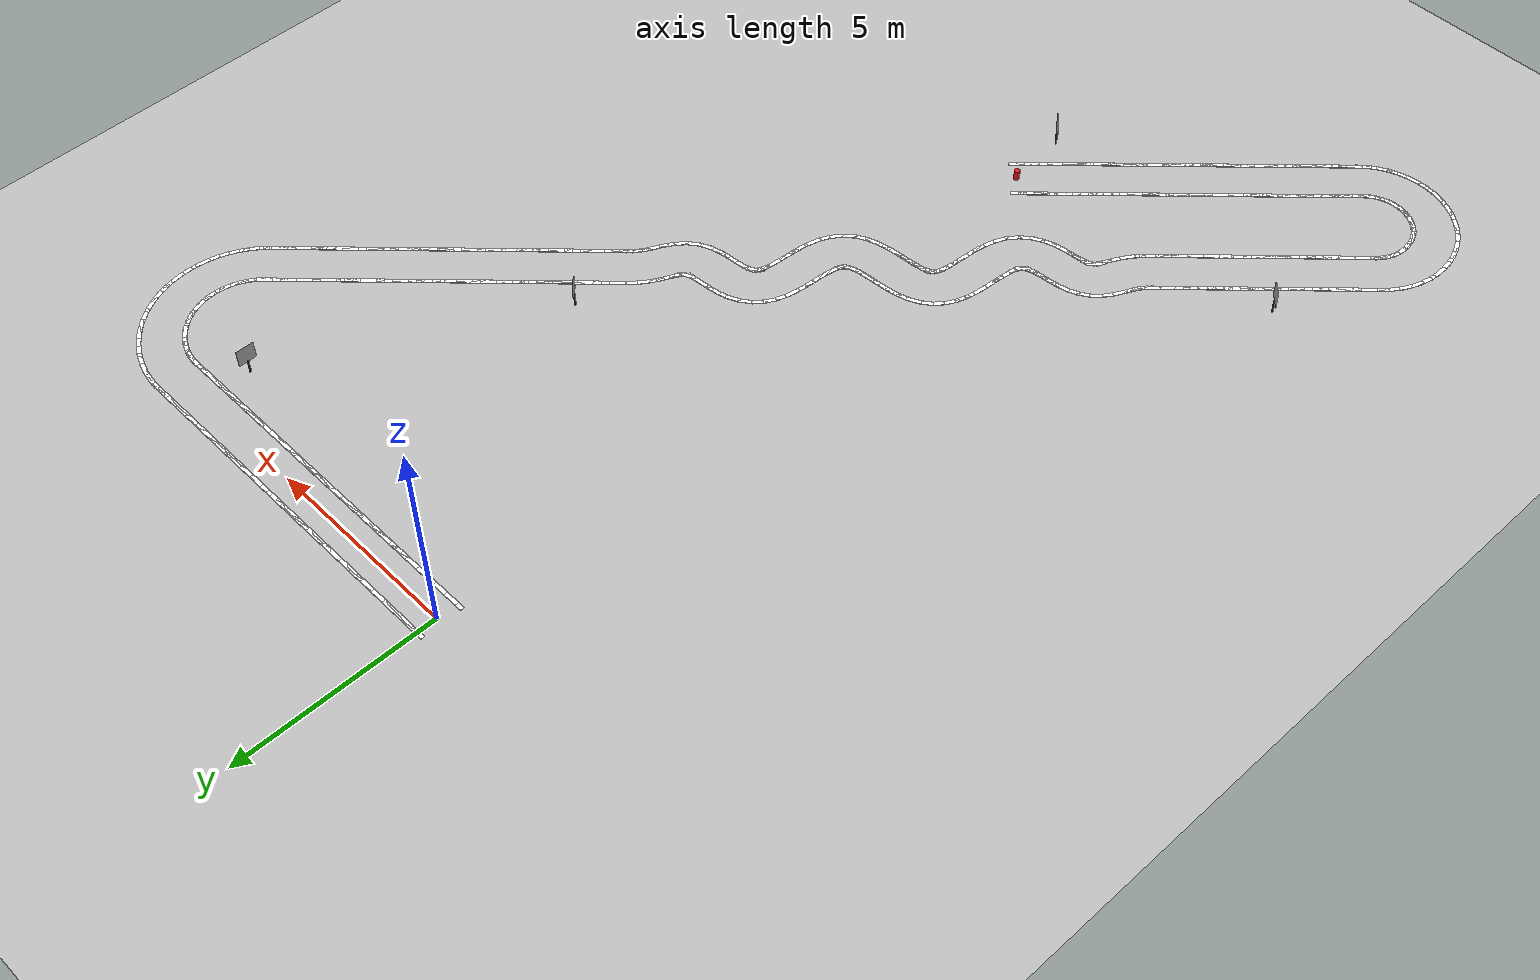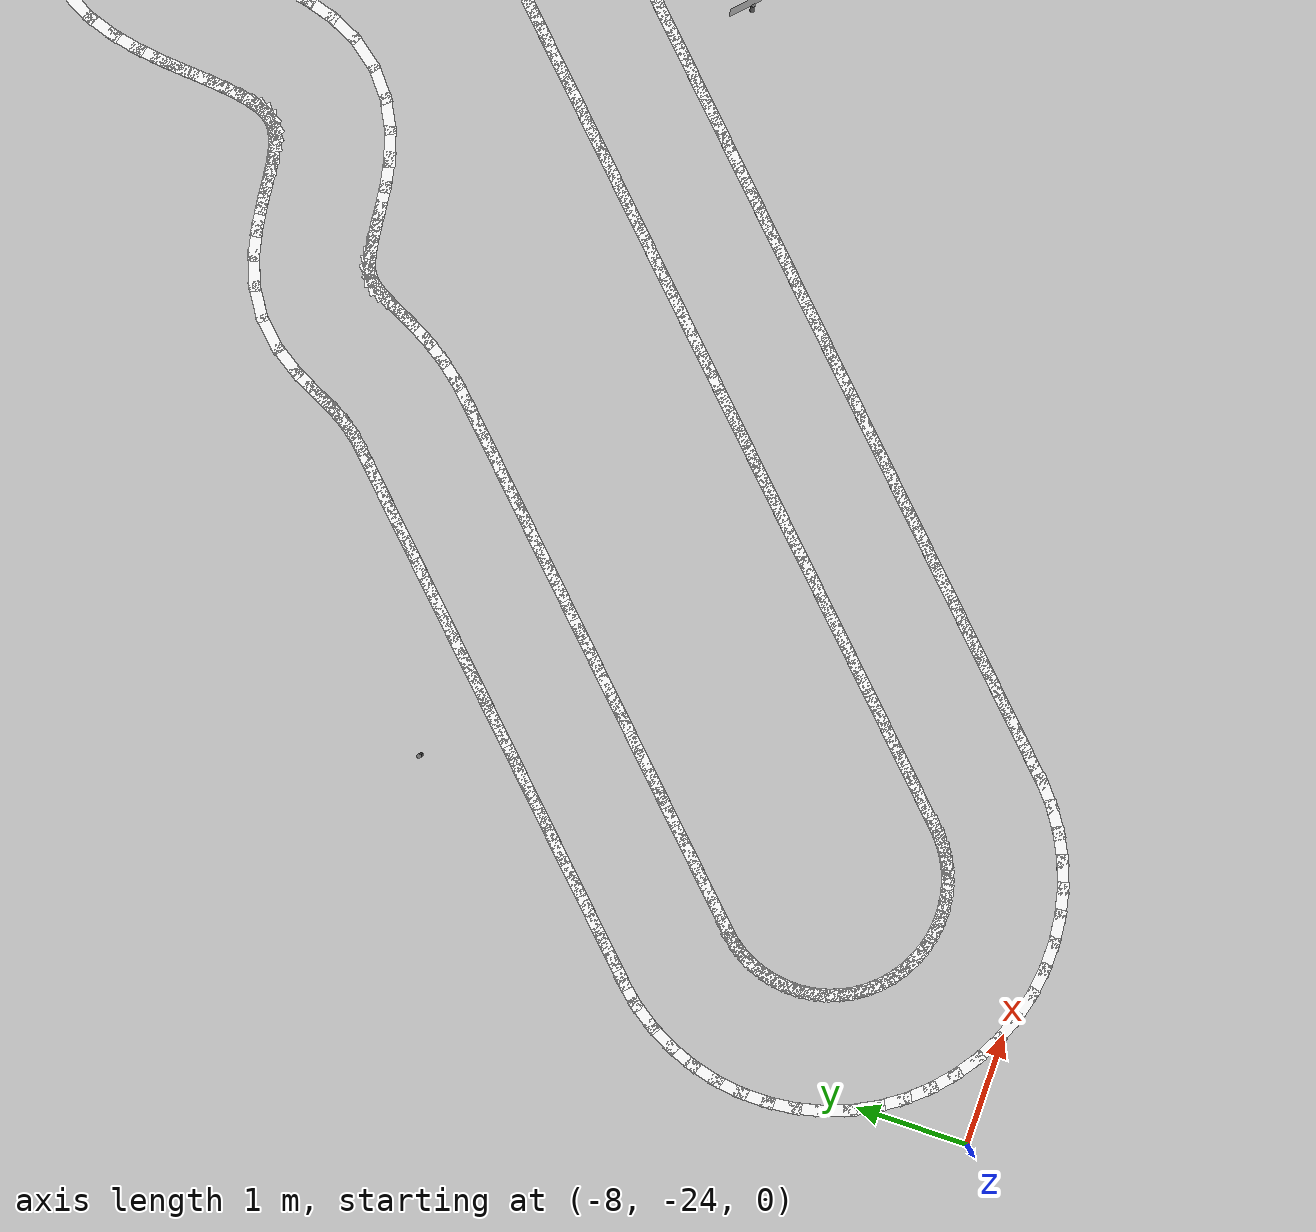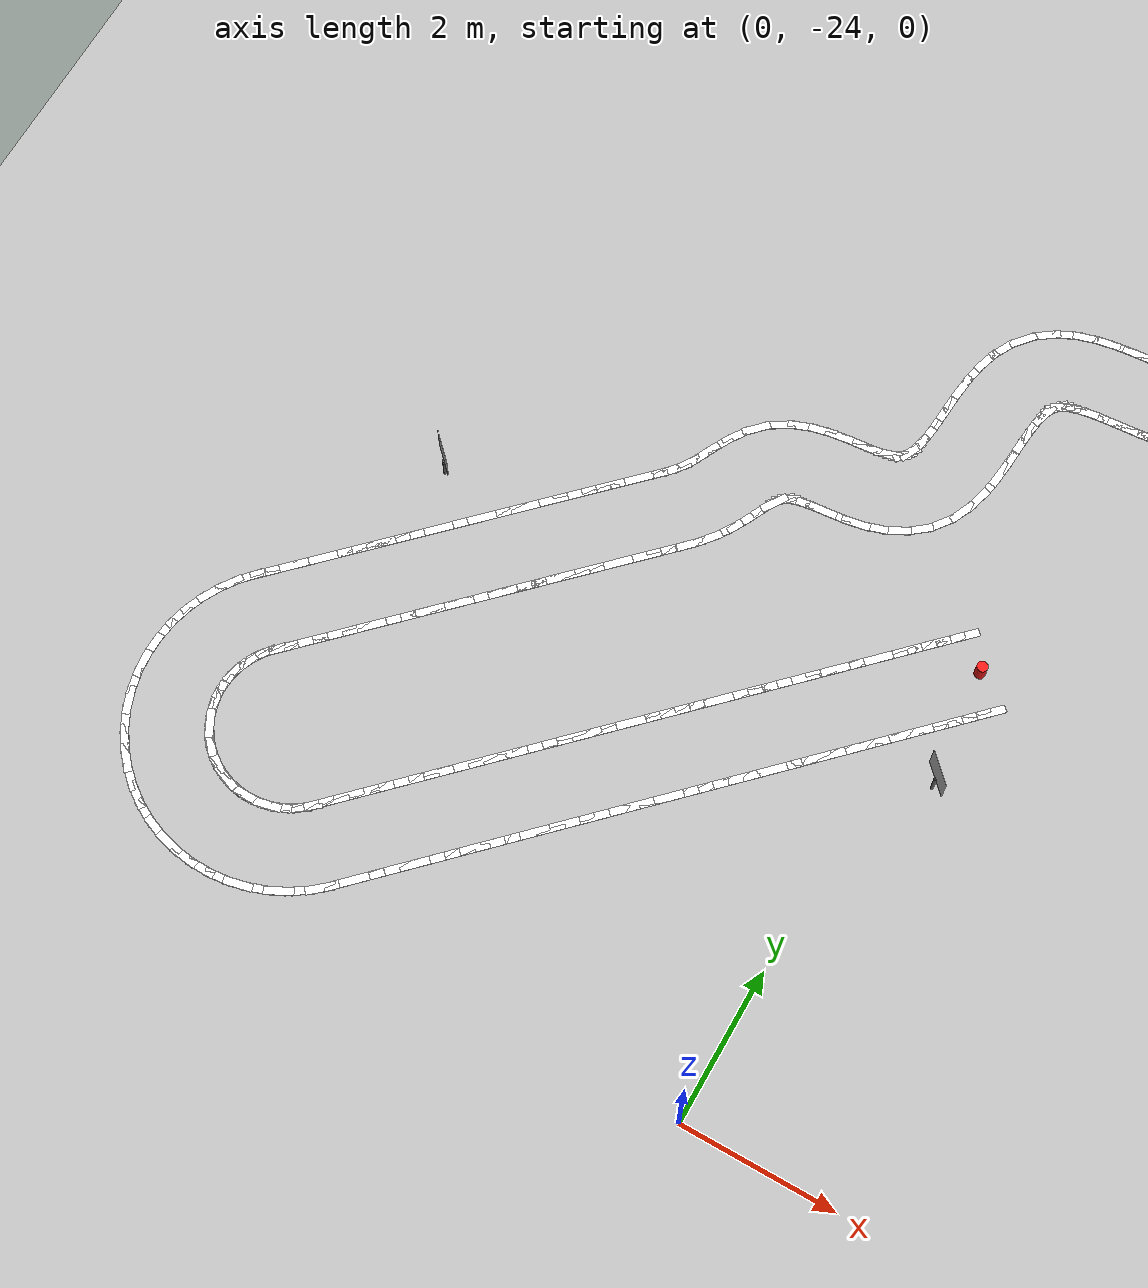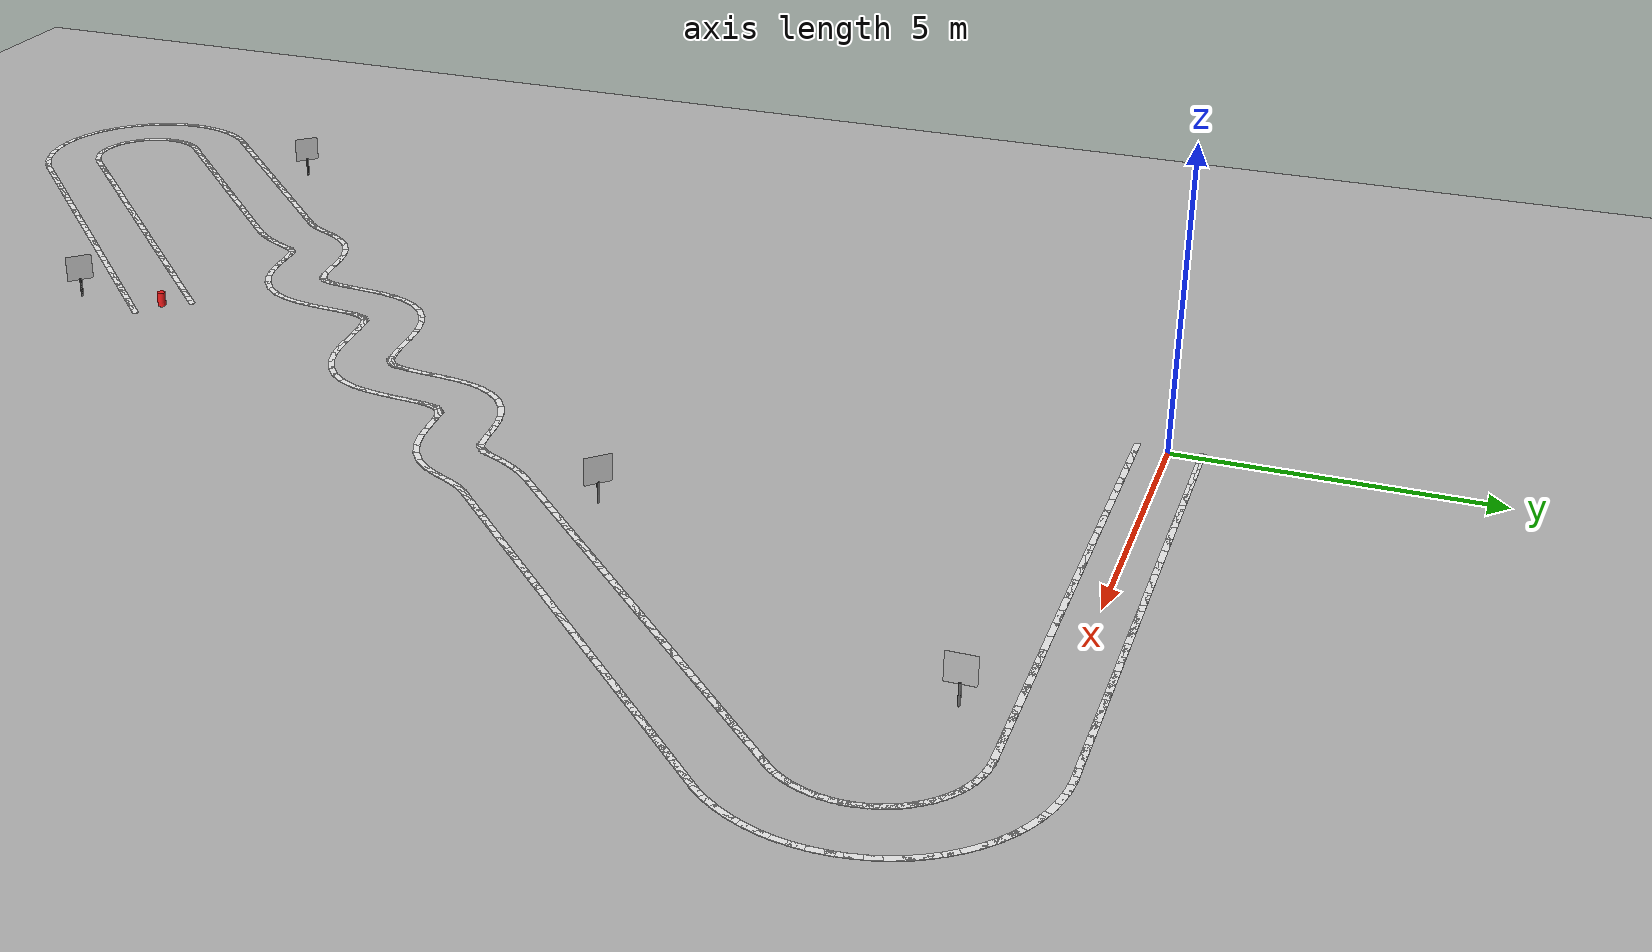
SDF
<?xml version="1.0"?>
<!-- AUTO-GENERATED by scripts/generate_track_lines.py - edit PARAMS there and re-run. -->
<sdf version="1.7">
  <world name="cone_lane">

    <physics type="ode">
      <max_step_size>0.004</max_step_size>
      <real_time_factor>1.0</real_time_factor>
    </physics>

    <plugin filename="libignition-gazebo-physics-system.so"
      name="ignition::gazebo::systems::Physics" />
    <plugin filename="libignition-gazebo-user-commands-system.so"
      name="ignition::gazebo::systems::UserCommands" />
    <plugin filename="libignition-gazebo-scene-broadcaster-system.so"
      name="ignition::gazebo::systems::SceneBroadcaster" />
    <plugin filename="libignition-gazebo-sensors-system.so"
      name="ignition::gazebo::systems::Sensors">
      <render_engine>ogre2</render_engine>
    </plugin>
    <plugin filename="libignition-gazebo-imu-system.so"
      name="ignition::gazebo::systems::Imu" />

    <scene>
      <ambient>0.4 0.4 0.4 1</ambient>
      <background>0.53 0.81 0.92 1</background>
      <shadows>true</shadows>
      <grid>false</grid>
      <sky></sky>
    </scene>

    <light type="directional" name="sun">
      <cast_shadows>true</cast_shadows>
      <pose>0 0 10 0 0 0</pose>
      <diffuse>0.9 0.9 0.9 1</diffuse>
      <specular>0.3 0.3 0.3 1</specular>
      <attenuation>
        <range>1000</range>
        <constant>0.9</constant>
        <linear>0.01</linear>
        <quadratic>0.001</quadratic>
      </attenuation>
      <direction>-0.5 0.1 -0.9</direction>
    </light>

    <model name="ground_plane">
      <static>true</static>
      <link name="link">
        <collision name="collision">
          <geometry><plane><normal>0 0 1</normal><size>150 150</size></plane></geometry>
          <surface><friction><ode><mu>1.0</mu></ode></friction></surface>
        </collision>
      </link>
    </model>

    <include>
      <name>ground_asphalt</name>
      <uri>model://ground_asphalt</uri>
      <pose>0 0 0 0 0 0</pose>
    </include>

    <!-- Left boundary line (light-gray segments) -->
    <model name="line_L001">
      <static>true</static>
      <pose>0.000 0.500 0.0030 0 0 0.0000</pose>
      <link name="link">
        <visual name="v">
          <geometry><box><size>0.360 0.100 0.005</size></box></geometry>
          <material>
            <ambient>0.85 0.85 0.85 1</ambient>
            <diffuse>0.95 0.95 0.95 1</diffuse>
            <specular>0.1 0.1 0.1 1</specular>
            <emissive>0.7 0.7 0.7 1</emissive>
          </material>
        </visual>
      </link>
    </model>
    <model name="line_L002">
      <static>true</static>
      <pose>0.180 0.500 0.0030 0 0 0.0000</pose>
      <link name="link">
        <visual name="v">
          <geometry><box><size>0.360 0.100 0.005</size></box></geometry>
          <material>
            <ambient>0.85 0.85 0.85 1</ambient>
            <diffuse>0.95 0.95 0.95 1</diffuse>
            <specular>0.1 0.1 0.1 1</specular>
            <emissive>0.7 0.7 0.7 1</emissive>
          </material>
        </visual>
      </link>
    </model>
    <model name="line_L003">
      <static>true</static>
      <pose>0.360 0.500 0.0030 0 0 0.0000</pose>
      <link name="link">
        <visual name="v">
          <geometry><box><size>0.360 0.100 0.005</size></box></geometry>
          <material>
            <ambient>0.85 0.85 0.85 1</ambient>
            <diffuse>0.95 0.95 0.95 1</diffuse>
            <specular>0.1 0.1 0.1 1</specular>
            <emissive>0.7 0.7 0.7 1</emissive>
          </material>
        </visual>
      </link>
    </model>
    <model name="line_L004">
      <static>true</static>
      <pose>0.540 0.500 0.0030 0 0 0.0000</pose>
      <link name="link">
        <visual name="v">
          <geometry><box><size>0.360 0.100 0.005</size></box></geometry>
          <material>
            <ambient>0.85 0.85 0.85 1</ambient>
            <diffuse>0.95 0.95 0.95 1</diffuse>
            <specular>0.1 0.1 0.1 1</specular>
            <emissive>0.7 0.7 0.7 1</emissive>
          </material>
        </visual>
      </link>
    </model>
    <model name="line_L005">
      <static>true</static>
      <pose>0.720 0.500 0.0030 0 0 0.0000</pose>
      <link name="link">
        <visual name="v">
          <geometry><box><size>0.360 0.100 0.005</size></box></geometry>
          <material>
            <ambient>0.85 0.85 0.85 1</ambient>
            <diffuse>0.95 0.95 0.95 1</diffuse>
            <specular>0.1 0.1 0.1 1</specular>
            <emissive>0.7 0.7 0.7 1</emissive>
          </material>
        </visual>
      </link>
    </model>
    <model name="line_L006">
      <static>true</static>
      <pose>0.900 0.500 0.0030 0 0 0.0000</pose>
      <link name="link">
        <visual name="v">
          <geometry><box><size>0.360 0.100 0.005</size></box></geometry>
          <material>
            <ambient>0.85 0.85 0.85 1</ambient>
            <diffuse>0.95 0.95 0.95 1</diffuse>
            <specular>0.1 0.1 0.1 1</specular>
            <emissive>0.7 0.7 0.7 1</emissive>
          </material>
        </visual>
      </link>
    </model>
    <model name="line_L007">
      <static>true</static>
      <pose>1.080 0.500 0.0030 0 0 0.0000</pose>
      <link name="link">
        <visual name="v">
          <geometry><box><size>0.360 0.100 0.005</size></box></geometry>
          <material>
            <ambient>0.85 0.85 0.85 1</ambient>
            <diffuse>0.95 0.95 0.95 1</diffuse>
            <specular>0.1 0.1 0.1 1</specular>
            <emissive>0.7 0.7 0.7 1</emissive>
          </material>
        </visual>
      </link>
    </model>
    <model name="line_L008">
      <static>true</static>
      <pose>1.260 0.500 0.0030 0 0 0.0000</pose>
      <link name="link">
        <visual name="v">
          <geometry><box><size>0.360 0.100 0.005</size></box></geometry>
          <material>
            <ambient>0.85 0.85 0.85 1</ambient>
            <diffuse>0.95 0.95 0.95 1</diffuse>
            <specular>0.1 0.1 0.1 1</specular>
            <emissive>0.7 0.7 0.7 1</emissive>
          </material>
        </visual>
      </link>
    </model>
    <model name="line_L009">
      <static>true</static>
      <pose>1.440 0.500 0.0030 0 0 0.0000</pose>
      <link name="link">
        <visual name="v">
          <geometry><box><size>0.360 0.100 0.005</size></box></geometry>
          <material>
            <ambient>0.85 0.85 0.85 1</ambient>
            <diffuse>0.95 0.95 0.95 1</diffuse>
            <specular>0.1 0.1 0.1 1</specular>
            <emissive>0.7 0.7 0.7 1</emissive>
          </material>
        </visual>
      </link>
    </model>
    <model name="line_L010">
      <static>true</static>
      <pose>1.620 0.500 0.0030 0 0 0.0000</pose>
      <link name="link">
        <visual name="v">
          <geometry><box><size>0.360 0.100 0.005</size></box></geometry>
          <material>
            <ambient>0.85 0.85 0.85 1</ambient>
            <diffuse>0.95 0.95 0.95 1</diffuse>
            <specular>0.1 0.1 0.1 1</specular>
            <emissive>0.7 0.7 0.7 1</emissive>
          </material>
        </visual>
      </link>
    </model>
    <model name="line_L011">
      <static>true</static>
      <pose>1.800 0.500 0.0030 0 0 0.0000</pose>
      <link name="link">
        <visual name="v">
          <geometry><box><size>0.360 0.100 0.005</size></box></geometry>
          <material>
            <ambient>0.85 0.85 0.85 1</ambient>
            <diffuse>0.95 0.95 0.95 1</diffuse>
            <specular>0.1 0.1 0.1 1</specular>
            <emissive>0.7 0.7 0.7 1</emissive>
          </material>
        </visual>
      </link>
    </model>
    <model name="line_L012">
      <static>true</static>
      <pose>1.980 0.500 0.0030 0 0 0.0000</pose>
      <link name="link">
        <visual name="v">
          <geometry><box><size>0.360 0.100 0.005</size></box></geometry>
          <material>
            <ambient>0.85 0.85 0.85 1</ambient>
            <diffuse>0.95 0.95 0.95 1</diffuse>
            <specular>0.1 0.1 0.1 1</specular>
            <emissive>0.7 0.7 0.7 1</emissive>
          </material>
        </visual>
      </link>
    </model>
    <model name="line_L013">
      <static>true</static>
      <pose>2.160 0.500 0.0030 0 0 0.0000</pose>
      <link name="link">
        <visual name="v">
          <geometry><box><size>0.360 0.100 0.005</size></box></geometry>
          <material>
            <ambient>0.85 0.85 0.85 1</ambient>
            <diffuse>0.95 0.95 0.95 1</diffuse>
            <specular>0.1 0.1 0.1 1</specular>
            <emissive>0.7 0.7 0.7 1</emissive>
          </material>
        </visual>
      </link>
    </model>
    <model name="line_L014">
      <static>true</static>
      <pose>2.340 0.500 0.0030 0 0 0.0000</pose>
      <link name="link">
        <visual name="v">
          <geometry><box><size>0.360 0.100 0.005</size></box></geometry>
          <material>
            <ambient>0.85 0.85 0.85 1</ambient>
            <diffuse>0.95 0.95 0.95 1</diffuse>
            <specular>0.1 0.1 0.1 1</specular>
            <emissive>0.7 0.7 0.7 1</emissive>
          </material>
        </visual>
      </link>
    </model>
    <model name="line_L015">
      <static>true</static>
      <pose>2.520 0.500 0.0030 0 0 0.0000</pose>
      <link name="link">
        <visual name="v">
          <geometry><box><size>0.360 0.100 0.005</size></box></geometry>
          <material>
            <ambient>0.85 0.85 0.85 1</ambient>
            <diffuse>0.95 0.95 0.95 1</diffuse>
            <specular>0.1 0.1 0.1 1</specular>
            <emissive>0.7 0.7 0.7 1</emissive>
          </material>
        </visual>
      </link>
    </model>
    <model name="line_L016">
      <static>true</static>
      <pose>2.700 0.500 0.0030 0 0 0.0000</pose>
      <link name="link">
        <visual name="v">
          <geometry><box><size>0.360 0.100 0.005</size></box></geometry>
          <material>
            <ambient>0.85 0.85 0.85 1</ambient>
            <diffuse>0.95 0.95 0.95 1</diffuse>
            <specular>0.1 0.1 0.1 1</specular>
            <emissive>0.7 0.7 0.7 1</emissive>
          </material>
        </visual>
      </link>
    </model>
    <model name="line_L017">
      <static>true</static>
      <pose>2.900 0.500 0.0030 0 0 0.0000</pose>
      <link name="link">
        <visual name="v">
          <geometry><box><size>0.360 0.100 0.005</size></box></geometry>
          <material>
            <ambient>0.85 0.85 0.85 1</ambient>
            <diffuse>0.95 0.95 0.95 1</diffuse>
            <specular>0.1 0.1 0.1 1</specular>
            <emissive>0.7 0.7 0.7 1</emissive>
          </material>
        </visual>
      </link>
    </model>
    <model name="line_L018">
      <static>true</static>
      <pose>3.080 0.500 0.0030 0 0 0.0000</pose>
      <link name="link">
        <visual name="v">
          <geometry><box><size>0.360 0.100 0.005</size></box></geometry>
          <material>
            <ambient>0.85 0.85 0.85 1</ambient>
            <diffuse>0.95 0.95 0.95 1</diffuse>
            <specular>0.1 0.1 0.1 1</specular>
            <emissive>0.7 0.7 0.7 1</emissive>
          </material>
        </visual>
      </link>
    </model>
    <model name="line_L019">
      <static>true</static>
      <pose>3.260 0.500 0.0030 0 0 0.0000</pose>
      <link name="link">
        <visual name="v">
          <geometry><box><size>0.360 0.100 0.005</size></box></geometry>
          <material>
            <ambient>0.85 0.85 0.85 1</ambient>
            <diffuse>0.95 0.95 0.95 1</diffuse>
            <specular>0.1 0.1 0.1 1</specular>
            <emissive>0.7 0.7 0.7 1</emissive>
          </material>
        </visual>
      </link>
    </model>
    <model name="line_L020">
      <static>true</static>
      <pose>3.440 0.500 0.0030 0 0 0.0000</pose>
      <link name="link">
        <visual name="v">
          <geometry><box><size>0.360 0.100 0.005</size></box></geometry>
          <material>
            <ambient>0.85 0.85 0.85 1</ambient>
            <diffuse>0.95 0.95 0.95 1</diffuse>
            <specular>0.1 0.1 0.1 1</specular>
            <emissive>0.7 0.7 0.7 1</emissive>
          </material>
        </visual>
      </link>
    </model>
    <model name="line_L021">
      <static>true</static>
      <pose>3.620 0.500 0.0030 0 0 0.0000</pose>
      <link name="link">
        <visual name="v">
          <geometry><box><size>0.360 0.100 0.005</size></box></geometry>
          <material>
            <ambient>0.85 0.85 0.85 1</ambient>
            <diffuse>0.95 0.95 0.95 1</diffuse>
            <specular>0.1 0.1 0.1 1</specular>
            <emissive>0.7 0.7 0.7 1</emissive>
          </material>
        </visual>
      </link>
    </model>
    <model name="line_L022">
      <static>true</static>
      <pose>3.800 0.500 0.0030 0 0 0.0000</pose>
      <link name="link">
        <visual name="v">
          <geometry><box><size>0.360 0.100 0.005</size></box></geometry>
          <material>
            <ambient>0.85 0.85 0.85 1</ambient>
            <diffuse>0.95 0.95 0.95 1</diffuse>
            <specular>0.1 0.1 0.1 1</specular>
            <emissive>0.7 0.7 0.7 1</emissive>
          </material>
        </visual>
      </link>
    </model>
    <model name="line_L023">
      <static>true</static>
      <pose>3.980 0.500 0.0030 0 0 0.0000</pose>
      <link name="link">
        <visual name="v">
          <geometry><box><size>0.360 0.100 0.005</size></box></geometry>
          <material>
            <ambient>0.85 0.85 0.85 1</ambient>
            <diffuse>0.95 0.95 0.95 1</diffuse>
            <specular>0.1 0.1 0.1 1</specular>
            <emissive>0.7 0.7 0.7 1</emissive>
          </material>
        </visual>
      </link>
    </model>
    <model name="line_L024">
      <static>true</static>
      <pose>4.160 0.500 0.0030 0 0 0.0000</pose>
      <link name="link">
        <visual name="v">
          <geometry><box><size>0.360 0.100 0.005</size></box></geometry>
          <material>
            <ambient>0.85 0.85 0.85 1</ambient>
            <diffuse>0.95 0.95 0.95 1</diffuse>
            <specular>0.1 0.1 0.1 1</specular>
            <emissive>0.7 0.7 0.7 1</emissive>
          </material>
        </visual>
      </link>
    </model>
    <model name="line_L025">
      <static>true</static>
      <pose>4.340 0.500 0.0030 0 0 0.0000</pose>
      <link name="link">
        <visual name="v">
          <geometry><box><size>0.360 0.100 0.005</size></box></geometry>
          <material>
            <ambient>0.85 0.85 0.85 1</ambient>
            <diffuse>0.95 0.95 0.95 1</diffuse>
            <specular>0.1 0.1 0.1 1</specular>
            <emissive>0.7 0.7 0.7 1</emissive>
          </material>
        </visual>
      </link>
    </model>
    <model name="line_L026">
      <static>true</static>
      <pose>4.520 0.500 0.0030 0 0 0.0000</pose>
      <link name="link">
        <visual name="v">
          <geometry><box><size>0.360 0.100 0.005</size></box></geometry>
          <material>
            <ambient>0.85 0.85 0.85 1</ambient>
            <diffuse>0.95 0.95 0.95 1</diffuse>
            <specular>0.1 0.1 0.1 1</specular>
            <emissive>0.7 0.7 0.7 1</emissive>
          </material>
        </visual>
      </link>
    </model>
    <model name="line_L027">
      <static>true</static>
      <pose>4.700 0.500 0.0030 0 0 0.0000</pose>
      <link name="link">
        <visual name="v">
          <geometry><box><size>0.360 0.100 0.005</size></box></geometry>
          <material>
            <ambient>0.85 0.85 0.85 1</ambient>
            <diffuse>0.95 0.95 0.95 1</diffuse>
            <specular>0.1 0.1 0.1 1</specular>
            <emissive>0.7 0.7 0.7 1</emissive>
          </material>
        </visual>
      </link>
    </model>
    <model name="line_L028">
      <static>true</static>
      <pose>4.860 0.500 0.0030 0 0 0.0000</pose>
      <link name="link">
        <visual name="v">
          <geometry><box><size>0.360 0.100 0.005</size></box></geometry>
          <material>
            <ambient>0.85 0.85 0.85 1</ambient>
            <diffuse>0.95 0.95 0.95 1</diffuse>
            <specular>0.1 0.1 0.1 1</specular>
            <emissive>0.7 0.7 0.7 1</emissive>
          </material>
        </visual>
      </link>
    </model>
    <model name="line_L029">
      <static>true</static>
      <pose>5.040 0.500 0.0030 0 0 0.0000</pose>
      <link name="link">
        <visual name="v">
          <geometry><box><size>0.360 0.100 0.005</size></box></geometry>
          <material>
            <ambient>0.85 0.85 0.85 1</ambient>
            <diffuse>0.95 0.95 0.95 1</diffuse>
            <specular>0.1 0.1 0.1 1</specular>
            <emissive>0.7 0.7 0.7 1</emissive>
          </material>
        </visual>
      </link>
    </model>
    <model name="line_L030">
      <static>true</static>
      <pose>5.220 0.500 0.0030 0 0 0.0000</pose>
      <link name="link">
        <visual name="v">
          <geometry><box><size>0.360 0.100 0.005</size></box></geometry>
          <material>
            <ambient>0.85 0.85 0.85 1</ambient>
            <diffuse>0.95 0.95 0.95 1</diffuse>
            <specular>0.1 0.1 0.1 1</specular>
            <emissive>0.7 0.7 0.7 1</emissive>
          </material>
        </visual>
      </link>
    </model>
    <model name="line_L031">
      <static>true</static>
      <pose>5.400 0.500 0.0030 0 0 0.0000</pose>
      <link name="link">
        <visual name="v">
          <geometry><box><size>0.360 0.100 0.005</size></box></geometry>
          <material>
            <ambient>0.85 0.85 0.85 1</ambient>
            <diffuse>0.95 0.95 0.95 1</diffuse>
            <specular>0.1 0.1 0.1 1</specular>
            <emissive>0.7 0.7 0.7 1</emissive>
          </material>
        </visual>
      </link>
    </model>
    <model name="line_L032">
      <static>true</static>
      <pose>5.580 0.500 0.0030 0 0 0.0000</pose>
      <link name="link">
        <visual name="v">
          <geometry><box><size>0.360 0.100 0.005</size></box></geometry>
          <material>
            <ambient>0.85 0.85 0.85 1</ambient>
            <diffuse>0.95 0.95 0.95 1</diffuse>
            <specular>0.1 0.1 0.1 1</specular>
            <emissive>0.7 0.7 0.7 1</emissive>
          </material>
        </visual>
      </link>
    </model>
    <model name="line_L033">
      <static>true</static>
      <pose>5.760 0.500 0.0030 0 0 0.0000</pose>
      <link name="link">
        <visual name="v">
          <geometry><box><size>0.360 0.100 0.005</size></box></geometry>
          <material>
            <ambient>0.85 0.85 0.85 1</ambient>
            <diffuse>0.95 0.95 0.95 1</diffuse>
            <specular>0.1 0.1 0.1 1</specular>
            <emissive>0.7 0.7 0.7 1</emissive>
          </material>
        </visual>
      </link>
    </model>
    <model name="line_L034">
      <static>true</static>
      <pose>5.940 0.500 0.0030 0 0 0.0000</pose>
      <link name="link">
        <visual name="v">
          <geometry><box><size>0.360 0.100 0.005</size></box></geometry>
          <material>
            <ambient>0.85 0.85 0.85 1</ambient>
            <diffuse>0.95 0.95 0.95 1</diffuse>
            <specular>0.1 0.1 0.1 1</specular>
            <emissive>0.7 0.7 0.7 1</emissive>
          </material>
        </visual>
      </link>
    </model>
    <model name="line_L035">
      <static>true</static>
      <pose>6.120 0.500 0.0030 0 0 0.0000</pose>
      <link name="link">
        <visual name="v">
          <geometry><box><size>0.360 0.100 0.005</size></box></geometry>
          <material>
            <ambient>0.85 0.85 0.85 1</ambient>
            <diffuse>0.95 0.95 0.95 1</diffuse>
            <specular>0.1 0.1 0.1 1</specular>
            <emissive>0.7 0.7 0.7 1</emissive>
          </material>
        </visual>
      </link>
    </model>
    <model name="line_L036">
      <static>true</static>
      <pose>6.300 0.500 0.0030 0 0 0.0000</pose>
      <link name="link">
        <visual name="v">
          <geometry><box><size>0.360 0.100 0.005</size></box></geometry>
          <material>
            <ambient>0.85 0.85 0.85 1</ambient>
            <diffuse>0.95 0.95 0.95 1</diffuse>
            <specular>0.1 0.1 0.1 1</specular>
            <emissive>0.7 0.7 0.7 1</emissive>
          </material>
        </visual>
      </link>
    </model>
    <model name="line_L037">
      <static>true</static>
      <pose>6.480 0.500 0.0030 0 0 0.0000</pose>
      <link name="link">
        <visual name="v">
          <geometry><box><size>0.360 0.100 0.005</size></box></geometry>
          <material>
            <ambient>0.85 0.85 0.85 1</ambient>
            <diffuse>0.95 0.95 0.95 1</diffuse>
            <specular>0.1 0.1 0.1 1</specular>
            <emissive>0.7 0.7 0.7 1</emissive>
          </material>
        </visual>
      </link>
    </model>
    <model name="line_L038">
      <static>true</static>
      <pose>6.660 0.500 0.0030 0 0 0.0000</pose>
      <link name="link">
        <visual name="v">
          <geometry><box><size>0.360 0.100 0.005</size></box></geometry>
          <material>
            <ambient>0.85 0.85 0.85 1</ambient>
            <diffuse>0.95 0.95 0.95 1</diffuse>
            <specular>0.1 0.1 0.1 1</specular>
            <emissive>0.7 0.7 0.7 1</emissive>
          </material>
        </visual>
      </link>
    </model>
    <model name="line_L039">
      <static>true</static>
      <pose>6.840 0.500 0.0030 0 0 0.0000</pose>
      <link name="link">
        <visual name="v">
          <geometry><box><size>0.360 0.100 0.005</size></box></geometry>
          <material>
            <ambient>0.85 0.85 0.85 1</ambient>
            <diffuse>0.95 0.95 0.95 1</diffuse>
            <specular>0.1 0.1 0.1 1</specular>
            <emissive>0.7 0.7 0.7 1</emissive>
          </material>
        </visual>
      </link>
    </model>
    <model name="line_L040">
      <static>true</static>
      <pose>7.020 0.500 0.0030 0 0 0.0000</pose>
      <link name="link">
        <visual name="v">
          <geometry><box><size>0.360 0.100 0.005</size></box></geometry>
          <material>
            <ambient>0.85 0.85 0.85 1</ambient>
            <diffuse>0.95 0.95 0.95 1</diffuse>
            <specular>0.1 0.1 0.1 1</specular>
            <emissive>0.7 0.7 0.7 1</emissive>
          </material>
        </visual>
      </link>
    </model>
    <model name="line_L041">
      <static>true</static>
      <pose>7.200 0.500 0.0030 0 0 0.0000</pose>
      <link name="link">
        <visual name="v">
          <geometry><box><size>0.360 0.100 0.005</size></box></geometry>
          <material>
            <ambient>0.85 0.85 0.85 1</ambient>
            <diffuse>0.95 0.95 0.95 1</diffuse>
            <specular>0.1 0.1 0.1 1</specular>
            <emissive>0.7 0.7 0.7 1</emissive>
          </material>
        </visual>
      </link>
    </model>
    <model name="line_L042">
      <static>true</static>
      <pose>7.380 0.500 0.0030 0 0 0.0000</pose>
      <link name="link">
        <visual name="v">
          <geometry><box><size>0.360 0.100 0.005</size></box></geometry>
          <material>
            <ambient>0.85 0.85 0.85 1</ambient>
            <diffuse>0.95 0.95 0.95 1</diffuse>
            <specular>0.1 0.1 0.1 1</specular>
            <emissive>0.7 0.7 0.7 1</emissive>
          </material>
        </visual>
      </link>
    </model>
    <model name="line_L043">
      <static>true</static>
      <pose>7.560 0.500 0.0030 0 0 0.0000</pose>
      <link name="link">
        <visual name="v">
          <geometry><box><size>0.360 0.100 0.005</size></box></geometry>
          <material>
            <ambient>0.85 0.85 0.85 1</ambient>
            <diffuse>0.95 0.95 0.95 1</diffuse>
            <specular>0.1 0.1 0.1 1</specular>
            <emissive>0.7 0.7 0.7 1</emissive>
          </material>
        </visual>
      </link>
    </model>
    <model name="line_L044">
      <static>true</static>
      <pose>7.740 0.500 0.0030 0 0 0.0000</pose>
      <link name="link">
        <visual name="v">
          <geometry><box><size>0.360 0.100 0.005</size></box></geometry>
          <material>
            <ambient>0.85 0.85 0.85 1</ambient>
            <diffuse>0.95 0.95 0.95 1</diffuse>
            <specular>0.1 0.1 0.1 1</specular>
            <emissive>0.7 0.7 0.7 1</emissive>
          </material>
        </visual>
      </link>
    </model>
    <model name="line_L045">
      <static>true</static>
      <pose>7.920 0.500 0.0030 0 0 0.0000</pose>
      <link name="link">
        <visual name="v">
          <geometry><box><size>0.360 0.100 0.005</size></box></geometry>
          <material>
            <ambient>0.85 0.85 0.85 1</ambient>
            <diffuse>0.95 0.95 0.95 1</diffuse>
            <specular>0.1 0.1 0.1 1</specular>
            <emissive>0.7 0.7 0.7 1</emissive>
          </material>
        </visual>
      </link>
    </model>
    <model name="line_L046">
      <static>true</static>
      <pose>8.100 0.500 0.0030 0 0 0.0000</pose>
      <link name="link">
        <visual name="v">
          <geometry><box><size>0.360 0.100 0.005</size></box></geometry>
          <material>
            <ambient>0.85 0.85 0.85 1</ambient>
            <diffuse>0.95 0.95 0.95 1</diffuse>
            <specular>0.1 0.1 0.1 1</specular>
            <emissive>0.7 0.7 0.7 1</emissive>
          </material>
        </visual>
      </link>
    </model>
    <model name="line_L047">
      <static>true</static>
      <pose>8.280 0.500 0.0030 0 0 0.0000</pose>
      <link name="link">
        <visual name="v">
          <geometry><box><size>0.360 0.100 0.005</size></box></geometry>
          <material>
            <ambient>0.85 0.85 0.85 1</ambient>
            <diffuse>0.95 0.95 0.95 1</diffuse>
            <specular>0.1 0.1 0.1 1</specular>
            <emissive>0.7 0.7 0.7 1</emissive>
          </material>
        </visual>
      </link>
    </model>
    <model name="line_L048">
      <static>true</static>
      <pose>8.460 0.500 0.0030 0 0 0.0000</pose>
      <link name="link">
        <visual name="v">
          <geometry><box><size>0.360 0.100 0.005</size></box></geometry>
          <material>
            <ambient>0.85 0.85 0.85 1</ambient>
            <diffuse>0.95 0.95 0.95 1</diffuse>
            <specular>0.1 0.1 0.1 1</specular>
            <emissive>0.7 0.7 0.7 1</emissive>
          </material>
        </visual>
      </link>
    </model>
    <model name="line_L049">
      <static>true</static>
      <pose>8.640 0.500 0.0030 0 0 0.0000</pose>
      <link name="link">
        <visual name="v">
          <geometry><box><size>0.360 0.100 0.005</size></box></geometry>
          <material>
            <ambient>0.85 0.85 0.85 1</ambient>
            <diffuse>0.95 0.95 0.95 1</diffuse>
            <specular>0.1 0.1 0.1 1</specular>
            <emissive>0.7 0.7 0.7 1</emissive>
          </material>
        </visual>
      </link>
    </model>
    <model name="line_L050">
      <static>true</static>
      <pose>8.820 0.500 0.0030 0 0 0.0000</pose>
      <link name="link">
        <visual name="v">
          <geometry><box><size>0.360 0.100 0.005</size></box></geometry>
          <material>
            <ambient>0.85 0.85 0.85 1</ambient>
            <diffuse>0.95 0.95 0.95 1</diffuse>
            <specular>0.1 0.1 0.1 1</specular>
            <emissive>0.7 0.7 0.7 1</emissive>
          </material>
        </visual>
      </link>
    </model>
    <model name="line_L051">
      <static>true</static>
      <pose>9.001 0.500 0.0030 0 0 -0.0025</pose>
      <link name="link">
        <visual name="v">
          <geometry><box><size>0.360 0.100 0.005</size></box></geometry>
          <material>
            <ambient>0.85 0.85 0.85 1</ambient>
            <diffuse>0.95 0.95 0.95 1</diffuse>
            <specular>0.1 0.1 0.1 1</specular>
            <emissive>0.7 0.7 0.7 1</emissive>
          </material>
        </visual>
      </link>
    </model>
    <model name="line_L052">
      <static>true</static>
      <pose>9.225 0.490 0.0030 0 0 -0.0902</pose>
      <link name="link">
        <visual name="v">
          <geometry><box><size>0.360 0.100 0.005</size></box></geometry>
          <material>
            <ambient>0.85 0.85 0.85 1</ambient>
            <diffuse>0.95 0.95 0.95 1</diffuse>
            <specular>0.1 0.1 0.1 1</specular>
            <emissive>0.7 0.7 0.7 1</emissive>
          </material>
        </visual>
      </link>
    </model>
    <model name="line_L053">
      <static>true</static>
      <pose>9.449 0.459 0.0030 0 0 -0.1805</pose>
      <link name="link">
        <visual name="v">
          <geometry><box><size>0.360 0.100 0.005</size></box></geometry>
          <material>
            <ambient>0.85 0.85 0.85 1</ambient>
            <diffuse>0.95 0.95 0.95 1</diffuse>
            <specular>0.1 0.1 0.1 1</specular>
            <emissive>0.7 0.7 0.7 1</emissive>
          </material>
        </visual>
      </link>
    </model>
    <model name="line_L054">
      <static>true</static>
      <pose>9.669 0.409 0.0030 0 0 -0.2707</pose>
      <link name="link">
        <visual name="v">
          <geometry><box><size>0.360 0.100 0.005</size></box></geometry>
          <material>
            <ambient>0.85 0.85 0.85 1</ambient>
            <diffuse>0.95 0.95 0.95 1</diffuse>
            <specular>0.1 0.1 0.1 1</specular>
            <emissive>0.7 0.7 0.7 1</emissive>
          </material>
        </visual>
      </link>
    </model>
    <model name="line_L055">
      <static>true</static>
      <pose>9.883 0.339 0.0030 0 0 -0.3609</pose>
      <link name="link">
        <visual name="v">
          <geometry><box><size>0.360 0.100 0.005</size></box></geometry>
          <material>
            <ambient>0.85 0.85 0.85 1</ambient>
            <diffuse>0.95 0.95 0.95 1</diffuse>
            <specular>0.1 0.1 0.1 1</specular>
            <emissive>0.7 0.7 0.7 1</emissive>
          </material>
        </visual>
      </link>
    </model>
    <model name="line_L056">
      <static>true</static>
      <pose>10.090 0.250 0.0030 0 0 -0.4512</pose>
      <link name="link">
        <visual name="v">
          <geometry><box><size>0.360 0.100 0.005</size></box></geometry>
          <material>
            <ambient>0.85 0.85 0.85 1</ambient>
            <diffuse>0.95 0.95 0.95 1</diffuse>
            <specular>0.1 0.1 0.1 1</specular>
            <emissive>0.7 0.7 0.7 1</emissive>
          </material>
        </visual>
      </link>
    </model>
    <model name="line_L057">
      <static>true</static>
      <pose>10.288 0.142 0.0030 0 0 -0.5414</pose>
      <link name="link">
        <visual name="v">
          <geometry><box><size>0.360 0.100 0.005</size></box></geometry>
          <material>
            <ambient>0.85 0.85 0.85 1</ambient>
            <diffuse>0.95 0.95 0.95 1</diffuse>
            <specular>0.1 0.1 0.1 1</specular>
            <emissive>0.7 0.7 0.7 1</emissive>
          </material>
        </visual>
      </link>
    </model>
    <model name="line_L058">
      <static>true</static>
      <pose>10.476 0.018 0.0030 0 0 -0.6317</pose>
      <link name="link">
        <visual name="v">
          <geometry><box><size>0.360 0.100 0.005</size></box></geometry>
          <material>
            <ambient>0.85 0.85 0.85 1</ambient>
            <diffuse>0.95 0.95 0.95 1</diffuse>
            <specular>0.1 0.1 0.1 1</specular>
            <emissive>0.7 0.7 0.7 1</emissive>
          </material>
        </visual>
      </link>
    </model>
    <model name="line_L059">
      <static>true</static>
      <pose>10.652 -0.124 0.0030 0 0 -0.7219</pose>
      <link name="link">
        <visual name="v">
          <geometry><box><size>0.360 0.100 0.005</size></box></geometry>
          <material>
            <ambient>0.85 0.85 0.85 1</ambient>
            <diffuse>0.95 0.95 0.95 1</diffuse>
            <specular>0.1 0.1 0.1 1</specular>
            <emissive>0.7 0.7 0.7 1</emissive>
          </material>
        </visual>
      </link>
    </model>
    <model name="line_L060">
      <static>true</static>
      <pose>10.814 -0.280 0.0030 0 0 -0.8121</pose>
      <link name="link">
        <visual name="v">
          <geometry><box><size>0.360 0.100 0.005</size></box></geometry>
          <material>
            <ambient>0.85 0.85 0.85 1</ambient>
            <diffuse>0.95 0.95 0.95 1</diffuse>
            <specular>0.1 0.1 0.1 1</specular>
            <emissive>0.7 0.7 0.7 1</emissive>
          </material>
        </visual>
      </link>
    </model>
    <model name="line_L061">
      <static>true</static>
      <pose>10.962 -0.451 0.0030 0 0 -0.9024</pose>
      <link name="link">
        <visual name="v">
          <geometry><box><size>0.360 0.100 0.005</size></box></geometry>
          <material>
            <ambient>0.85 0.85 0.85 1</ambient>
            <diffuse>0.95 0.95 0.95 1</diffuse>
            <specular>0.1 0.1 0.1 1</specular>
            <emissive>0.7 0.7 0.7 1</emissive>
          </material>
        </visual>
      </link>
    </model>
    <model name="line_L062">
      <static>true</static>
      <pose>11.094 -0.634 0.0030 0 0 -0.9926</pose>
      <link name="link">
        <visual name="v">
          <geometry><box><size>0.360 0.100 0.005</size></box></geometry>
          <material>
            <ambient>0.85 0.85 0.85 1</ambient>
            <diffuse>0.95 0.95 0.95 1</diffuse>
            <specular>0.1 0.1 0.1 1</specular>
            <emissive>0.7 0.7 0.7 1</emissive>
          </material>
        </visual>
      </link>
    </model>
    <model name="line_L063">
      <static>true</static>
      <pose>11.208 -0.828 0.0030 0 0 -1.0828</pose>
      <link name="link">
        <visual name="v">
          <geometry><box><size>0.360 0.100 0.005</size></box></geometry>
          <material>
            <ambient>0.85 0.85 0.85 1</ambient>
            <diffuse>0.95 0.95 0.95 1</diffuse>
            <specular>0.1 0.1 0.1 1</specular>
            <emissive>0.7 0.7 0.7 1</emissive>
          </material>
        </visual>
      </link>
    </model>
    <model name="line_L064">
      <static>true</static>
      <pose>11.305 -1.032 0.0030 0 0 -1.1731</pose>
      <link name="link">
        <visual name="v">
          <geometry><box><size>0.360 0.100 0.005</size></box></geometry>
          <material>
            <ambient>0.85 0.85 0.85 1</ambient>
            <diffuse>0.95 0.95 0.95 1</diffuse>
            <specular>0.1 0.1 0.1 1</specular>
            <emissive>0.7 0.7 0.7 1</emissive>
          </material>
        </visual>
      </link>
    </model>
    <model name="line_L065">
      <static>true</static>
      <pose>11.383 -1.243 0.0030 0 0 -1.2633</pose>
      <link name="link">
        <visual name="v">
          <geometry><box><size>0.360 0.100 0.005</size></box></geometry>
          <material>
            <ambient>0.85 0.85 0.85 1</ambient>
            <diffuse>0.95 0.95 0.95 1</diffuse>
            <specular>0.1 0.1 0.1 1</specular>
            <emissive>0.7 0.7 0.7 1</emissive>
          </material>
        </visual>
      </link>
    </model>
    <model name="line_L066">
      <static>true</static>
      <pose>11.441 -1.461 0.0030 0 0 -1.3536</pose>
      <link name="link">
        <visual name="v">
          <geometry><box><size>0.360 0.100 0.005</size></box></geometry>
          <material>
            <ambient>0.85 0.85 0.85 1</ambient>
            <diffuse>0.95 0.95 0.95 1</diffuse>
            <specular>0.1 0.1 0.1 1</specular>
            <emissive>0.7 0.7 0.7 1</emissive>
          </material>
        </visual>
      </link>
    </model>
    <model name="line_L067">
      <static>true</static>
      <pose>11.480 -1.683 0.0030 0 0 -1.4438</pose>
      <link name="link">
        <visual name="v">
          <geometry><box><size>0.360 0.100 0.005</size></box></geometry>
          <material>
            <ambient>0.85 0.85 0.85 1</ambient>
            <diffuse>0.95 0.95 0.95 1</diffuse>
            <specular>0.1 0.1 0.1 1</specular>
            <emissive>0.7 0.7 0.7 1</emissive>
          </material>
        </visual>
      </link>
    </model>
    <model name="line_L068">
      <static>true</static>
      <pose>11.498 -1.908 0.0030 0 0 -1.5340</pose>
      <link name="link">
        <visual name="v">
          <geometry><box><size>0.360 0.100 0.005</size></box></geometry>
          <material>
            <ambient>0.85 0.85 0.85 1</ambient>
            <diffuse>0.95 0.95 0.95 1</diffuse>
            <specular>0.1 0.1 0.1 1</specular>
            <emissive>0.7 0.7 0.7 1</emissive>
          </material>
        </visual>
      </link>
    </model>
    <model name="line_L069">
      <static>true</static>
      <pose>11.496 -2.134 0.0030 0 0 -1.6243</pose>
      <link name="link">
        <visual name="v">
          <geometry><box><size>0.360 0.100 0.005</size></box></geometry>
          <material>
            <ambient>0.85 0.85 0.85 1</ambient>
            <diffuse>0.95 0.95 0.95 1</diffuse>
            <specular>0.1 0.1 0.1 1</specular>
            <emissive>0.7 0.7 0.7 1</emissive>
          </material>
        </visual>
      </link>
    </model>
    <model name="line_L070">
      <static>true</static>
      <pose>11.474 -2.358 0.0030 0 0 -1.7145</pose>
      <link name="link">
        <visual name="v">
          <geometry><box><size>0.360 0.100 0.005</size></box></geometry>
          <material>
            <ambient>0.85 0.85 0.85 1</ambient>
            <diffuse>0.95 0.95 0.95 1</diffuse>
            <specular>0.1 0.1 0.1 1</specular>
            <emissive>0.7 0.7 0.7 1</emissive>
          </material>
        </visual>
      </link>
    </model>
    <model name="line_L071">
      <static>true</static>
      <pose>11.432 -2.580 0.0030 0 0 -1.8047</pose>
      <link name="link">
        <visual name="v">
          <geometry><box><size>0.360 0.100 0.005</size></box></geometry>
          <material>
            <ambient>0.85 0.85 0.85 1</ambient>
            <diffuse>0.95 0.95 0.95 1</diffuse>
            <specular>0.1 0.1 0.1 1</specular>
            <emissive>0.7 0.7 0.7 1</emissive>
          </material>
        </visual>
      </link>
    </model>
    <model name="line_L072">
      <static>true</static>
      <pose>11.370 -2.796 0.0030 0 0 -1.8950</pose>
      <link name="link">
        <visual name="v">
          <geometry><box><size>0.360 0.100 0.005</size></box></geometry>
          <material>
            <ambient>0.85 0.85 0.85 1</ambient>
            <diffuse>0.95 0.95 0.95 1</diffuse>
            <specular>0.1 0.1 0.1 1</specular>
            <emissive>0.7 0.7 0.7 1</emissive>
          </material>
        </visual>
      </link>
    </model>
    <model name="line_L073">
      <static>true</static>
      <pose>11.288 -3.007 0.0030 0 0 -1.9852</pose>
      <link name="link">
        <visual name="v">
          <geometry><box><size>0.360 0.100 0.005</size></box></geometry>
          <material>
            <ambient>0.85 0.85 0.85 1</ambient>
            <diffuse>0.95 0.95 0.95 1</diffuse>
            <specular>0.1 0.1 0.1 1</specular>
            <emissive>0.7 0.7 0.7 1</emissive>
          </material>
        </visual>
      </link>
    </model>
    <model name="line_L074">
      <static>true</static>
      <pose>11.188 -3.209 0.0030 0 0 -2.0755</pose>
      <link name="link">
        <visual name="v">
          <geometry><box><size>0.360 0.100 0.005</size></box></geometry>
          <material>
            <ambient>0.85 0.85 0.85 1</ambient>
            <diffuse>0.95 0.95 0.95 1</diffuse>
            <specular>0.1 0.1 0.1 1</specular>
            <emissive>0.7 0.7 0.7 1</emissive>
          </material>
        </visual>
      </link>
    </model>
    <model name="line_L075">
      <static>true</static>
      <pose>11.071 -3.401 0.0030 0 0 -2.1657</pose>
      <link name="link">
        <visual name="v">
          <geometry><box><size>0.360 0.100 0.005</size></box></geometry>
          <material>
            <ambient>0.85 0.85 0.85 1</ambient>
            <diffuse>0.95 0.95 0.95 1</diffuse>
            <specular>0.1 0.1 0.1 1</specular>
            <emissive>0.7 0.7 0.7 1</emissive>
          </material>
        </visual>
      </link>
    </model>
    <model name="line_L076">
      <static>true</static>
      <pose>10.936 -3.582 0.0030 0 0 -2.2559</pose>
      <link name="link">
        <visual name="v">
          <geometry><box><size>0.360 0.100 0.005</size></box></geometry>
          <material>
            <ambient>0.85 0.85 0.85 1</ambient>
            <diffuse>0.95 0.95 0.95 1</diffuse>
            <specular>0.1 0.1 0.1 1</specular>
            <emissive>0.7 0.7 0.7 1</emissive>
          </material>
        </visual>
      </link>
    </model>
    <model name="line_L077">
      <static>true</static>
      <pose>10.785 -3.750 0.0030 0 0 -2.3462</pose>
      <link name="link">
        <visual name="v">
          <geometry><box><size>0.360 0.100 0.005</size></box></geometry>
          <material>
            <ambient>0.85 0.85 0.85 1</ambient>
            <diffuse>0.95 0.95 0.95 1</diffuse>
            <specular>0.1 0.1 0.1 1</specular>
            <emissive>0.7 0.7 0.7 1</emissive>
          </material>
        </visual>
      </link>
    </model>
    <model name="line_L078">
      <static>true</static>
      <pose>10.655 -3.881 0.0030 0 0 -2.3562</pose>
      <link name="link">
        <visual name="v">
          <geometry><box><size>0.360 0.100 0.005</size></box></geometry>
          <material>
            <ambient>0.85 0.85 0.85 1</ambient>
            <diffuse>0.95 0.95 0.95 1</diffuse>
            <specular>0.1 0.1 0.1 1</specular>
            <emissive>0.7 0.7 0.7 1</emissive>
          </material>
        </visual>
      </link>
    </model>
    <model name="line_L079">
      <static>true</static>
      <pose>10.527 -4.008 0.0030 0 0 -2.3562</pose>
      <link name="link">
        <visual name="v">
          <geometry><box><size>0.360 0.100 0.005</size></box></geometry>
          <material>
            <ambient>0.85 0.85 0.85 1</ambient>
            <diffuse>0.95 0.95 0.95 1</diffuse>
            <specular>0.1 0.1 0.1 1</specular>
            <emissive>0.7 0.7 0.7 1</emissive>
          </material>
        </visual>
      </link>
    </model>
    <model name="line_L080">
      <static>true</static>
      <pose>10.400 -4.135 0.0030 0 0 -2.3562</pose>
      <link name="link">
        <visual name="v">
          <geometry><box><size>0.360 0.100 0.005</size></box></geometry>
          <material>
            <ambient>0.85 0.85 0.85 1</ambient>
            <diffuse>0.95 0.95 0.95 1</diffuse>
            <specular>0.1 0.1 0.1 1</specular>
            <emissive>0.7 0.7 0.7 1</emissive>
          </material>
        </visual>
      </link>
    </model>
    <model name="line_L081">
      <static>true</static>
      <pose>10.273 -4.263 0.0030 0 0 -2.3562</pose>
      <link name="link">
        <visual name="v">
          <geometry><box><size>0.360 0.100 0.005</size></box></geometry>
          <material>
            <ambient>0.85 0.85 0.85 1</ambient>
            <diffuse>0.95 0.95 0.95 1</diffuse>
            <specular>0.1 0.1 0.1 1</specular>
            <emissive>0.7 0.7 0.7 1</emissive>
          </material>
        </visual>
      </link>
    </model>
    <model name="line_L082">
      <static>true</static>
      <pose>10.146 -4.390 0.0030 0 0 -2.3562</pose>
      <link name="link">
        <visual name="v">
          <geometry><box><size>0.360 0.100 0.005</size></box></geometry>
          <material>
            <ambient>0.85 0.85 0.85 1</ambient>
            <diffuse>0.95 0.95 0.95 1</diffuse>
            <specular>0.1 0.1 0.1 1</specular>
            <emissive>0.7 0.7 0.7 1</emissive>
          </material>
        </visual>
      </link>
    </model>
    <model name="line_L083">
      <static>true</static>
      <pose>10.018 -4.517 0.0030 0 0 -2.3562</pose>
      <link name="link">
        <visual name="v">
          <geometry><box><size>0.360 0.100 0.005</size></box></geometry>
          <material>
            <ambient>0.85 0.85 0.85 1</ambient>
            <diffuse>0.95 0.95 0.95 1</diffuse>
            <specular>0.1 0.1 0.1 1</specular>
            <emissive>0.7 0.7 0.7 1</emissive>
          </material>
        </visual>
      </link>
    </model>
    <model name="line_L084">
      <static>true</static>
      <pose>9.891 -4.645 0.0030 0 0 -2.3562</pose>
      <link name="link">
        <visual name="v">
          <geometry><box><size>0.360 0.100 0.005</size></box></geometry>
          <material>
            <ambient>0.85 0.85 0.85 1</ambient>
            <diffuse>0.95 0.95 0.95 1</diffuse>
            <specular>0.1 0.1 0.1 1</specular>
            <emissive>0.7 0.7 0.7 1</emissive>
          </material>
        </visual>
      </link>
    </model>
    <model name="line_L085">
      <static>true</static>
      <pose>9.764 -4.772 0.0030 0 0 -2.3562</pose>
      <link name="link">
        <visual name="v">
          <geometry><box><size>0.360 0.100 0.005</size></box></geometry>
          <material>
            <ambient>0.85 0.85 0.85 1</ambient>
            <diffuse>0.95 0.95 0.95 1</diffuse>
            <specular>0.1 0.1 0.1 1</specular>
            <emissive>0.7 0.7 0.7 1</emissive>
          </material>
        </visual>
      </link>
    </model>
    <model name="line_L086">
      <static>true</static>
      <pose>9.636 -4.899 0.0030 0 0 -2.3562</pose>
      <link name="link">
        <visual name="v">
          <geometry><box><size>0.360 0.100 0.005</size></box></geometry>
          <material>
            <ambient>0.85 0.85 0.85 1</ambient>
            <diffuse>0.95 0.95 0.95 1</diffuse>
            <specular>0.1 0.1 0.1 1</specular>
            <emissive>0.7 0.7 0.7 1</emissive>
          </material>
        </visual>
      </link>
    </model>
    <model name="line_L087">
      <static>true</static>
      <pose>9.509 -5.026 0.0030 0 0 -2.3562</pose>
      <link name="link">
        <visual name="v">
          <geometry><box><size>0.360 0.100 0.005</size></box></geometry>
          <material>
            <ambient>0.85 0.85 0.85 1</ambient>
            <diffuse>0.95 0.95 0.95 1</diffuse>
            <specular>0.1 0.1 0.1 1</specular>
            <emissive>0.7 0.7 0.7 1</emissive>
          </material>
        </visual>
      </link>
    </model>
    <model name="line_L088">
      <static>true</static>
      <pose>9.382 -5.154 0.0030 0 0 -2.3562</pose>
      <link name="link">
        <visual name="v">
          <geometry><box><size>0.360 0.100 0.005</size></box></geometry>
          <material>
            <ambient>0.85 0.85 0.85 1</ambient>
            <diffuse>0.95 0.95 0.95 1</diffuse>
            <specular>0.1 0.1 0.1 1</specular>
            <emissive>0.7 0.7 0.7 1</emissive>
          </material>
        </visual>
      </link>
    </model>
    <model name="line_L089">
      <static>true</static>
      <pose>9.255 -5.281 0.0030 0 0 -2.3562</pose>
      <link name="link">
        <visual name="v">
          <geometry><box><size>0.360 0.100 0.005</size></box></geometry>
          <material>
            <ambient>0.85 0.85 0.85 1</ambient>
            <diffuse>0.95 0.95 0.95 1</diffuse>
            <specular>0.1 0.1 0.1 1</specular>
            <emissive>0.7 0.7 0.7 1</emissive>
          </material>
        </visual>
      </link>
    </model>
    <model name="line_L090">
      <static>true</static>
      <pose>9.127 -5.408 0.0030 0 0 -2.3562</pose>
      <link name="link">
        <visual name="v">
          <geometry><box><size>0.360 0.100 0.005</size></box></geometry>
          <material>
            <ambient>0.85 0.85 0.85 1</ambient>
            <diffuse>0.95 0.95 0.95 1</diffuse>
            <specular>0.1 0.1 0.1 1</specular>
            <emissive>0.7 0.7 0.7 1</emissive>
          </material>
        </visual>
      </link>
    </model>
    <model name="line_L091">
      <static>true</static>
      <pose>9.000 -5.536 0.0030 0 0 -2.3562</pose>
      <link name="link">
        <visual name="v">
          <geometry><box><size>0.360 0.100 0.005</size></box></geometry>
          <material>
            <ambient>0.85 0.85 0.85 1</ambient>
            <diffuse>0.95 0.95 0.95 1</diffuse>
            <specular>0.1 0.1 0.1 1</specular>
            <emissive>0.7 0.7 0.7 1</emissive>
          </material>
        </visual>
      </link>
    </model>
    <model name="line_L092">
      <static>true</static>
      <pose>8.873 -5.663 0.0030 0 0 -2.3562</pose>
      <link name="link">
        <visual name="v">
          <geometry><box><size>0.360 0.100 0.005</size></box></geometry>
          <material>
            <ambient>0.85 0.85 0.85 1</ambient>
            <diffuse>0.95 0.95 0.95 1</diffuse>
            <specular>0.1 0.1 0.1 1</specular>
            <emissive>0.7 0.7 0.7 1</emissive>
          </material>
        </visual>
      </link>
    </model>
    <model name="line_L093">
      <static>true</static>
      <pose>8.745 -5.790 0.0030 0 0 -2.3562</pose>
      <link name="link">
        <visual name="v">
          <geometry><box><size>0.360 0.100 0.005</size></box></geometry>
          <material>
            <ambient>0.85 0.85 0.85 1</ambient>
            <diffuse>0.95 0.95 0.95 1</diffuse>
            <specular>0.1 0.1 0.1 1</specular>
            <emissive>0.7 0.7 0.7 1</emissive>
          </material>
        </visual>
      </link>
    </model>
    <model name="line_L094">
      <static>true</static>
      <pose>8.618 -5.917 0.0030 0 0 -2.3562</pose>
      <link name="link">
        <visual name="v">
          <geometry><box><size>0.360 0.100 0.005</size></box></geometry>
          <material>
            <ambient>0.85 0.85 0.85 1</ambient>
            <diffuse>0.95 0.95 0.95 1</diffuse>
            <specular>0.1 0.1 0.1 1</specular>
            <emissive>0.7 0.7 0.7 1</emissive>
          </material>
        </visual>
      </link>
    </model>
    <model name="line_L095">
      <static>true</static>
      <pose>8.491 -6.045 0.0030 0 0 -2.3562</pose>
      <link name="link">
        <visual name="v">
          <geometry><box><size>0.360 0.100 0.005</size></box></geometry>
          <material>
            <ambient>0.85 0.85 0.85 1</ambient>
            <diffuse>0.95 0.95 0.95 1</diffuse>
            <specular>0.1 0.1 0.1 1</specular>
            <emissive>0.7 0.7 0.7 1</emissive>
          </material>
        </visual>
      </link>
    </model>
    <model name="line_L096">
      <static>true</static>
      <pose>8.364 -6.172 0.0030 0 0 -2.3562</pose>
      <link name="link">
        <visual name="v">
          <geometry><box><size>0.360 0.100 0.005</size></box></geometry>
          <material>
            <ambient>0.85 0.85 0.85 1</ambient>
            <diffuse>0.95 0.95 0.95 1</diffuse>
            <specular>0.1 0.1 0.1 1</specular>
            <emissive>0.7 0.7 0.7 1</emissive>
          </material>
        </visual>
      </link>
    </model>
    <model name="line_L097">
      <static>true</static>
      <pose>8.236 -6.299 0.0030 0 0 -2.3562</pose>
      <link name="link">
        <visual name="v">
          <geometry><box><size>0.360 0.100 0.005</size></box></geometry>
          <material>
            <ambient>0.85 0.85 0.85 1</ambient>
            <diffuse>0.95 0.95 0.95 1</diffuse>
            <specular>0.1 0.1 0.1 1</specular>
            <emissive>0.7 0.7 0.7 1</emissive>
          </material>
        </visual>
      </link>
    </model>
    <model name="line_L098">
      <static>true</static>
      <pose>8.109 -6.426 0.0030 0 0 -2.3562</pose>
      <link name="link">
        <visual name="v">
          <geometry><box><size>0.360 0.100 0.005</size></box></geometry>
          <material>
            <ambient>0.85 0.85 0.85 1</ambient>
            <diffuse>0.95 0.95 0.95 1</diffuse>
            <specular>0.1 0.1 0.1 1</specular>
            <emissive>0.7 0.7 0.7 1</emissive>
          </material>
        </visual>
      </link>
    </model>
    <model name="line_L099">
      <static>true</static>
      <pose>7.982 -6.554 0.0030 0 0 -2.3562</pose>
      <link name="link">
        <visual name="v">
          <geometry><box><size>0.360 0.100 0.005</size></box></geometry>
          <material>
            <ambient>0.85 0.85 0.85 1</ambient>
            <diffuse>0.95 0.95 0.95 1</diffuse>
            <specular>0.1 0.1 0.1 1</specular>
            <emissive>0.7 0.7 0.7 1</emissive>
          </material>
        </visual>
      </link>
    </model>
    <model name="line_L100">
      <static>true</static>
      <pose>7.854 -6.681 0.0030 0 0 -2.3562</pose>
      <link name="link">
        <visual name="v">
          <geometry><box><size>0.360 0.100 0.005</size></box></geometry>
          <material>
            <ambient>0.85 0.85 0.85 1</ambient>
            <diffuse>0.95 0.95 0.95 1</diffuse>
            <specular>0.1 0.1 0.1 1</specular>
            <emissive>0.7 0.7 0.7 1</emissive>
          </material>
        </visual>
      </link>
    </model>
    <model name="line_L101">
      <static>true</static>
      <pose>7.727 -6.808 0.0030 0 0 -2.3562</pose>
      <link name="link">
        <visual name="v">
          <geometry><box><size>0.360 0.100 0.005</size></box></geometry>
          <material>
            <ambient>0.85 0.85 0.85 1</ambient>
            <diffuse>0.95 0.95 0.95 1</diffuse>
            <specular>0.1 0.1 0.1 1</specular>
            <emissive>0.7 0.7 0.7 1</emissive>
          </material>
        </visual>
      </link>
    </model>
    <model name="line_L102">
      <static>true</static>
      <pose>7.600 -6.936 0.0030 0 0 -2.3562</pose>
      <link name="link">
        <visual name="v">
          <geometry><box><size>0.360 0.100 0.005</size></box></geometry>
          <material>
            <ambient>0.85 0.85 0.85 1</ambient>
            <diffuse>0.95 0.95 0.95 1</diffuse>
            <specular>0.1 0.1 0.1 1</specular>
            <emissive>0.7 0.7 0.7 1</emissive>
          </material>
        </visual>
      </link>
    </model>
    <model name="line_L103">
      <static>true</static>
      <pose>7.473 -7.063 0.0030 0 0 -2.3562</pose>
      <link name="link">
        <visual name="v">
          <geometry><box><size>0.360 0.100 0.005</size></box></geometry>
          <material>
            <ambient>0.85 0.85 0.85 1</ambient>
            <diffuse>0.95 0.95 0.95 1</diffuse>
            <specular>0.1 0.1 0.1 1</specular>
            <emissive>0.7 0.7 0.7 1</emissive>
          </material>
        </visual>
      </link>
    </model>
    <model name="line_L104">
      <static>true</static>
      <pose>7.345 -7.190 0.0030 0 0 -2.3562</pose>
      <link name="link">
        <visual name="v">
          <geometry><box><size>0.360 0.100 0.005</size></box></geometry>
          <material>
            <ambient>0.85 0.85 0.85 1</ambient>
            <diffuse>0.95 0.95 0.95 1</diffuse>
            <specular>0.1 0.1 0.1 1</specular>
            <emissive>0.7 0.7 0.7 1</emissive>
          </material>
        </visual>
      </link>
    </model>
    <model name="line_L105">
      <static>true</static>
      <pose>7.218 -7.317 0.0030 0 0 -2.3562</pose>
      <link name="link">
        <visual name="v">
          <geometry><box><size>0.360 0.100 0.005</size></box></geometry>
          <material>
            <ambient>0.85 0.85 0.85 1</ambient>
            <diffuse>0.95 0.95 0.95 1</diffuse>
            <specular>0.1 0.1 0.1 1</specular>
            <emissive>0.7 0.7 0.7 1</emissive>
          </material>
        </visual>
      </link>
    </model>
    <model name="line_L106">
      <static>true</static>
      <pose>7.091 -7.445 0.0030 0 0 -2.3562</pose>
      <link name="link">
        <visual name="v">
          <geometry><box><size>0.360 0.100 0.005</size></box></geometry>
          <material>
            <ambient>0.85 0.85 0.85 1</ambient>
            <diffuse>0.95 0.95 0.95 1</diffuse>
            <specular>0.1 0.1 0.1 1</specular>
            <emissive>0.7 0.7 0.7 1</emissive>
          </material>
        </visual>
      </link>
    </model>
    <model name="line_L107">
      <static>true</static>
      <pose>6.964 -7.572 0.0030 0 0 -2.3562</pose>
      <link name="link">
        <visual name="v">
          <geometry><box><size>0.360 0.100 0.005</size></box></geometry>
          <material>
            <ambient>0.85 0.85 0.85 1</ambient>
            <diffuse>0.95 0.95 0.95 1</diffuse>
            <specular>0.1 0.1 0.1 1</specular>
            <emissive>0.7 0.7 0.7 1</emissive>
          </material>
        </visual>
      </link>
    </model>
    <model name="line_L108">
      <static>true</static>
      <pose>6.836 -7.699 0.0030 0 0 -2.3562</pose>
      <link name="link">
        <visual name="v">
          <geometry><box><size>0.360 0.100 0.005</size></box></geometry>
          <material>
            <ambient>0.85 0.85 0.85 1</ambient>
            <diffuse>0.95 0.95 0.95 1</diffuse>
            <specular>0.1 0.1 0.1 1</specular>
            <emissive>0.7 0.7 0.7 1</emissive>
          </material>
        </visual>
      </link>
    </model>
    <model name="line_L109">
      <static>true</static>
      <pose>6.709 -7.827 0.0030 0 0 -2.3562</pose>
      <link name="link">
        <visual name="v">
          <geometry><box><size>0.360 0.100 0.005</size></box></geometry>
          <material>
            <ambient>0.85 0.85 0.85 1</ambient>
            <diffuse>0.95 0.95 0.95 1</diffuse>
            <specular>0.1 0.1 0.1 1</specular>
            <emissive>0.7 0.7 0.7 1</emissive>
          </material>
        </visual>
      </link>
    </model>
    <model name="line_L110">
      <static>true</static>
      <pose>6.582 -7.954 0.0030 0 0 -2.3562</pose>
      <link name="link">
        <visual name="v">
          <geometry><box><size>0.360 0.100 0.005</size></box></geometry>
          <material>
            <ambient>0.85 0.85 0.85 1</ambient>
            <diffuse>0.95 0.95 0.95 1</diffuse>
            <specular>0.1 0.1 0.1 1</specular>
            <emissive>0.7 0.7 0.7 1</emissive>
          </material>
        </visual>
      </link>
    </model>
    <model name="line_L111">
      <static>true</static>
      <pose>6.454 -8.081 0.0030 0 0 -2.3562</pose>
      <link name="link">
        <visual name="v">
          <geometry><box><size>0.360 0.100 0.005</size></box></geometry>
          <material>
            <ambient>0.85 0.85 0.85 1</ambient>
            <diffuse>0.95 0.95 0.95 1</diffuse>
            <specular>0.1 0.1 0.1 1</specular>
            <emissive>0.7 0.7 0.7 1</emissive>
          </material>
        </visual>
      </link>
    </model>
    <model name="line_L112">
      <static>true</static>
      <pose>6.327 -8.208 0.0030 0 0 -2.3562</pose>
      <link name="link">
        <visual name="v">
          <geometry><box><size>0.360 0.100 0.005</size></box></geometry>
          <material>
            <ambient>0.85 0.85 0.85 1</ambient>
            <diffuse>0.95 0.95 0.95 1</diffuse>
            <specular>0.1 0.1 0.1 1</specular>
            <emissive>0.7 0.7 0.7 1</emissive>
          </material>
        </visual>
      </link>
    </model>
    <model name="line_L113">
      <static>true</static>
      <pose>6.200 -8.336 0.0030 0 0 -2.3562</pose>
      <link name="link">
        <visual name="v">
          <geometry><box><size>0.360 0.100 0.005</size></box></geometry>
          <material>
            <ambient>0.85 0.85 0.85 1</ambient>
            <diffuse>0.95 0.95 0.95 1</diffuse>
            <specular>0.1 0.1 0.1 1</specular>
            <emissive>0.7 0.7 0.7 1</emissive>
          </material>
        </visual>
      </link>
    </model>
    <model name="line_L114">
      <static>true</static>
      <pose>6.073 -8.463 0.0030 0 0 -2.3562</pose>
      <link name="link">
        <visual name="v">
          <geometry><box><size>0.360 0.100 0.005</size></box></geometry>
          <material>
            <ambient>0.85 0.85 0.85 1</ambient>
            <diffuse>0.95 0.95 0.95 1</diffuse>
            <specular>0.1 0.1 0.1 1</specular>
            <emissive>0.7 0.7 0.7 1</emissive>
          </material>
        </visual>
      </link>
    </model>
    <model name="line_L115">
      <static>true</static>
      <pose>5.945 -8.590 0.0030 0 0 -2.3562</pose>
      <link name="link">
        <visual name="v">
          <geometry><box><size>0.360 0.100 0.005</size></box></geometry>
          <material>
            <ambient>0.85 0.85 0.85 1</ambient>
            <diffuse>0.95 0.95 0.95 1</diffuse>
            <specular>0.1 0.1 0.1 1</specular>
            <emissive>0.7 0.7 0.7 1</emissive>
          </material>
        </visual>
      </link>
    </model>
    <model name="line_L116">
      <static>true</static>
      <pose>5.818 -8.718 0.0030 0 0 -2.3562</pose>
      <link name="link">
        <visual name="v">
          <geometry><box><size>0.360 0.100 0.005</size></box></geometry>
          <material>
            <ambient>0.85 0.85 0.85 1</ambient>
            <diffuse>0.95 0.95 0.95 1</diffuse>
            <specular>0.1 0.1 0.1 1</specular>
            <emissive>0.7 0.7 0.7 1</emissive>
          </material>
        </visual>
      </link>
    </model>
    <model name="line_L117">
      <static>true</static>
      <pose>5.691 -8.845 0.0030 0 0 -2.3562</pose>
      <link name="link">
        <visual name="v">
          <geometry><box><size>0.360 0.100 0.005</size></box></geometry>
          <material>
            <ambient>0.85 0.85 0.85 1</ambient>
            <diffuse>0.95 0.95 0.95 1</diffuse>
            <specular>0.1 0.1 0.1 1</specular>
            <emissive>0.7 0.7 0.7 1</emissive>
          </material>
        </visual>
      </link>
    </model>
    <model name="line_L118">
      <static>true</static>
      <pose>5.563 -8.972 0.0030 0 0 -2.3562</pose>
      <link name="link">
        <visual name="v">
          <geometry><box><size>0.360 0.100 0.005</size></box></geometry>
          <material>
            <ambient>0.85 0.85 0.85 1</ambient>
            <diffuse>0.95 0.95 0.95 1</diffuse>
            <specular>0.1 0.1 0.1 1</specular>
            <emissive>0.7 0.7 0.7 1</emissive>
          </material>
        </visual>
      </link>
    </model>
    <model name="line_L119">
      <static>true</static>
      <pose>5.436 -9.099 0.0030 0 0 -2.3562</pose>
      <link name="link">
        <visual name="v">
          <geometry><box><size>0.360 0.100 0.005</size></box></geometry>
          <material>
            <ambient>0.85 0.85 0.85 1</ambient>
            <diffuse>0.95 0.95 0.95 1</diffuse>
            <specular>0.1 0.1 0.1 1</specular>
            <emissive>0.7 0.7 0.7 1</emissive>
          </material>
        </visual>
      </link>
    </model>
    <model name="line_L120">
      <static>true</static>
      <pose>5.309 -9.227 0.0030 0 0 -2.3562</pose>
      <link name="link">
        <visual name="v">
          <geometry><box><size>0.360 0.100 0.005</size></box></geometry>
          <material>
            <ambient>0.85 0.85 0.85 1</ambient>
            <diffuse>0.95 0.95 0.95 1</diffuse>
            <specular>0.1 0.1 0.1 1</specular>
            <emissive>0.7 0.7 0.7 1</emissive>
          </material>
        </visual>
      </link>
    </model>
    <model name="line_L121">
      <static>true</static>
      <pose>5.182 -9.354 0.0030 0 0 -2.3562</pose>
      <link name="link">
        <visual name="v">
          <geometry><box><size>0.360 0.100 0.005</size></box></geometry>
          <material>
            <ambient>0.85 0.85 0.85 1</ambient>
            <diffuse>0.95 0.95 0.95 1</diffuse>
            <specular>0.1 0.1 0.1 1</specular>
            <emissive>0.7 0.7 0.7 1</emissive>
          </material>
        </visual>
      </link>
    </model>
    <model name="line_L122">
      <static>true</static>
      <pose>5.057 -9.479 0.0030 0 0 -2.3483</pose>
      <link name="link">
        <visual name="v">
          <geometry><box><size>0.360 0.100 0.005</size></box></geometry>
          <material>
            <ambient>0.85 0.85 0.85 1</ambient>
            <diffuse>0.95 0.95 0.95 1</diffuse>
            <specular>0.1 0.1 0.1 1</specular>
            <emissive>0.7 0.7 0.7 1</emissive>
          </material>
        </visual>
      </link>
    </model>
    <model name="line_L123">
      <static>true</static>
      <pose>4.956 -9.587 0.0030 0 0 -2.2834</pose>
      <link name="link">
        <visual name="v">
          <geometry><box><size>0.360 0.100 0.005</size></box></geometry>
          <material>
            <ambient>0.85 0.85 0.85 1</ambient>
            <diffuse>0.95 0.95 0.95 1</diffuse>
            <specular>0.1 0.1 0.1 1</specular>
            <emissive>0.7 0.7 0.7 1</emissive>
          </material>
        </visual>
      </link>
    </model>
    <model name="line_L124">
      <static>true</static>
      <pose>4.876 -9.689 0.0030 0 0 -2.1814</pose>
      <link name="link">
        <visual name="v">
          <geometry><box><size>0.360 0.100 0.005</size></box></geometry>
          <material>
            <ambient>0.85 0.85 0.85 1</ambient>
            <diffuse>0.95 0.95 0.95 1</diffuse>
            <specular>0.1 0.1 0.1 1</specular>
            <emissive>0.7 0.7 0.7 1</emissive>
          </material>
        </visual>
      </link>
    </model>
    <model name="line_L125">
      <static>true</static>
      <pose>4.804 -9.805 0.0030 0 0 -2.0848</pose>
      <link name="link">
        <visual name="v">
          <geometry><box><size>0.360 0.100 0.005</size></box></geometry>
          <material>
            <ambient>0.85 0.85 0.85 1</ambient>
            <diffuse>0.95 0.95 0.95 1</diffuse>
            <specular>0.1 0.1 0.1 1</specular>
            <emissive>0.7 0.7 0.7 1</emissive>
          </material>
        </visual>
      </link>
    </model>
    <model name="line_L126">
      <static>true</static>
      <pose>4.738 -9.931 0.0030 0 0 -2.0337</pose>
      <link name="link">
        <visual name="v">
          <geometry><box><size>0.360 0.100 0.005</size></box></geometry>
          <material>
            <ambient>0.85 0.85 0.85 1</ambient>
            <diffuse>0.95 0.95 0.95 1</diffuse>
            <specular>0.1 0.1 0.1 1</specular>
            <emissive>0.7 0.7 0.7 1</emissive>
          </material>
        </visual>
      </link>
    </model>
    <model name="line_L127">
      <static>true</static>
      <pose>4.653 -10.103 0.0030 0 0 -2.0381</pose>
      <link name="link">
        <visual name="v">
          <geometry><box><size>0.360 0.100 0.005</size></box></geometry>
          <material>
            <ambient>0.85 0.85 0.85 1</ambient>
            <diffuse>0.95 0.95 0.95 1</diffuse>
            <specular>0.1 0.1 0.1 1</specular>
            <emissive>0.7 0.7 0.7 1</emissive>
          </material>
        </visual>
      </link>
    </model>
    <model name="line_L128">
      <static>true</static>
      <pose>4.556 -10.281 0.0030 0 0 -2.1092</pose>
      <link name="link">
        <visual name="v">
          <geometry><box><size>0.360 0.100 0.005</size></box></geometry>
          <material>
            <ambient>0.85 0.85 0.85 1</ambient>
            <diffuse>0.95 0.95 0.95 1</diffuse>
            <specular>0.1 0.1 0.1 1</specular>
            <emissive>0.7 0.7 0.7 1</emissive>
          </material>
        </visual>
      </link>
    </model>
    <model name="line_L129">
      <static>true</static>
      <pose>4.404 -10.496 0.0030 0 0 -2.2708</pose>
      <link name="link">
        <visual name="v">
          <geometry><box><size>0.360 0.100 0.005</size></box></geometry>
          <material>
            <ambient>0.85 0.85 0.85 1</ambient>
            <diffuse>0.95 0.95 0.95 1</diffuse>
            <specular>0.1 0.1 0.1 1</specular>
            <emissive>0.7 0.7 0.7 1</emissive>
          </material>
        </visual>
      </link>
    </model>
    <model name="line_L130">
      <static>true</static>
      <pose>4.191 -10.698 0.0030 0 0 -2.4992</pose>
      <link name="link">
        <visual name="v">
          <geometry><box><size>0.360 0.100 0.005</size></box></geometry>
          <material>
            <ambient>0.85 0.85 0.85 1</ambient>
            <diffuse>0.95 0.95 0.95 1</diffuse>
            <specular>0.1 0.1 0.1 1</specular>
            <emissive>0.7 0.7 0.7 1</emissive>
          </material>
        </visual>
      </link>
    </model>
    <model name="line_L131">
      <static>true</static>
      <pose>3.927 -10.850 0.0030 0 0 -2.7352</pose>
      <link name="link">
        <visual name="v">
          <geometry><box><size>0.360 0.100 0.005</size></box></geometry>
          <material>
            <ambient>0.85 0.85 0.85 1</ambient>
            <diffuse>0.95 0.95 0.95 1</diffuse>
            <specular>0.1 0.1 0.1 1</specular>
            <emissive>0.7 0.7 0.7 1</emissive>
          </material>
        </visual>
      </link>
    </model>
    <model name="line_L132">
      <static>true</static>
      <pose>3.678 -10.932 0.0030 0 0 -2.9009</pose>
      <link name="link">
        <visual name="v">
          <geometry><box><size>0.360 0.100 0.005</size></box></geometry>
          <material>
            <ambient>0.85 0.85 0.85 1</ambient>
            <diffuse>0.95 0.95 0.95 1</diffuse>
            <specular>0.1 0.1 0.1 1</specular>
            <emissive>0.7 0.7 0.7 1</emissive>
          </material>
        </visual>
      </link>
    </model>
    <model name="line_L133">
      <static>true</static>
      <pose>3.465 -10.973 0.0030 0 0 -2.9963</pose>
      <link name="link">
        <visual name="v">
          <geometry><box><size>0.360 0.100 0.005</size></box></geometry>
          <material>
            <ambient>0.85 0.85 0.85 1</ambient>
            <diffuse>0.95 0.95 0.95 1</diffuse>
            <specular>0.1 0.1 0.1 1</specular>
            <emissive>0.7 0.7 0.7 1</emissive>
          </material>
        </visual>
      </link>
    </model>
    <model name="line_L134">
      <static>true</static>
      <pose>3.264 -10.997 0.0030 0 0 -3.0444</pose>
      <link name="link">
        <visual name="v">
          <geometry><box><size>0.360 0.100 0.005</size></box></geometry>
          <material>
            <ambient>0.85 0.85 0.85 1</ambient>
            <diffuse>0.95 0.95 0.95 1</diffuse>
            <specular>0.1 0.1 0.1 1</specular>
            <emissive>0.7 0.7 0.7 1</emissive>
          </material>
        </visual>
      </link>
    </model>
    <model name="line_L135">
      <static>true</static>
      <pose>3.083 -11.014 0.0030 0 0 -3.0454</pose>
      <link name="link">
        <visual name="v">
          <geometry><box><size>0.360 0.100 0.005</size></box></geometry>
          <material>
            <ambient>0.85 0.85 0.85 1</ambient>
            <diffuse>0.95 0.95 0.95 1</diffuse>
            <specular>0.1 0.1 0.1 1</specular>
            <emissive>0.7 0.7 0.7 1</emissive>
          </material>
        </visual>
      </link>
    </model>
    <model name="line_L136">
      <static>true</static>
      <pose>2.930 -11.032 0.0030 0 0 -2.9955</pose>
      <link name="link">
        <visual name="v">
          <geometry><box><size>0.360 0.100 0.005</size></box></geometry>
          <material>
            <ambient>0.85 0.85 0.85 1</ambient>
            <diffuse>0.95 0.95 0.95 1</diffuse>
            <specular>0.1 0.1 0.1 1</specular>
            <emissive>0.7 0.7 0.7 1</emissive>
          </material>
        </visual>
      </link>
    </model>
    <model name="line_L137">
      <static>true</static>
      <pose>2.801 -11.058 0.0030 0 0 -2.8752</pose>
      <link name="link">
        <visual name="v">
          <geometry><box><size>0.360 0.100 0.005</size></box></geometry>
          <material>
            <ambient>0.85 0.85 0.85 1</ambient>
            <diffuse>0.95 0.95 0.95 1</diffuse>
            <specular>0.1 0.1 0.1 1</specular>
            <emissive>0.7 0.7 0.7 1</emissive>
          </material>
        </visual>
      </link>
    </model>
    <model name="line_L138">
      <static>true</static>
      <pose>2.702 -11.092 0.0030 0 0 -2.7299</pose>
      <link name="link">
        <visual name="v">
          <geometry><box><size>0.360 0.100 0.005</size></box></geometry>
          <material>
            <ambient>0.85 0.85 0.85 1</ambient>
            <diffuse>0.95 0.95 0.95 1</diffuse>
            <specular>0.1 0.1 0.1 1</specular>
            <emissive>0.7 0.7 0.7 1</emissive>
          </material>
        </visual>
      </link>
    </model>
    <model name="line_L139">
      <static>true</static>
      <pose>2.631 -11.131 0.0030 0 0 -2.5167</pose>
      <link name="link">
        <visual name="v">
          <geometry><box><size>0.360 0.100 0.005</size></box></geometry>
          <material>
            <ambient>0.85 0.85 0.85 1</ambient>
            <diffuse>0.95 0.95 0.95 1</diffuse>
            <specular>0.1 0.1 0.1 1</specular>
            <emissive>0.7 0.7 0.7 1</emissive>
          </material>
        </visual>
      </link>
    </model>
    <model name="line_L140">
      <static>true</static>
      <pose>2.587 -11.171 0.0030 0 0 -2.2751</pose>
      <link name="link">
        <visual name="v">
          <geometry><box><size>0.360 0.100 0.005</size></box></geometry>
          <material>
            <ambient>0.85 0.85 0.85 1</ambient>
            <diffuse>0.95 0.95 0.95 1</diffuse>
            <specular>0.1 0.1 0.1 1</specular>
            <emissive>0.7 0.7 0.7 1</emissive>
          </material>
        </visual>
      </link>
    </model>
    <model name="line_L141">
      <static>true</static>
      <pose>2.553 -11.222 0.0030 0 0 -2.0715</pose>
      <link name="link">
        <visual name="v">
          <geometry><box><size>0.360 0.100 0.005</size></box></geometry>
          <material>
            <ambient>0.85 0.85 0.85 1</ambient>
            <diffuse>0.95 0.95 0.95 1</diffuse>
            <specular>0.1 0.1 0.1 1</specular>
            <emissive>0.7 0.7 0.7 1</emissive>
          </material>
        </visual>
      </link>
    </model>
    <model name="line_L142">
      <static>true</static>
      <pose>2.514 -11.316 0.0030 0 0 -1.8864</pose>
      <link name="link">
        <visual name="v">
          <geometry><box><size>0.360 0.100 0.005</size></box></geometry>
          <material>
            <ambient>0.85 0.85 0.85 1</ambient>
            <diffuse>0.95 0.95 0.95 1</diffuse>
            <specular>0.1 0.1 0.1 1</specular>
            <emissive>0.7 0.7 0.7 1</emissive>
          </material>
        </visual>
      </link>
    </model>
    <model name="line_L143">
      <static>true</static>
      <pose>2.482 -11.439 0.0030 0 0 -1.7690</pose>
      <link name="link">
        <visual name="v">
          <geometry><box><size>0.360 0.100 0.005</size></box></geometry>
          <material>
            <ambient>0.85 0.85 0.85 1</ambient>
            <diffuse>0.95 0.95 0.95 1</diffuse>
            <specular>0.1 0.1 0.1 1</specular>
            <emissive>0.7 0.7 0.7 1</emissive>
          </material>
        </visual>
      </link>
    </model>
    <model name="line_L144">
      <static>true</static>
      <pose>2.460 -11.575 0.0030 0 0 -1.7002</pose>
      <link name="link">
        <visual name="v">
          <geometry><box><size>0.360 0.100 0.005</size></box></geometry>
          <material>
            <ambient>0.85 0.85 0.85 1</ambient>
            <diffuse>0.95 0.95 0.95 1</diffuse>
            <specular>0.1 0.1 0.1 1</specular>
            <emissive>0.7 0.7 0.7 1</emissive>
          </material>
        </visual>
      </link>
    </model>
    <model name="line_L145">
      <static>true</static>
      <pose>2.443 -11.734 0.0030 0 0 -1.6595</pose>
      <link name="link">
        <visual name="v">
          <geometry><box><size>0.360 0.100 0.005</size></box></geometry>
          <material>
            <ambient>0.85 0.85 0.85 1</ambient>
            <diffuse>0.95 0.95 0.95 1</diffuse>
            <specular>0.1 0.1 0.1 1</specular>
            <emissive>0.7 0.7 0.7 1</emissive>
          </material>
        </visual>
      </link>
    </model>
    <model name="line_L146">
      <static>true</static>
      <pose>2.430 -11.910 0.0030 0 0 -1.6440</pose>
      <link name="link">
        <visual name="v">
          <geometry><box><size>0.360 0.100 0.005</size></box></geometry>
          <material>
            <ambient>0.85 0.85 0.85 1</ambient>
            <diffuse>0.95 0.95 0.95 1</diffuse>
            <specular>0.1 0.1 0.1 1</specular>
            <emissive>0.7 0.7 0.7 1</emissive>
          </material>
        </visual>
      </link>
    </model>
    <model name="line_L147">
      <static>true</static>
      <pose>2.415 -12.098 0.0030 0 0 -1.6526</pose>
      <link name="link">
        <visual name="v">
          <geometry><box><size>0.360 0.100 0.005</size></box></geometry>
          <material>
            <ambient>0.85 0.85 0.85 1</ambient>
            <diffuse>0.95 0.95 0.95 1</diffuse>
            <specular>0.1 0.1 0.1 1</specular>
            <emissive>0.7 0.7 0.7 1</emissive>
          </material>
        </visual>
      </link>
    </model>
    <model name="line_L148">
      <static>true</static>
      <pose>2.396 -12.295 0.0030 0 0 -1.6859</pose>
      <link name="link">
        <visual name="v">
          <geometry><box><size>0.360 0.100 0.005</size></box></geometry>
          <material>
            <ambient>0.85 0.85 0.85 1</ambient>
            <diffuse>0.95 0.95 0.95 1</diffuse>
            <specular>0.1 0.1 0.1 1</specular>
            <emissive>0.7 0.7 0.7 1</emissive>
          </material>
        </visual>
      </link>
    </model>
    <model name="line_L149">
      <static>true</static>
      <pose>2.367 -12.498 0.0030 0 0 -1.7463</pose>
      <link name="link">
        <visual name="v">
          <geometry><box><size>0.360 0.100 0.005</size></box></geometry>
          <material>
            <ambient>0.85 0.85 0.85 1</ambient>
            <diffuse>0.95 0.95 0.95 1</diffuse>
            <specular>0.1 0.1 0.1 1</specular>
            <emissive>0.7 0.7 0.7 1</emissive>
          </material>
        </visual>
      </link>
    </model>
    <model name="line_L150">
      <static>true</static>
      <pose>2.321 -12.705 0.0030 0 0 -1.8372</pose>
      <link name="link">
        <visual name="v">
          <geometry><box><size>0.360 0.100 0.005</size></box></geometry>
          <material>
            <ambient>0.85 0.85 0.85 1</ambient>
            <diffuse>0.95 0.95 0.95 1</diffuse>
            <specular>0.1 0.1 0.1 1</specular>
            <emissive>0.7 0.7 0.7 1</emissive>
          </material>
        </visual>
      </link>
    </model>
    <model name="line_L151">
      <static>true</static>
      <pose>2.239 -12.941 0.0030 0 0 -1.9825</pose>
      <link name="link">
        <visual name="v">
          <geometry><box><size>0.360 0.100 0.005</size></box></geometry>
          <material>
            <ambient>0.85 0.85 0.85 1</ambient>
            <diffuse>0.95 0.95 0.95 1</diffuse>
            <specular>0.1 0.1 0.1 1</specular>
            <emissive>0.7 0.7 0.7 1</emissive>
          </material>
        </visual>
      </link>
    </model>
    <model name="line_L152">
      <static>true</static>
      <pose>2.094 -13.196 0.0030 0 0 -2.1957</pose>
      <link name="link">
        <visual name="v">
          <geometry><box><size>0.360 0.100 0.005</size></box></geometry>
          <material>
            <ambient>0.85 0.85 0.85 1</ambient>
            <diffuse>0.95 0.95 0.95 1</diffuse>
            <specular>0.1 0.1 0.1 1</specular>
            <emissive>0.7 0.7 0.7 1</emissive>
          </material>
        </visual>
      </link>
    </model>
    <model name="line_L153">
      <static>true</static>
      <pose>1.890 -13.417 0.0030 0 0 -2.4373</pose>
      <link name="link">
        <visual name="v">
          <geometry><box><size>0.360 0.100 0.005</size></box></geometry>
          <material>
            <ambient>0.85 0.85 0.85 1</ambient>
            <diffuse>0.95 0.95 0.95 1</diffuse>
            <specular>0.1 0.1 0.1 1</specular>
            <emissive>0.7 0.7 0.7 1</emissive>
          </material>
        </visual>
      </link>
    </model>
    <model name="line_L154">
      <static>true</static>
      <pose>1.644 -13.582 0.0030 0 0 -2.6641</pose>
      <link name="link">
        <visual name="v">
          <geometry><box><size>0.360 0.100 0.005</size></box></geometry>
          <material>
            <ambient>0.85 0.85 0.85 1</ambient>
            <diffuse>0.95 0.95 0.95 1</diffuse>
            <specular>0.1 0.1 0.1 1</specular>
            <emissive>0.7 0.7 0.7 1</emissive>
          </material>
        </visual>
      </link>
    </model>
    <model name="line_L155">
      <static>true</static>
      <pose>1.409 -13.679 0.0030 0 0 -2.8260</pose>
      <link name="link">
        <visual name="v">
          <geometry><box><size>0.360 0.100 0.005</size></box></geometry>
          <material>
            <ambient>0.85 0.85 0.85 1</ambient>
            <diffuse>0.95 0.95 0.95 1</diffuse>
            <specular>0.1 0.1 0.1 1</specular>
            <emissive>0.7 0.7 0.7 1</emissive>
          </material>
        </visual>
      </link>
    </model>
    <model name="line_L156">
      <static>true</static>
      <pose>1.172 -13.741 0.0030 0 0 -2.9434</pose>
      <link name="link">
        <visual name="v">
          <geometry><box><size>0.360 0.100 0.005</size></box></geometry>
          <material>
            <ambient>0.85 0.85 0.85 1</ambient>
            <diffuse>0.95 0.95 0.95 1</diffuse>
            <specular>0.1 0.1 0.1 1</specular>
            <emissive>0.7 0.7 0.7 1</emissive>
          </material>
        </visual>
      </link>
    </model>
    <model name="line_L157">
      <static>true</static>
      <pose>0.968 -13.774 0.0030 0 0 -3.0122</pose>
      <link name="link">
        <visual name="v">
          <geometry><box><size>0.360 0.100 0.005</size></box></geometry>
          <material>
            <ambient>0.85 0.85 0.85 1</ambient>
            <diffuse>0.95 0.95 0.95 1</diffuse>
            <specular>0.1 0.1 0.1 1</specular>
            <emissive>0.7 0.7 0.7 1</emissive>
          </material>
        </visual>
      </link>
    </model>
    <model name="line_L158">
      <static>true</static>
      <pose>0.769 -13.795 0.0030 0 0 -3.0529</pose>
      <link name="link">
        <visual name="v">
          <geometry><box><size>0.360 0.100 0.005</size></box></geometry>
          <material>
            <ambient>0.85 0.85 0.85 1</ambient>
            <diffuse>0.95 0.95 0.95 1</diffuse>
            <specular>0.1 0.1 0.1 1</specular>
            <emissive>0.7 0.7 0.7 1</emissive>
          </material>
        </visual>
      </link>
    </model>
    <model name="line_L159">
      <static>true</static>
      <pose>0.578 -13.810 0.0030 0 0 -3.0684</pose>
      <link name="link">
        <visual name="v">
          <geometry><box><size>0.360 0.100 0.005</size></box></geometry>
          <material>
            <ambient>0.85 0.85 0.85 1</ambient>
            <diffuse>0.95 0.95 0.95 1</diffuse>
            <specular>0.1 0.1 0.1 1</specular>
            <emissive>0.7 0.7 0.7 1</emissive>
          </material>
        </visual>
      </link>
    </model>
    <model name="line_L160">
      <static>true</static>
      <pose>0.398 -13.824 0.0030 0 0 -3.0598</pose>
      <link name="link">
        <visual name="v">
          <geometry><box><size>0.360 0.100 0.005</size></box></geometry>
          <material>
            <ambient>0.85 0.85 0.85 1</ambient>
            <diffuse>0.95 0.95 0.95 1</diffuse>
            <specular>0.1 0.1 0.1 1</specular>
            <emissive>0.7 0.7 0.7 1</emissive>
          </material>
        </visual>
      </link>
    </model>
    <model name="line_L161">
      <static>true</static>
      <pose>0.234 -13.840 0.0030 0 0 -3.0265</pose>
      <link name="link">
        <visual name="v">
          <geometry><box><size>0.360 0.100 0.005</size></box></geometry>
          <material>
            <ambient>0.85 0.85 0.85 1</ambient>
            <diffuse>0.95 0.95 0.95 1</diffuse>
            <specular>0.1 0.1 0.1 1</specular>
            <emissive>0.7 0.7 0.7 1</emissive>
          </material>
        </visual>
      </link>
    </model>
    <model name="line_L162">
      <static>true</static>
      <pose>0.091 -13.860 0.0030 0 0 -2.9661</pose>
      <link name="link">
        <visual name="v">
          <geometry><box><size>0.360 0.100 0.005</size></box></geometry>
          <material>
            <ambient>0.85 0.85 0.85 1</ambient>
            <diffuse>0.95 0.95 0.95 1</diffuse>
            <specular>0.1 0.1 0.1 1</specular>
            <emissive>0.7 0.7 0.7 1</emissive>
          </material>
        </visual>
      </link>
    </model>
    <model name="line_L163">
      <static>true</static>
      <pose>-0.042 -13.890 0.0030 0 0 -2.8595</pose>
      <link name="link">
        <visual name="v">
          <geometry><box><size>0.360 0.100 0.005</size></box></geometry>
          <material>
            <ambient>0.85 0.85 0.85 1</ambient>
            <diffuse>0.95 0.95 0.95 1</diffuse>
            <specular>0.1 0.1 0.1 1</specular>
            <emissive>0.7 0.7 0.7 1</emissive>
          </material>
        </visual>
      </link>
    </model>
    <model name="line_L164">
      <static>true</static>
      <pose>-0.137 -13.925 0.0030 0 0 -2.7086</pose>
      <link name="link">
        <visual name="v">
          <geometry><box><size>0.360 0.100 0.005</size></box></geometry>
          <material>
            <ambient>0.85 0.85 0.85 1</ambient>
            <diffuse>0.95 0.95 0.95 1</diffuse>
            <specular>0.1 0.1 0.1 1</specular>
            <emissive>0.7 0.7 0.7 1</emissive>
          </material>
        </visual>
      </link>
    </model>
    <model name="line_L165">
      <static>true</static>
      <pose>-0.197 -13.959 0.0030 0 0 -2.5167</pose>
      <link name="link">
        <visual name="v">
          <geometry><box><size>0.360 0.100 0.005</size></box></geometry>
          <material>
            <ambient>0.85 0.85 0.85 1</ambient>
            <diffuse>0.95 0.95 0.95 1</diffuse>
            <specular>0.1 0.1 0.1 1</specular>
            <emissive>0.7 0.7 0.7 1</emissive>
          </material>
        </visual>
      </link>
    </model>
    <model name="line_L166">
      <static>true</static>
      <pose>-0.241 -14.000 0.0030 0 0 -2.2751</pose>
      <link name="link">
        <visual name="v">
          <geometry><box><size>0.360 0.100 0.005</size></box></geometry>
          <material>
            <ambient>0.85 0.85 0.85 1</ambient>
            <diffuse>0.95 0.95 0.95 1</diffuse>
            <specular>0.1 0.1 0.1 1</specular>
            <emissive>0.7 0.7 0.7 1</emissive>
          </material>
        </visual>
      </link>
    </model>
    <model name="line_L167">
      <static>true</static>
      <pose>-0.280 -14.059 0.0030 0 0 -2.0483</pose>
      <link name="link">
        <visual name="v">
          <geometry><box><size>0.360 0.100 0.005</size></box></geometry>
          <material>
            <ambient>0.85 0.85 0.85 1</ambient>
            <diffuse>0.95 0.95 0.95 1</diffuse>
            <specular>0.1 0.1 0.1 1</specular>
            <emissive>0.7 0.7 0.7 1</emissive>
          </material>
        </visual>
      </link>
    </model>
    <model name="line_L168">
      <static>true</static>
      <pose>-0.315 -14.144 0.0030 0 0 -1.8864</pose>
      <link name="link">
        <visual name="v">
          <geometry><box><size>0.360 0.100 0.005</size></box></geometry>
          <material>
            <ambient>0.85 0.85 0.85 1</ambient>
            <diffuse>0.95 0.95 0.95 1</diffuse>
            <specular>0.1 0.1 0.1 1</specular>
            <emissive>0.7 0.7 0.7 1</emissive>
          </material>
        </visual>
      </link>
    </model>
    <model name="line_L169">
      <static>true</static>
      <pose>-0.346 -14.267 0.0030 0 0 -1.7690</pose>
      <link name="link">
        <visual name="v">
          <geometry><box><size>0.360 0.100 0.005</size></box></geometry>
          <material>
            <ambient>0.85 0.85 0.85 1</ambient>
            <diffuse>0.95 0.95 0.95 1</diffuse>
            <specular>0.1 0.1 0.1 1</specular>
            <emissive>0.7 0.7 0.7 1</emissive>
          </material>
        </visual>
      </link>
    </model>
    <model name="line_L170">
      <static>true</static>
      <pose>-0.371 -14.425 0.0030 0 0 -1.6928</pose>
      <link name="link">
        <visual name="v">
          <geometry><box><size>0.360 0.100 0.005</size></box></geometry>
          <material>
            <ambient>0.85 0.85 0.85 1</ambient>
            <diffuse>0.95 0.95 0.95 1</diffuse>
            <specular>0.1 0.1 0.1 1</specular>
            <emissive>0.7 0.7 0.7 1</emissive>
          </material>
        </visual>
      </link>
    </model>
    <model name="line_L171">
      <static>true</static>
      <pose>-0.387 -14.587 0.0030 0 0 -1.6558</pose>
      <link name="link">
        <visual name="v">
          <geometry><box><size>0.360 0.100 0.005</size></box></geometry>
          <material>
            <ambient>0.85 0.85 0.85 1</ambient>
            <diffuse>0.95 0.95 0.95 1</diffuse>
            <specular>0.1 0.1 0.1 1</specular>
            <emissive>0.7 0.7 0.7 1</emissive>
          </material>
        </visual>
      </link>
    </model>
    <model name="line_L172">
      <static>true</static>
      <pose>-0.399 -14.738 0.0030 0 0 -1.6440</pose>
      <link name="link">
        <visual name="v">
          <geometry><box><size>0.360 0.100 0.005</size></box></geometry>
          <material>
            <ambient>0.85 0.85 0.85 1</ambient>
            <diffuse>0.95 0.95 0.95 1</diffuse>
            <specular>0.1 0.1 0.1 1</specular>
            <emissive>0.7 0.7 0.7 1</emissive>
          </material>
        </visual>
      </link>
    </model>
    <model name="line_L173">
      <static>true</static>
      <pose>-0.413 -14.926 0.0030 0 0 -1.6526</pose>
      <link name="link">
        <visual name="v">
          <geometry><box><size>0.360 0.100 0.005</size></box></geometry>
          <material>
            <ambient>0.85 0.85 0.85 1</ambient>
            <diffuse>0.95 0.95 0.95 1</diffuse>
            <specular>0.1 0.1 0.1 1</specular>
            <emissive>0.7 0.7 0.7 1</emissive>
          </material>
        </visual>
      </link>
    </model>
    <model name="line_L174">
      <static>true</static>
      <pose>-0.432 -15.124 0.0030 0 0 -1.6859</pose>
      <link name="link">
        <visual name="v">
          <geometry><box><size>0.360 0.100 0.005</size></box></geometry>
          <material>
            <ambient>0.85 0.85 0.85 1</ambient>
            <diffuse>0.95 0.95 0.95 1</diffuse>
            <specular>0.1 0.1 0.1 1</specular>
            <emissive>0.7 0.7 0.7 1</emissive>
          </material>
        </visual>
      </link>
    </model>
    <model name="line_L175">
      <static>true</static>
      <pose>-0.461 -15.327 0.0030 0 0 -1.7463</pose>
      <link name="link">
        <visual name="v">
          <geometry><box><size>0.360 0.100 0.005</size></box></geometry>
          <material>
            <ambient>0.85 0.85 0.85 1</ambient>
            <diffuse>0.95 0.95 0.95 1</diffuse>
            <specular>0.1 0.1 0.1 1</specular>
            <emissive>0.7 0.7 0.7 1</emissive>
          </material>
        </visual>
      </link>
    </model>
    <model name="line_L176">
      <static>true</static>
      <pose>-0.516 -15.563 0.0030 0 0 -1.8529</pose>
      <link name="link">
        <visual name="v">
          <geometry><box><size>0.360 0.100 0.005</size></box></geometry>
          <material>
            <ambient>0.85 0.85 0.85 1</ambient>
            <diffuse>0.95 0.95 0.95 1</diffuse>
            <specular>0.1 0.1 0.1 1</specular>
            <emissive>0.7 0.7 0.7 1</emissive>
          </material>
        </visual>
      </link>
    </model>
    <model name="line_L177">
      <static>true</static>
      <pose>-0.603 -15.799 0.0030 0 0 -2.0038</pose>
      <link name="link">
        <visual name="v">
          <geometry><box><size>0.360 0.100 0.005</size></box></geometry>
          <material>
            <ambient>0.85 0.85 0.85 1</ambient>
            <diffuse>0.95 0.95 0.95 1</diffuse>
            <specular>0.1 0.1 0.1 1</specular>
            <emissive>0.7 0.7 0.7 1</emissive>
          </material>
        </visual>
      </link>
    </model>
    <model name="line_L178">
      <static>true</static>
      <pose>-0.754 -16.051 0.0030 0 0 -2.2219</pose>
      <link name="link">
        <visual name="v">
          <geometry><box><size>0.360 0.100 0.005</size></box></geometry>
          <material>
            <ambient>0.85 0.85 0.85 1</ambient>
            <diffuse>0.95 0.95 0.95 1</diffuse>
            <specular>0.1 0.1 0.1 1</specular>
            <emissive>0.7 0.7 0.7 1</emissive>
          </material>
        </visual>
      </link>
    </model>
    <model name="line_L179">
      <static>true</static>
      <pose>-0.964 -16.267 0.0030 0 0 -2.4640</pose>
      <link name="link">
        <visual name="v">
          <geometry><box><size>0.360 0.100 0.005</size></box></geometry>
          <material>
            <ambient>0.85 0.85 0.85 1</ambient>
            <diffuse>0.95 0.95 0.95 1</diffuse>
            <specular>0.1 0.1 0.1 1</specular>
            <emissive>0.7 0.7 0.7 1</emissive>
          </material>
        </visual>
      </link>
    </model>
    <model name="line_L180">
      <static>true</static>
      <pose>-1.185 -16.410 0.0030 0 0 -2.6641</pose>
      <link name="link">
        <visual name="v">
          <geometry><box><size>0.360 0.100 0.005</size></box></geometry>
          <material>
            <ambient>0.85 0.85 0.85 1</ambient>
            <diffuse>0.95 0.95 0.95 1</diffuse>
            <specular>0.1 0.1 0.1 1</specular>
            <emissive>0.7 0.7 0.7 1</emissive>
          </material>
        </visual>
      </link>
    </model>
    <model name="line_L181">
      <static>true</static>
      <pose>-1.449 -16.517 0.0030 0 0 -2.8431</pose>
      <link name="link">
        <visual name="v">
          <geometry><box><size>0.360 0.100 0.005</size></box></geometry>
          <material>
            <ambient>0.85 0.85 0.85 1</ambient>
            <diffuse>0.95 0.95 0.95 1</diffuse>
            <specular>0.1 0.1 0.1 1</specular>
            <emissive>0.7 0.7 0.7 1</emissive>
          </material>
        </visual>
      </link>
    </model>
    <model name="line_L182">
      <static>true</static>
      <pose>-1.663 -16.570 0.0030 0 0 -2.9561</pose>
      <link name="link">
        <visual name="v">
          <geometry><box><size>0.360 0.100 0.005</size></box></geometry>
          <material>
            <ambient>0.85 0.85 0.85 1</ambient>
            <diffuse>0.95 0.95 0.95 1</diffuse>
            <specular>0.1 0.1 0.1 1</specular>
            <emissive>0.7 0.7 0.7 1</emissive>
          </material>
        </visual>
      </link>
    </model>
    <model name="line_L183">
      <static>true</static>
      <pose>-1.901 -16.603 0.0030 0 0 -3.0367</pose>
      <link name="link">
        <visual name="v">
          <geometry><box><size>0.360 0.100 0.005</size></box></geometry>
          <material>
            <ambient>0.85 0.85 0.85 1</ambient>
            <diffuse>0.95 0.95 0.95 1</diffuse>
            <specular>0.1 0.1 0.1 1</specular>
            <emissive>0.7 0.7 0.7 1</emissive>
          </material>
        </visual>
      </link>
    </model>
    <model name="line_L184">
      <static>true</static>
      <pose>-2.089 -16.621 0.0030 0 0 -3.0495</pose>
      <link name="link">
        <visual name="v">
          <geometry><box><size>0.360 0.100 0.005</size></box></geometry>
          <material>
            <ambient>0.85 0.85 0.85 1</ambient>
            <diffuse>0.95 0.95 0.95 1</diffuse>
            <specular>0.1 0.1 0.1 1</specular>
            <emissive>0.7 0.7 0.7 1</emissive>
          </material>
        </visual>
      </link>
    </model>
    <model name="line_L185">
      <static>true</static>
      <pose>-2.250 -16.638 0.0030 0 0 -3.0148</pose>
      <link name="link">
        <visual name="v">
          <geometry><box><size>0.360 0.100 0.005</size></box></geometry>
          <material>
            <ambient>0.85 0.85 0.85 1</ambient>
            <diffuse>0.95 0.95 0.95 1</diffuse>
            <specular>0.1 0.1 0.1 1</specular>
            <emissive>0.7 0.7 0.7 1</emissive>
          </material>
        </visual>
      </link>
    </model>
    <model name="line_L186">
      <static>true</static>
      <pose>-2.380 -16.659 0.0030 0 0 -2.9330</pose>
      <link name="link">
        <visual name="v">
          <geometry><box><size>0.360 0.100 0.005</size></box></geometry>
          <material>
            <ambient>0.85 0.85 0.85 1</ambient>
            <diffuse>0.95 0.95 0.95 1</diffuse>
            <specular>0.1 0.1 0.1 1</specular>
            <emissive>0.7 0.7 0.7 1</emissive>
          </material>
        </visual>
      </link>
    </model>
    <model name="line_L187">
      <static>true</static>
      <pose>-2.484 -16.688 0.0030 0 0 -2.7818</pose>
      <link name="link">
        <visual name="v">
          <geometry><box><size>0.360 0.100 0.005</size></box></geometry>
          <material>
            <ambient>0.85 0.85 0.85 1</ambient>
            <diffuse>0.95 0.95 0.95 1</diffuse>
            <specular>0.1 0.1 0.1 1</specular>
            <emissive>0.7 0.7 0.7 1</emissive>
          </material>
        </visual>
      </link>
    </model>
    <model name="line_L188">
      <static>true</static>
      <pose>-2.546 -16.718 0.0030 0 0 -2.5806</pose>
      <link name="link">
        <visual name="v">
          <geometry><box><size>0.360 0.100 0.005</size></box></geometry>
          <material>
            <ambient>0.85 0.85 0.85 1</ambient>
            <diffuse>0.95 0.95 0.95 1</diffuse>
            <specular>0.1 0.1 0.1 1</specular>
            <emissive>0.7 0.7 0.7 1</emissive>
          </material>
        </visual>
      </link>
    </model>
    <model name="line_L189">
      <static>true</static>
      <pose>-2.593 -16.757 0.0030 0 0 -2.3418</pose>
      <link name="link">
        <visual name="v">
          <geometry><box><size>0.360 0.100 0.005</size></box></geometry>
          <material>
            <ambient>0.85 0.85 0.85 1</ambient>
            <diffuse>0.95 0.95 0.95 1</diffuse>
            <specular>0.1 0.1 0.1 1</specular>
            <emissive>0.7 0.7 0.7 1</emissive>
          </material>
        </visual>
      </link>
    </model>
    <model name="line_L190">
      <static>true</static>
      <pose>-2.647 -16.826 0.0030 0 0 -2.1537</pose>
      <link name="link">
        <visual name="v">
          <geometry><box><size>0.360 0.100 0.005</size></box></geometry>
          <material>
            <ambient>0.85 0.85 0.85 1</ambient>
            <diffuse>0.95 0.95 0.95 1</diffuse>
            <specular>0.1 0.1 0.1 1</specular>
            <emissive>0.7 0.7 0.7 1</emissive>
          </material>
        </visual>
      </link>
    </model>
    <model name="line_L191">
      <static>true</static>
      <pose>-2.714 -16.943 0.0030 0 0 -2.0496</pose>
      <link name="link">
        <visual name="v">
          <geometry><box><size>0.360 0.100 0.005</size></box></geometry>
          <material>
            <ambient>0.85 0.85 0.85 1</ambient>
            <diffuse>0.95 0.95 0.95 1</diffuse>
            <specular>0.1 0.1 0.1 1</specular>
            <emissive>0.7 0.7 0.7 1</emissive>
          </material>
        </visual>
      </link>
    </model>
    <model name="line_L192">
      <static>true</static>
      <pose>-2.784 -17.084 0.0030 0 0 -2.0271</pose>
      <link name="link">
        <visual name="v">
          <geometry><box><size>0.360 0.100 0.005</size></box></geometry>
          <material>
            <ambient>0.85 0.85 0.85 1</ambient>
            <diffuse>0.95 0.95 0.95 1</diffuse>
            <specular>0.1 0.1 0.1 1</specular>
            <emissive>0.7 0.7 0.7 1</emissive>
          </material>
        </visual>
      </link>
    </model>
    <model name="line_L193">
      <static>true</static>
      <pose>-2.879 -17.270 0.0030 0 0 -2.0680</pose>
      <link name="link">
        <visual name="v">
          <geometry><box><size>0.360 0.100 0.005</size></box></geometry>
          <material>
            <ambient>0.85 0.85 0.85 1</ambient>
            <diffuse>0.95 0.95 0.95 1</diffuse>
            <specular>0.1 0.1 0.1 1</specular>
            <emissive>0.7 0.7 0.7 1</emissive>
          </material>
        </visual>
      </link>
    </model>
    <model name="line_L194">
      <static>true</static>
      <pose>-2.984 -17.446 0.0030 0 0 -2.1465</pose>
      <link name="link">
        <visual name="v">
          <geometry><box><size>0.360 0.100 0.005</size></box></geometry>
          <material>
            <ambient>0.85 0.85 0.85 1</ambient>
            <diffuse>0.95 0.95 0.95 1</diffuse>
            <specular>0.1 0.1 0.1 1</specular>
            <emissive>0.7 0.7 0.7 1</emissive>
          </material>
        </visual>
      </link>
    </model>
    <model name="line_L195">
      <static>true</static>
      <pose>-3.122 -17.636 0.0030 0 0 -2.2515</pose>
      <link name="link">
        <visual name="v">
          <geometry><box><size>0.360 0.100 0.005</size></box></geometry>
          <material>
            <ambient>0.85 0.85 0.85 1</ambient>
            <diffuse>0.95 0.95 0.95 1</diffuse>
            <specular>0.1 0.1 0.1 1</specular>
            <emissive>0.7 0.7 0.7 1</emissive>
          </material>
        </visual>
      </link>
    </model>
    <model name="line_L196">
      <static>true</static>
      <pose>-3.268 -17.802 0.0030 0 0 -2.3332</pose>
      <link name="link">
        <visual name="v">
          <geometry><box><size>0.360 0.100 0.005</size></box></geometry>
          <material>
            <ambient>0.85 0.85 0.85 1</ambient>
            <diffuse>0.95 0.95 0.95 1</diffuse>
            <specular>0.1 0.1 0.1 1</specular>
            <emissive>0.7 0.7 0.7 1</emissive>
          </material>
        </visual>
      </link>
    </model>
    <model name="line_L197">
      <static>true</static>
      <pose>-3.403 -17.938 0.0030 0 0 -2.3562</pose>
      <link name="link">
        <visual name="v">
          <geometry><box><size>0.360 0.100 0.005</size></box></geometry>
          <material>
            <ambient>0.85 0.85 0.85 1</ambient>
            <diffuse>0.95 0.95 0.95 1</diffuse>
            <specular>0.1 0.1 0.1 1</specular>
            <emissive>0.7 0.7 0.7 1</emissive>
          </material>
        </visual>
      </link>
    </model>
    <model name="line_L198">
      <static>true</static>
      <pose>-3.530 -18.065 0.0030 0 0 -2.3562</pose>
      <link name="link">
        <visual name="v">
          <geometry><box><size>0.360 0.100 0.005</size></box></geometry>
          <material>
            <ambient>0.85 0.85 0.85 1</ambient>
            <diffuse>0.95 0.95 0.95 1</diffuse>
            <specular>0.1 0.1 0.1 1</specular>
            <emissive>0.7 0.7 0.7 1</emissive>
          </material>
        </visual>
      </link>
    </model>
    <model name="line_L199">
      <static>true</static>
      <pose>-3.657 -18.193 0.0030 0 0 -2.3562</pose>
      <link name="link">
        <visual name="v">
          <geometry><box><size>0.360 0.100 0.005</size></box></geometry>
          <material>
            <ambient>0.85 0.85 0.85 1</ambient>
            <diffuse>0.95 0.95 0.95 1</diffuse>
            <specular>0.1 0.1 0.1 1</specular>
            <emissive>0.7 0.7 0.7 1</emissive>
          </material>
        </visual>
      </link>
    </model>
    <model name="line_L200">
      <static>true</static>
      <pose>-3.784 -18.320 0.0030 0 0 -2.3562</pose>
      <link name="link">
        <visual name="v">
          <geometry><box><size>0.360 0.100 0.005</size></box></geometry>
          <material>
            <ambient>0.85 0.85 0.85 1</ambient>
            <diffuse>0.95 0.95 0.95 1</diffuse>
            <specular>0.1 0.1 0.1 1</specular>
            <emissive>0.7 0.7 0.7 1</emissive>
          </material>
        </visual>
      </link>
    </model>
    <model name="line_L201">
      <static>true</static>
      <pose>-3.912 -18.447 0.0030 0 0 -2.3562</pose>
      <link name="link">
        <visual name="v">
          <geometry><box><size>0.360 0.100 0.005</size></box></geometry>
          <material>
            <ambient>0.85 0.85 0.85 1</ambient>
            <diffuse>0.95 0.95 0.95 1</diffuse>
            <specular>0.1 0.1 0.1 1</specular>
            <emissive>0.7 0.7 0.7 1</emissive>
          </material>
        </visual>
      </link>
    </model>
    <model name="line_L202">
      <static>true</static>
      <pose>-4.039 -18.575 0.0030 0 0 -2.3562</pose>
      <link name="link">
        <visual name="v">
          <geometry><box><size>0.360 0.100 0.005</size></box></geometry>
          <material>
            <ambient>0.85 0.85 0.85 1</ambient>
            <diffuse>0.95 0.95 0.95 1</diffuse>
            <specular>0.1 0.1 0.1 1</specular>
            <emissive>0.7 0.7 0.7 1</emissive>
          </material>
        </visual>
      </link>
    </model>
    <model name="line_L203">
      <static>true</static>
      <pose>-4.166 -18.702 0.0030 0 0 -2.3562</pose>
      <link name="link">
        <visual name="v">
          <geometry><box><size>0.360 0.100 0.005</size></box></geometry>
          <material>
            <ambient>0.85 0.85 0.85 1</ambient>
            <diffuse>0.95 0.95 0.95 1</diffuse>
            <specular>0.1 0.1 0.1 1</specular>
            <emissive>0.7 0.7 0.7 1</emissive>
          </material>
        </visual>
      </link>
    </model>
    <model name="line_L204">
      <static>true</static>
      <pose>-4.294 -18.829 0.0030 0 0 -2.3562</pose>
      <link name="link">
        <visual name="v">
          <geometry><box><size>0.360 0.100 0.005</size></box></geometry>
          <material>
            <ambient>0.85 0.85 0.85 1</ambient>
            <diffuse>0.95 0.95 0.95 1</diffuse>
            <specular>0.1 0.1 0.1 1</specular>
            <emissive>0.7 0.7 0.7 1</emissive>
          </material>
        </visual>
      </link>
    </model>
    <model name="line_L205">
      <static>true</static>
      <pose>-4.421 -18.956 0.0030 0 0 -2.3562</pose>
      <link name="link">
        <visual name="v">
          <geometry><box><size>0.360 0.100 0.005</size></box></geometry>
          <material>
            <ambient>0.85 0.85 0.85 1</ambient>
            <diffuse>0.95 0.95 0.95 1</diffuse>
            <specular>0.1 0.1 0.1 1</specular>
            <emissive>0.7 0.7 0.7 1</emissive>
          </material>
        </visual>
      </link>
    </model>
    <model name="line_L206">
      <static>true</static>
      <pose>-4.548 -19.084 0.0030 0 0 -2.3562</pose>
      <link name="link">
        <visual name="v">
          <geometry><box><size>0.360 0.100 0.005</size></box></geometry>
          <material>
            <ambient>0.85 0.85 0.85 1</ambient>
            <diffuse>0.95 0.95 0.95 1</diffuse>
            <specular>0.1 0.1 0.1 1</specular>
            <emissive>0.7 0.7 0.7 1</emissive>
          </material>
        </visual>
      </link>
    </model>
    <model name="line_L207">
      <static>true</static>
      <pose>-4.675 -19.211 0.0030 0 0 -2.3562</pose>
      <link name="link">
        <visual name="v">
          <geometry><box><size>0.360 0.100 0.005</size></box></geometry>
          <material>
            <ambient>0.85 0.85 0.85 1</ambient>
            <diffuse>0.95 0.95 0.95 1</diffuse>
            <specular>0.1 0.1 0.1 1</specular>
            <emissive>0.7 0.7 0.7 1</emissive>
          </material>
        </visual>
      </link>
    </model>
    <model name="line_L208">
      <static>true</static>
      <pose>-4.803 -19.338 0.0030 0 0 -2.3562</pose>
      <link name="link">
        <visual name="v">
          <geometry><box><size>0.360 0.100 0.005</size></box></geometry>
          <material>
            <ambient>0.85 0.85 0.85 1</ambient>
            <diffuse>0.95 0.95 0.95 1</diffuse>
            <specular>0.1 0.1 0.1 1</specular>
            <emissive>0.7 0.7 0.7 1</emissive>
          </material>
        </visual>
      </link>
    </model>
    <model name="line_L209">
      <static>true</static>
      <pose>-4.930 -19.466 0.0030 0 0 -2.3562</pose>
      <link name="link">
        <visual name="v">
          <geometry><box><size>0.360 0.100 0.005</size></box></geometry>
          <material>
            <ambient>0.85 0.85 0.85 1</ambient>
            <diffuse>0.95 0.95 0.95 1</diffuse>
            <specular>0.1 0.1 0.1 1</specular>
            <emissive>0.7 0.7 0.7 1</emissive>
          </material>
        </visual>
      </link>
    </model>
    <model name="line_L210">
      <static>true</static>
      <pose>-5.057 -19.593 0.0030 0 0 -2.3562</pose>
      <link name="link">
        <visual name="v">
          <geometry><box><size>0.360 0.100 0.005</size></box></geometry>
          <material>
            <ambient>0.85 0.85 0.85 1</ambient>
            <diffuse>0.95 0.95 0.95 1</diffuse>
            <specular>0.1 0.1 0.1 1</specular>
            <emissive>0.7 0.7 0.7 1</emissive>
          </material>
        </visual>
      </link>
    </model>
    <model name="line_L211">
      <static>true</static>
      <pose>-5.185 -19.720 0.0030 0 0 -2.3562</pose>
      <link name="link">
        <visual name="v">
          <geometry><box><size>0.360 0.100 0.005</size></box></geometry>
          <material>
            <ambient>0.85 0.85 0.85 1</ambient>
            <diffuse>0.95 0.95 0.95 1</diffuse>
            <specular>0.1 0.1 0.1 1</specular>
            <emissive>0.7 0.7 0.7 1</emissive>
          </material>
        </visual>
      </link>
    </model>
    <model name="line_L212">
      <static>true</static>
      <pose>-5.312 -19.847 0.0030 0 0 -2.3562</pose>
      <link name="link">
        <visual name="v">
          <geometry><box><size>0.360 0.100 0.005</size></box></geometry>
          <material>
            <ambient>0.85 0.85 0.85 1</ambient>
            <diffuse>0.95 0.95 0.95 1</diffuse>
            <specular>0.1 0.1 0.1 1</specular>
            <emissive>0.7 0.7 0.7 1</emissive>
          </material>
        </visual>
      </link>
    </model>
    <model name="line_L213">
      <static>true</static>
      <pose>-5.439 -19.975 0.0030 0 0 -2.3562</pose>
      <link name="link">
        <visual name="v">
          <geometry><box><size>0.360 0.100 0.005</size></box></geometry>
          <material>
            <ambient>0.85 0.85 0.85 1</ambient>
            <diffuse>0.95 0.95 0.95 1</diffuse>
            <specular>0.1 0.1 0.1 1</specular>
            <emissive>0.7 0.7 0.7 1</emissive>
          </material>
        </visual>
      </link>
    </model>
    <model name="line_L214">
      <static>true</static>
      <pose>-5.566 -20.102 0.0030 0 0 -2.3562</pose>
      <link name="link">
        <visual name="v">
          <geometry><box><size>0.360 0.100 0.005</size></box></geometry>
          <material>
            <ambient>0.85 0.85 0.85 1</ambient>
            <diffuse>0.95 0.95 0.95 1</diffuse>
            <specular>0.1 0.1 0.1 1</specular>
            <emissive>0.7 0.7 0.7 1</emissive>
          </material>
        </visual>
      </link>
    </model>
    <model name="line_L215">
      <static>true</static>
      <pose>-5.694 -20.229 0.0030 0 0 -2.3562</pose>
      <link name="link">
        <visual name="v">
          <geometry><box><size>0.360 0.100 0.005</size></box></geometry>
          <material>
            <ambient>0.85 0.85 0.85 1</ambient>
            <diffuse>0.95 0.95 0.95 1</diffuse>
            <specular>0.1 0.1 0.1 1</specular>
            <emissive>0.7 0.7 0.7 1</emissive>
          </material>
        </visual>
      </link>
    </model>
    <model name="line_L216">
      <static>true</static>
      <pose>-5.821 -20.356 0.0030 0 0 -2.3562</pose>
      <link name="link">
        <visual name="v">
          <geometry><box><size>0.360 0.100 0.005</size></box></geometry>
          <material>
            <ambient>0.85 0.85 0.85 1</ambient>
            <diffuse>0.95 0.95 0.95 1</diffuse>
            <specular>0.1 0.1 0.1 1</specular>
            <emissive>0.7 0.7 0.7 1</emissive>
          </material>
        </visual>
      </link>
    </model>
    <model name="line_L217">
      <static>true</static>
      <pose>-5.948 -20.484 0.0030 0 0 -2.3562</pose>
      <link name="link">
        <visual name="v">
          <geometry><box><size>0.360 0.100 0.005</size></box></geometry>
          <material>
            <ambient>0.85 0.85 0.85 1</ambient>
            <diffuse>0.95 0.95 0.95 1</diffuse>
            <specular>0.1 0.1 0.1 1</specular>
            <emissive>0.7 0.7 0.7 1</emissive>
          </material>
        </visual>
      </link>
    </model>
    <model name="line_L218">
      <static>true</static>
      <pose>-6.076 -20.611 0.0030 0 0 -2.3562</pose>
      <link name="link">
        <visual name="v">
          <geometry><box><size>0.360 0.100 0.005</size></box></geometry>
          <material>
            <ambient>0.85 0.85 0.85 1</ambient>
            <diffuse>0.95 0.95 0.95 1</diffuse>
            <specular>0.1 0.1 0.1 1</specular>
            <emissive>0.7 0.7 0.7 1</emissive>
          </material>
        </visual>
      </link>
    </model>
    <model name="line_L219">
      <static>true</static>
      <pose>-6.203 -20.738 0.0030 0 0 -2.3562</pose>
      <link name="link">
        <visual name="v">
          <geometry><box><size>0.360 0.100 0.005</size></box></geometry>
          <material>
            <ambient>0.85 0.85 0.85 1</ambient>
            <diffuse>0.95 0.95 0.95 1</diffuse>
            <specular>0.1 0.1 0.1 1</specular>
            <emissive>0.7 0.7 0.7 1</emissive>
          </material>
        </visual>
      </link>
    </model>
    <model name="line_L220">
      <static>true</static>
      <pose>-6.330 -20.866 0.0030 0 0 -2.3562</pose>
      <link name="link">
        <visual name="v">
          <geometry><box><size>0.360 0.100 0.005</size></box></geometry>
          <material>
            <ambient>0.85 0.85 0.85 1</ambient>
            <diffuse>0.95 0.95 0.95 1</diffuse>
            <specular>0.1 0.1 0.1 1</specular>
            <emissive>0.7 0.7 0.7 1</emissive>
          </material>
        </visual>
      </link>
    </model>
    <model name="line_L221">
      <static>true</static>
      <pose>-6.457 -20.993 0.0030 0 0 -2.3562</pose>
      <link name="link">
        <visual name="v">
          <geometry><box><size>0.360 0.100 0.005</size></box></geometry>
          <material>
            <ambient>0.85 0.85 0.85 1</ambient>
            <diffuse>0.95 0.95 0.95 1</diffuse>
            <specular>0.1 0.1 0.1 1</specular>
            <emissive>0.7 0.7 0.7 1</emissive>
          </material>
        </visual>
      </link>
    </model>
    <model name="line_L222">
      <static>true</static>
      <pose>-6.585 -21.120 0.0030 0 0 -2.3562</pose>
      <link name="link">
        <visual name="v">
          <geometry><box><size>0.360 0.100 0.005</size></box></geometry>
          <material>
            <ambient>0.85 0.85 0.85 1</ambient>
            <diffuse>0.95 0.95 0.95 1</diffuse>
            <specular>0.1 0.1 0.1 1</specular>
            <emissive>0.7 0.7 0.7 1</emissive>
          </material>
        </visual>
      </link>
    </model>
    <model name="line_L223">
      <static>true</static>
      <pose>-6.712 -21.247 0.0030 0 0 -2.3562</pose>
      <link name="link">
        <visual name="v">
          <geometry><box><size>0.360 0.100 0.005</size></box></geometry>
          <material>
            <ambient>0.85 0.85 0.85 1</ambient>
            <diffuse>0.95 0.95 0.95 1</diffuse>
            <specular>0.1 0.1 0.1 1</specular>
            <emissive>0.7 0.7 0.7 1</emissive>
          </material>
        </visual>
      </link>
    </model>
    <model name="line_L224">
      <static>true</static>
      <pose>-6.839 -21.375 0.0030 0 0 -2.3562</pose>
      <link name="link">
        <visual name="v">
          <geometry><box><size>0.360 0.100 0.005</size></box></geometry>
          <material>
            <ambient>0.85 0.85 0.85 1</ambient>
            <diffuse>0.95 0.95 0.95 1</diffuse>
            <specular>0.1 0.1 0.1 1</specular>
            <emissive>0.7 0.7 0.7 1</emissive>
          </material>
        </visual>
      </link>
    </model>
    <model name="line_L225">
      <static>true</static>
      <pose>-6.947 -21.484 0.0030 0 0 -2.3027</pose>
      <link name="link">
        <visual name="v">
          <geometry><box><size>0.360 0.100 0.005</size></box></geometry>
          <material>
            <ambient>0.85 0.85 0.85 1</ambient>
            <diffuse>0.95 0.95 0.95 1</diffuse>
            <specular>0.1 0.1 0.1 1</specular>
            <emissive>0.7 0.7 0.7 1</emissive>
          </material>
        </visual>
      </link>
    </model>
    <model name="line_L226">
      <static>true</static>
      <pose>-7.022 -21.578 0.0030 0 0 -2.1824</pose>
      <link name="link">
        <visual name="v">
          <geometry><box><size>0.360 0.100 0.005</size></box></geometry>
          <material>
            <ambient>0.85 0.85 0.85 1</ambient>
            <diffuse>0.95 0.95 0.95 1</diffuse>
            <specular>0.1 0.1 0.1 1</specular>
            <emissive>0.7 0.7 0.7 1</emissive>
          </material>
        </visual>
      </link>
    </model>
    <model name="line_L227">
      <static>true</static>
      <pose>-7.085 -21.681 0.0030 0 0 -2.0621</pose>
      <link name="link">
        <visual name="v">
          <geometry><box><size>0.360 0.100 0.005</size></box></geometry>
          <material>
            <ambient>0.85 0.85 0.85 1</ambient>
            <diffuse>0.95 0.95 0.95 1</diffuse>
            <specular>0.1 0.1 0.1 1</specular>
            <emissive>0.7 0.7 0.7 1</emissive>
          </material>
        </visual>
      </link>
    </model>
    <model name="line_L228">
      <static>true</static>
      <pose>-7.135 -21.790 0.0030 0 0 -1.9418</pose>
      <link name="link">
        <visual name="v">
          <geometry><box><size>0.360 0.100 0.005</size></box></geometry>
          <material>
            <ambient>0.85 0.85 0.85 1</ambient>
            <diffuse>0.95 0.95 0.95 1</diffuse>
            <specular>0.1 0.1 0.1 1</specular>
            <emissive>0.7 0.7 0.7 1</emissive>
          </material>
        </visual>
      </link>
    </model>
    <model name="line_L229">
      <static>true</static>
      <pose>-7.172 -21.905 0.0030 0 0 -1.8215</pose>
      <link name="link">
        <visual name="v">
          <geometry><box><size>0.360 0.100 0.005</size></box></geometry>
          <material>
            <ambient>0.85 0.85 0.85 1</ambient>
            <diffuse>0.95 0.95 0.95 1</diffuse>
            <specular>0.1 0.1 0.1 1</specular>
            <emissive>0.7 0.7 0.7 1</emissive>
          </material>
        </visual>
      </link>
    </model>
    <model name="line_L230">
      <static>true</static>
      <pose>-7.194 -22.023 0.0030 0 0 -1.7011</pose>
      <link name="link">
        <visual name="v">
          <geometry><box><size>0.360 0.100 0.005</size></box></geometry>
          <material>
            <ambient>0.85 0.85 0.85 1</ambient>
            <diffuse>0.95 0.95 0.95 1</diffuse>
            <specular>0.1 0.1 0.1 1</specular>
            <emissive>0.7 0.7 0.7 1</emissive>
          </material>
        </visual>
      </link>
    </model>
    <model name="line_L231">
      <static>true</static>
      <pose>-7.203 -22.143 0.0030 0 0 -1.5808</pose>
      <link name="link">
        <visual name="v">
          <geometry><box><size>0.360 0.100 0.005</size></box></geometry>
          <material>
            <ambient>0.85 0.85 0.85 1</ambient>
            <diffuse>0.95 0.95 0.95 1</diffuse>
            <specular>0.1 0.1 0.1 1</specular>
            <emissive>0.7 0.7 0.7 1</emissive>
          </material>
        </visual>
      </link>
    </model>
    <model name="line_L232">
      <static>true</static>
      <pose>-7.197 -22.263 0.0030 0 0 -1.4605</pose>
      <link name="link">
        <visual name="v">
          <geometry><box><size>0.360 0.100 0.005</size></box></geometry>
          <material>
            <ambient>0.85 0.85 0.85 1</ambient>
            <diffuse>0.95 0.95 0.95 1</diffuse>
            <specular>0.1 0.1 0.1 1</specular>
            <emissive>0.7 0.7 0.7 1</emissive>
          </material>
        </visual>
      </link>
    </model>
    <model name="line_L233">
      <static>true</static>
      <pose>-7.176 -22.381 0.0030 0 0 -1.3402</pose>
      <link name="link">
        <visual name="v">
          <geometry><box><size>0.360 0.100 0.005</size></box></geometry>
          <material>
            <ambient>0.85 0.85 0.85 1</ambient>
            <diffuse>0.95 0.95 0.95 1</diffuse>
            <specular>0.1 0.1 0.1 1</specular>
            <emissive>0.7 0.7 0.7 1</emissive>
          </material>
        </visual>
      </link>
    </model>
    <model name="line_L234">
      <static>true</static>
      <pose>-7.142 -22.496 0.0030 0 0 -1.2199</pose>
      <link name="link">
        <visual name="v">
          <geometry><box><size>0.360 0.100 0.005</size></box></geometry>
          <material>
            <ambient>0.85 0.85 0.85 1</ambient>
            <diffuse>0.95 0.95 0.95 1</diffuse>
            <specular>0.1 0.1 0.1 1</specular>
            <emissive>0.7 0.7 0.7 1</emissive>
          </material>
        </visual>
      </link>
    </model>
    <model name="line_L235">
      <static>true</static>
      <pose>-7.094 -22.607 0.0030 0 0 -1.0996</pose>
      <link name="link">
        <visual name="v">
          <geometry><box><size>0.360 0.100 0.005</size></box></geometry>
          <material>
            <ambient>0.85 0.85 0.85 1</ambient>
            <diffuse>0.95 0.95 0.95 1</diffuse>
            <specular>0.1 0.1 0.1 1</specular>
            <emissive>0.7 0.7 0.7 1</emissive>
          </material>
        </visual>
      </link>
    </model>
    <model name="line_L236">
      <static>true</static>
      <pose>-7.033 -22.710 0.0030 0 0 -0.9792</pose>
      <link name="link">
        <visual name="v">
          <geometry><box><size>0.360 0.100 0.005</size></box></geometry>
          <material>
            <ambient>0.85 0.85 0.85 1</ambient>
            <diffuse>0.95 0.95 0.95 1</diffuse>
            <specular>0.1 0.1 0.1 1</specular>
            <emissive>0.7 0.7 0.7 1</emissive>
          </material>
        </visual>
      </link>
    </model>
    <model name="line_L237">
      <static>true</static>
      <pose>-6.960 -22.806 0.0030 0 0 -0.8589</pose>
      <link name="link">
        <visual name="v">
          <geometry><box><size>0.360 0.100 0.005</size></box></geometry>
          <material>
            <ambient>0.85 0.85 0.85 1</ambient>
            <diffuse>0.95 0.95 0.95 1</diffuse>
            <specular>0.1 0.1 0.1 1</specular>
            <emissive>0.7 0.7 0.7 1</emissive>
          </material>
        </visual>
      </link>
    </model>
    <model name="line_L238">
      <static>true</static>
      <pose>-6.876 -22.892 0.0030 0 0 -0.7386</pose>
      <link name="link">
        <visual name="v">
          <geometry><box><size>0.360 0.100 0.005</size></box></geometry>
          <material>
            <ambient>0.85 0.85 0.85 1</ambient>
            <diffuse>0.95 0.95 0.95 1</diffuse>
            <specular>0.1 0.1 0.1 1</specular>
            <emissive>0.7 0.7 0.7 1</emissive>
          </material>
        </visual>
      </link>
    </model>
    <model name="line_L239">
      <static>true</static>
      <pose>-6.782 -22.967 0.0030 0 0 -0.6183</pose>
      <link name="link">
        <visual name="v">
          <geometry><box><size>0.360 0.100 0.005</size></box></geometry>
          <material>
            <ambient>0.85 0.85 0.85 1</ambient>
            <diffuse>0.95 0.95 0.95 1</diffuse>
            <specular>0.1 0.1 0.1 1</specular>
            <emissive>0.7 0.7 0.7 1</emissive>
          </material>
        </visual>
      </link>
    </model>
    <model name="line_L240">
      <static>true</static>
      <pose>-6.680 -23.031 0.0030 0 0 -0.4980</pose>
      <link name="link">
        <visual name="v">
          <geometry><box><size>0.360 0.100 0.005</size></box></geometry>
          <material>
            <ambient>0.85 0.85 0.85 1</ambient>
            <diffuse>0.95 0.95 0.95 1</diffuse>
            <specular>0.1 0.1 0.1 1</specular>
            <emissive>0.7 0.7 0.7 1</emissive>
          </material>
        </visual>
      </link>
    </model>
    <model name="line_L241">
      <static>true</static>
      <pose>-6.572 -23.082 0.0030 0 0 -0.3777</pose>
      <link name="link">
        <visual name="v">
          <geometry><box><size>0.360 0.100 0.005</size></box></geometry>
          <material>
            <ambient>0.85 0.85 0.85 1</ambient>
            <diffuse>0.95 0.95 0.95 1</diffuse>
            <specular>0.1 0.1 0.1 1</specular>
            <emissive>0.7 0.7 0.7 1</emissive>
          </material>
        </visual>
      </link>
    </model>
    <model name="line_L242">
      <static>true</static>
      <pose>-6.457 -23.120 0.0030 0 0 -0.2573</pose>
      <link name="link">
        <visual name="v">
          <geometry><box><size>0.360 0.100 0.005</size></box></geometry>
          <material>
            <ambient>0.85 0.85 0.85 1</ambient>
            <diffuse>0.95 0.95 0.95 1</diffuse>
            <specular>0.1 0.1 0.1 1</specular>
            <emissive>0.7 0.7 0.7 1</emissive>
          </material>
        </visual>
      </link>
    </model>
    <model name="line_L243">
      <static>true</static>
      <pose>-6.339 -23.143 0.0030 0 0 -0.1370</pose>
      <link name="link">
        <visual name="v">
          <geometry><box><size>0.360 0.100 0.005</size></box></geometry>
          <material>
            <ambient>0.85 0.85 0.85 1</ambient>
            <diffuse>0.95 0.95 0.95 1</diffuse>
            <specular>0.1 0.1 0.1 1</specular>
            <emissive>0.7 0.7 0.7 1</emissive>
          </material>
        </visual>
      </link>
    </model>
    <model name="line_L244">
      <static>true</static>
      <pose>-6.220 -23.152 0.0030 0 0 -0.0167</pose>
      <link name="link">
        <visual name="v">
          <geometry><box><size>0.360 0.100 0.005</size></box></geometry>
          <material>
            <ambient>0.85 0.85 0.85 1</ambient>
            <diffuse>0.95 0.95 0.95 1</diffuse>
            <specular>0.1 0.1 0.1 1</specular>
            <emissive>0.7 0.7 0.7 1</emissive>
          </material>
        </visual>
      </link>
    </model>
    <model name="line_L245">
      <static>true</static>
      <pose>-6.099 -23.147 0.0030 0 0 0.1036</pose>
      <link name="link">
        <visual name="v">
          <geometry><box><size>0.360 0.100 0.005</size></box></geometry>
          <material>
            <ambient>0.85 0.85 0.85 1</ambient>
            <diffuse>0.95 0.95 0.95 1</diffuse>
            <specular>0.1 0.1 0.1 1</specular>
            <emissive>0.7 0.7 0.7 1</emissive>
          </material>
        </visual>
      </link>
    </model>
    <model name="line_L246">
      <static>true</static>
      <pose>-5.981 -23.128 0.0030 0 0 0.2239</pose>
      <link name="link">
        <visual name="v">
          <geometry><box><size>0.360 0.100 0.005</size></box></geometry>
          <material>
            <ambient>0.85 0.85 0.85 1</ambient>
            <diffuse>0.95 0.95 0.95 1</diffuse>
            <specular>0.1 0.1 0.1 1</specular>
            <emissive>0.7 0.7 0.7 1</emissive>
          </material>
        </visual>
      </link>
    </model>
    <model name="line_L247">
      <static>true</static>
      <pose>-5.865 -23.094 0.0030 0 0 0.3442</pose>
      <link name="link">
        <visual name="v">
          <geometry><box><size>0.360 0.100 0.005</size></box></geometry>
          <material>
            <ambient>0.85 0.85 0.85 1</ambient>
            <diffuse>0.95 0.95 0.95 1</diffuse>
            <specular>0.1 0.1 0.1 1</specular>
            <emissive>0.7 0.7 0.7 1</emissive>
          </material>
        </visual>
      </link>
    </model>
    <model name="line_L248">
      <static>true</static>
      <pose>-5.755 -23.047 0.0030 0 0 0.4646</pose>
      <link name="link">
        <visual name="v">
          <geometry><box><size>0.360 0.100 0.005</size></box></geometry>
          <material>
            <ambient>0.85 0.85 0.85 1</ambient>
            <diffuse>0.95 0.95 0.95 1</diffuse>
            <specular>0.1 0.1 0.1 1</specular>
            <emissive>0.7 0.7 0.7 1</emissive>
          </material>
        </visual>
      </link>
    </model>
    <model name="line_L249">
      <static>true</static>
      <pose>-5.651 -22.986 0.0030 0 0 0.5849</pose>
      <link name="link">
        <visual name="v">
          <geometry><box><size>0.360 0.100 0.005</size></box></geometry>
          <material>
            <ambient>0.85 0.85 0.85 1</ambient>
            <diffuse>0.95 0.95 0.95 1</diffuse>
            <specular>0.1 0.1 0.1 1</specular>
            <emissive>0.7 0.7 0.7 1</emissive>
          </material>
        </visual>
      </link>
    </model>
    <model name="line_L250">
      <static>true</static>
      <pose>-5.555 -22.914 0.0030 0 0 0.7052</pose>
      <link name="link">
        <visual name="v">
          <geometry><box><size>0.360 0.100 0.005</size></box></geometry>
          <material>
            <ambient>0.85 0.85 0.85 1</ambient>
            <diffuse>0.95 0.95 0.95 1</diffuse>
            <specular>0.1 0.1 0.1 1</specular>
            <emissive>0.7 0.7 0.7 1</emissive>
          </material>
        </visual>
      </link>
    </model>
    <model name="line_L251">
      <static>true</static>
      <pose>-5.453 -22.817 0.0030 0 0 0.7854</pose>
      <link name="link">
        <visual name="v">
          <geometry><box><size>0.360 0.100 0.005</size></box></geometry>
          <material>
            <ambient>0.85 0.85 0.85 1</ambient>
            <diffuse>0.95 0.95 0.95 1</diffuse>
            <specular>0.1 0.1 0.1 1</specular>
            <emissive>0.7 0.7 0.7 1</emissive>
          </material>
        </visual>
      </link>
    </model>
    <model name="line_L252">
      <static>true</static>
      <pose>-5.326 -22.690 0.0030 0 0 0.7854</pose>
      <link name="link">
        <visual name="v">
          <geometry><box><size>0.360 0.100 0.005</size></box></geometry>
          <material>
            <ambient>0.85 0.85 0.85 1</ambient>
            <diffuse>0.95 0.95 0.95 1</diffuse>
            <specular>0.1 0.1 0.1 1</specular>
            <emissive>0.7 0.7 0.7 1</emissive>
          </material>
        </visual>
      </link>
    </model>
    <model name="line_L253">
      <static>true</static>
      <pose>-5.199 -22.563 0.0030 0 0 0.7854</pose>
      <link name="link">
        <visual name="v">
          <geometry><box><size>0.360 0.100 0.005</size></box></geometry>
          <material>
            <ambient>0.85 0.85 0.85 1</ambient>
            <diffuse>0.95 0.95 0.95 1</diffuse>
            <specular>0.1 0.1 0.1 1</specular>
            <emissive>0.7 0.7 0.7 1</emissive>
          </material>
        </visual>
      </link>
    </model>
    <model name="line_L254">
      <static>true</static>
      <pose>-5.071 -22.435 0.0030 0 0 0.7854</pose>
      <link name="link">
        <visual name="v">
          <geometry><box><size>0.360 0.100 0.005</size></box></geometry>
          <material>
            <ambient>0.85 0.85 0.85 1</ambient>
            <diffuse>0.95 0.95 0.95 1</diffuse>
            <specular>0.1 0.1 0.1 1</specular>
            <emissive>0.7 0.7 0.7 1</emissive>
          </material>
        </visual>
      </link>
    </model>
    <model name="line_L255">
      <static>true</static>
      <pose>-4.944 -22.308 0.0030 0 0 0.7854</pose>
      <link name="link">
        <visual name="v">
          <geometry><box><size>0.360 0.100 0.005</size></box></geometry>
          <material>
            <ambient>0.85 0.85 0.85 1</ambient>
            <diffuse>0.95 0.95 0.95 1</diffuse>
            <specular>0.1 0.1 0.1 1</specular>
            <emissive>0.7 0.7 0.7 1</emissive>
          </material>
        </visual>
      </link>
    </model>
    <model name="line_L256">
      <static>true</static>
      <pose>-4.817 -22.181 0.0030 0 0 0.7854</pose>
      <link name="link">
        <visual name="v">
          <geometry><box><size>0.360 0.100 0.005</size></box></geometry>
          <material>
            <ambient>0.85 0.85 0.85 1</ambient>
            <diffuse>0.95 0.95 0.95 1</diffuse>
            <specular>0.1 0.1 0.1 1</specular>
            <emissive>0.7 0.7 0.7 1</emissive>
          </material>
        </visual>
      </link>
    </model>
    <model name="line_L257">
      <static>true</static>
      <pose>-4.690 -22.054 0.0030 0 0 0.7854</pose>
      <link name="link">
        <visual name="v">
          <geometry><box><size>0.360 0.100 0.005</size></box></geometry>
          <material>
            <ambient>0.85 0.85 0.85 1</ambient>
            <diffuse>0.95 0.95 0.95 1</diffuse>
            <specular>0.1 0.1 0.1 1</specular>
            <emissive>0.7 0.7 0.7 1</emissive>
          </material>
        </visual>
      </link>
    </model>
    <model name="line_L258">
      <static>true</static>
      <pose>-4.562 -21.926 0.0030 0 0 0.7854</pose>
      <link name="link">
        <visual name="v">
          <geometry><box><size>0.360 0.100 0.005</size></box></geometry>
          <material>
            <ambient>0.85 0.85 0.85 1</ambient>
            <diffuse>0.95 0.95 0.95 1</diffuse>
            <specular>0.1 0.1 0.1 1</specular>
            <emissive>0.7 0.7 0.7 1</emissive>
          </material>
        </visual>
      </link>
    </model>
    <model name="line_L259">
      <static>true</static>
      <pose>-4.435 -21.799 0.0030 0 0 0.7854</pose>
      <link name="link">
        <visual name="v">
          <geometry><box><size>0.360 0.100 0.005</size></box></geometry>
          <material>
            <ambient>0.85 0.85 0.85 1</ambient>
            <diffuse>0.95 0.95 0.95 1</diffuse>
            <specular>0.1 0.1 0.1 1</specular>
            <emissive>0.7 0.7 0.7 1</emissive>
          </material>
        </visual>
      </link>
    </model>
    <model name="line_L260">
      <static>true</static>
      <pose>-4.308 -21.672 0.0030 0 0 0.7854</pose>
      <link name="link">
        <visual name="v">
          <geometry><box><size>0.360 0.100 0.005</size></box></geometry>
          <material>
            <ambient>0.85 0.85 0.85 1</ambient>
            <diffuse>0.95 0.95 0.95 1</diffuse>
            <specular>0.1 0.1 0.1 1</specular>
            <emissive>0.7 0.7 0.7 1</emissive>
          </material>
        </visual>
      </link>
    </model>
    <model name="line_L261">
      <static>true</static>
      <pose>-4.180 -21.544 0.0030 0 0 0.7854</pose>
      <link name="link">
        <visual name="v">
          <geometry><box><size>0.360 0.100 0.005</size></box></geometry>
          <material>
            <ambient>0.85 0.85 0.85 1</ambient>
            <diffuse>0.95 0.95 0.95 1</diffuse>
            <specular>0.1 0.1 0.1 1</specular>
            <emissive>0.7 0.7 0.7 1</emissive>
          </material>
        </visual>
      </link>
    </model>
    <model name="line_L262">
      <static>true</static>
      <pose>-4.053 -21.417 0.0030 0 0 0.7854</pose>
      <link name="link">
        <visual name="v">
          <geometry><box><size>0.360 0.100 0.005</size></box></geometry>
          <material>
            <ambient>0.85 0.85 0.85 1</ambient>
            <diffuse>0.95 0.95 0.95 1</diffuse>
            <specular>0.1 0.1 0.1 1</specular>
            <emissive>0.7 0.7 0.7 1</emissive>
          </material>
        </visual>
      </link>
    </model>
    <model name="line_L263">
      <static>true</static>
      <pose>-3.926 -21.290 0.0030 0 0 0.7854</pose>
      <link name="link">
        <visual name="v">
          <geometry><box><size>0.360 0.100 0.005</size></box></geometry>
          <material>
            <ambient>0.85 0.85 0.85 1</ambient>
            <diffuse>0.95 0.95 0.95 1</diffuse>
            <specular>0.1 0.1 0.1 1</specular>
            <emissive>0.7 0.7 0.7 1</emissive>
          </material>
        </visual>
      </link>
    </model>
    <model name="line_L264">
      <static>true</static>
      <pose>-3.799 -21.163 0.0030 0 0 0.7854</pose>
      <link name="link">
        <visual name="v">
          <geometry><box><size>0.360 0.100 0.005</size></box></geometry>
          <material>
            <ambient>0.85 0.85 0.85 1</ambient>
            <diffuse>0.95 0.95 0.95 1</diffuse>
            <specular>0.1 0.1 0.1 1</specular>
            <emissive>0.7 0.7 0.7 1</emissive>
          </material>
        </visual>
      </link>
    </model>
    <model name="line_L265">
      <static>true</static>
      <pose>-3.671 -21.035 0.0030 0 0 0.7854</pose>
      <link name="link">
        <visual name="v">
          <geometry><box><size>0.360 0.100 0.005</size></box></geometry>
          <material>
            <ambient>0.85 0.85 0.85 1</ambient>
            <diffuse>0.95 0.95 0.95 1</diffuse>
            <specular>0.1 0.1 0.1 1</specular>
            <emissive>0.7 0.7 0.7 1</emissive>
          </material>
        </visual>
      </link>
    </model>
    <model name="line_L266">
      <static>true</static>
      <pose>-3.544 -20.908 0.0030 0 0 0.7854</pose>
      <link name="link">
        <visual name="v">
          <geometry><box><size>0.360 0.100 0.005</size></box></geometry>
          <material>
            <ambient>0.85 0.85 0.85 1</ambient>
            <diffuse>0.95 0.95 0.95 1</diffuse>
            <specular>0.1 0.1 0.1 1</specular>
            <emissive>0.7 0.7 0.7 1</emissive>
          </material>
        </visual>
      </link>
    </model>
    <model name="line_L267">
      <static>true</static>
      <pose>-3.417 -20.781 0.0030 0 0 0.7854</pose>
      <link name="link">
        <visual name="v">
          <geometry><box><size>0.360 0.100 0.005</size></box></geometry>
          <material>
            <ambient>0.85 0.85 0.85 1</ambient>
            <diffuse>0.95 0.95 0.95 1</diffuse>
            <specular>0.1 0.1 0.1 1</specular>
            <emissive>0.7 0.7 0.7 1</emissive>
          </material>
        </visual>
      </link>
    </model>
    <model name="line_L268">
      <static>true</static>
      <pose>-3.290 -20.653 0.0030 0 0 0.7854</pose>
      <link name="link">
        <visual name="v">
          <geometry><box><size>0.360 0.100 0.005</size></box></geometry>
          <material>
            <ambient>0.85 0.85 0.85 1</ambient>
            <diffuse>0.95 0.95 0.95 1</diffuse>
            <specular>0.1 0.1 0.1 1</specular>
            <emissive>0.7 0.7 0.7 1</emissive>
          </material>
        </visual>
      </link>
    </model>
    <model name="line_L269">
      <static>true</static>
      <pose>-3.162 -20.526 0.0030 0 0 0.7854</pose>
      <link name="link">
        <visual name="v">
          <geometry><box><size>0.360 0.100 0.005</size></box></geometry>
          <material>
            <ambient>0.85 0.85 0.85 1</ambient>
            <diffuse>0.95 0.95 0.95 1</diffuse>
            <specular>0.1 0.1 0.1 1</specular>
            <emissive>0.7 0.7 0.7 1</emissive>
          </material>
        </visual>
      </link>
    </model>
    <model name="line_L270">
      <static>true</static>
      <pose>-3.035 -20.399 0.0030 0 0 0.7854</pose>
      <link name="link">
        <visual name="v">
          <geometry><box><size>0.360 0.100 0.005</size></box></geometry>
          <material>
            <ambient>0.85 0.85 0.85 1</ambient>
            <diffuse>0.95 0.95 0.95 1</diffuse>
            <specular>0.1 0.1 0.1 1</specular>
            <emissive>0.7 0.7 0.7 1</emissive>
          </material>
        </visual>
      </link>
    </model>
    <model name="line_L271">
      <static>true</static>
      <pose>-2.908 -20.272 0.0030 0 0 0.7854</pose>
      <link name="link">
        <visual name="v">
          <geometry><box><size>0.360 0.100 0.005</size></box></geometry>
          <material>
            <ambient>0.85 0.85 0.85 1</ambient>
            <diffuse>0.95 0.95 0.95 1</diffuse>
            <specular>0.1 0.1 0.1 1</specular>
            <emissive>0.7 0.7 0.7 1</emissive>
          </material>
        </visual>
      </link>
    </model>
    <model name="line_L272">
      <static>true</static>
      <pose>-2.780 -20.144 0.0030 0 0 0.7854</pose>
      <link name="link">
        <visual name="v">
          <geometry><box><size>0.360 0.100 0.005</size></box></geometry>
          <material>
            <ambient>0.85 0.85 0.85 1</ambient>
            <diffuse>0.95 0.95 0.95 1</diffuse>
            <specular>0.1 0.1 0.1 1</specular>
            <emissive>0.7 0.7 0.7 1</emissive>
          </material>
        </visual>
      </link>
    </model>
    <model name="line_L273">
      <static>true</static>
      <pose>-2.653 -20.017 0.0030 0 0 0.7854</pose>
      <link name="link">
        <visual name="v">
          <geometry><box><size>0.360 0.100 0.005</size></box></geometry>
          <material>
            <ambient>0.85 0.85 0.85 1</ambient>
            <diffuse>0.95 0.95 0.95 1</diffuse>
            <specular>0.1 0.1 0.1 1</specular>
            <emissive>0.7 0.7 0.7 1</emissive>
          </material>
        </visual>
      </link>
    </model>
    <model name="line_L274">
      <static>true</static>
      <pose>-2.526 -19.890 0.0030 0 0 0.7854</pose>
      <link name="link">
        <visual name="v">
          <geometry><box><size>0.360 0.100 0.005</size></box></geometry>
          <material>
            <ambient>0.85 0.85 0.85 1</ambient>
            <diffuse>0.95 0.95 0.95 1</diffuse>
            <specular>0.1 0.1 0.1 1</specular>
            <emissive>0.7 0.7 0.7 1</emissive>
          </material>
        </visual>
      </link>
    </model>
    <model name="line_L275">
      <static>true</static>
      <pose>-2.399 -19.763 0.0030 0 0 0.7854</pose>
      <link name="link">
        <visual name="v">
          <geometry><box><size>0.360 0.100 0.005</size></box></geometry>
          <material>
            <ambient>0.85 0.85 0.85 1</ambient>
            <diffuse>0.95 0.95 0.95 1</diffuse>
            <specular>0.1 0.1 0.1 1</specular>
            <emissive>0.7 0.7 0.7 1</emissive>
          </material>
        </visual>
      </link>
    </model>
    <model name="line_L276">
      <static>true</static>
      <pose>-2.271 -19.635 0.0030 0 0 0.7854</pose>
      <link name="link">
        <visual name="v">
          <geometry><box><size>0.360 0.100 0.005</size></box></geometry>
          <material>
            <ambient>0.85 0.85 0.85 1</ambient>
            <diffuse>0.95 0.95 0.95 1</diffuse>
            <specular>0.1 0.1 0.1 1</specular>
            <emissive>0.7 0.7 0.7 1</emissive>
          </material>
        </visual>
      </link>
    </model>
    <model name="line_L277">
      <static>true</static>
      <pose>-2.144 -19.508 0.0030 0 0 0.7854</pose>
      <link name="link">
        <visual name="v">
          <geometry><box><size>0.360 0.100 0.005</size></box></geometry>
          <material>
            <ambient>0.85 0.85 0.85 1</ambient>
            <diffuse>0.95 0.95 0.95 1</diffuse>
            <specular>0.1 0.1 0.1 1</specular>
            <emissive>0.7 0.7 0.7 1</emissive>
          </material>
        </visual>
      </link>
    </model>
    <model name="line_L278">
      <static>true</static>
      <pose>-2.017 -19.381 0.0030 0 0 0.7854</pose>
      <link name="link">
        <visual name="v">
          <geometry><box><size>0.360 0.100 0.005</size></box></geometry>
          <material>
            <ambient>0.85 0.85 0.85 1</ambient>
            <diffuse>0.95 0.95 0.95 1</diffuse>
            <specular>0.1 0.1 0.1 1</specular>
            <emissive>0.7 0.7 0.7 1</emissive>
          </material>
        </visual>
      </link>
    </model>
    <model name="line_L279">
      <static>true</static>
      <pose>-1.889 -19.253 0.0030 0 0 0.7854</pose>
      <link name="link">
        <visual name="v">
          <geometry><box><size>0.360 0.100 0.005</size></box></geometry>
          <material>
            <ambient>0.85 0.85 0.85 1</ambient>
            <diffuse>0.95 0.95 0.95 1</diffuse>
            <specular>0.1 0.1 0.1 1</specular>
            <emissive>0.7 0.7 0.7 1</emissive>
          </material>
        </visual>
      </link>
    </model>
    <model name="line_L280">
      <static>true</static>
      <pose>-1.762 -19.126 0.0030 0 0 0.7854</pose>
      <link name="link">
        <visual name="v">
          <geometry><box><size>0.360 0.100 0.005</size></box></geometry>
          <material>
            <ambient>0.85 0.85 0.85 1</ambient>
            <diffuse>0.95 0.95 0.95 1</diffuse>
            <specular>0.1 0.1 0.1 1</specular>
            <emissive>0.7 0.7 0.7 1</emissive>
          </material>
        </visual>
      </link>
    </model>
    <model name="line_L281">
      <static>true</static>
      <pose>-1.635 -18.999 0.0030 0 0 0.7854</pose>
      <link name="link">
        <visual name="v">
          <geometry><box><size>0.360 0.100 0.005</size></box></geometry>
          <material>
            <ambient>0.85 0.85 0.85 1</ambient>
            <diffuse>0.95 0.95 0.95 1</diffuse>
            <specular>0.1 0.1 0.1 1</specular>
            <emissive>0.7 0.7 0.7 1</emissive>
          </material>
        </visual>
      </link>
    </model>
    <model name="line_L282">
      <static>true</static>
      <pose>-1.508 -18.872 0.0030 0 0 0.7854</pose>
      <link name="link">
        <visual name="v">
          <geometry><box><size>0.360 0.100 0.005</size></box></geometry>
          <material>
            <ambient>0.85 0.85 0.85 1</ambient>
            <diffuse>0.95 0.95 0.95 1</diffuse>
            <specular>0.1 0.1 0.1 1</specular>
            <emissive>0.7 0.7 0.7 1</emissive>
          </material>
        </visual>
      </link>
    </model>
    <model name="line_L283">
      <static>true</static>
      <pose>-1.380 -18.744 0.0030 0 0 0.7854</pose>
      <link name="link">
        <visual name="v">
          <geometry><box><size>0.360 0.100 0.005</size></box></geometry>
          <material>
            <ambient>0.85 0.85 0.85 1</ambient>
            <diffuse>0.95 0.95 0.95 1</diffuse>
            <specular>0.1 0.1 0.1 1</specular>
            <emissive>0.7 0.7 0.7 1</emissive>
          </material>
        </visual>
      </link>
    </model>
    <model name="line_L284">
      <static>true</static>
      <pose>-1.253 -18.617 0.0030 0 0 0.7854</pose>
      <link name="link">
        <visual name="v">
          <geometry><box><size>0.360 0.100 0.005</size></box></geometry>
          <material>
            <ambient>0.85 0.85 0.85 1</ambient>
            <diffuse>0.95 0.95 0.95 1</diffuse>
            <specular>0.1 0.1 0.1 1</specular>
            <emissive>0.7 0.7 0.7 1</emissive>
          </material>
        </visual>
      </link>
    </model>
    <model name="line_L285">
      <static>true</static>
      <pose>-1.126 -18.490 0.0030 0 0 0.7854</pose>
      <link name="link">
        <visual name="v">
          <geometry><box><size>0.360 0.100 0.005</size></box></geometry>
          <material>
            <ambient>0.85 0.85 0.85 1</ambient>
            <diffuse>0.95 0.95 0.95 1</diffuse>
            <specular>0.1 0.1 0.1 1</specular>
            <emissive>0.7 0.7 0.7 1</emissive>
          </material>
        </visual>
      </link>
    </model>
    <model name="line_L286">
      <static>true</static>
      <pose>-0.998 -18.362 0.0030 0 0 0.7854</pose>
      <link name="link">
        <visual name="v">
          <geometry><box><size>0.360 0.100 0.005</size></box></geometry>
          <material>
            <ambient>0.85 0.85 0.85 1</ambient>
            <diffuse>0.95 0.95 0.95 1</diffuse>
            <specular>0.1 0.1 0.1 1</specular>
            <emissive>0.7 0.7 0.7 1</emissive>
          </material>
        </visual>
      </link>
    </model>
    <model name="line_L287">
      <static>true</static>
      <pose>-0.871 -18.235 0.0030 0 0 0.7854</pose>
      <link name="link">
        <visual name="v">
          <geometry><box><size>0.360 0.100 0.005</size></box></geometry>
          <material>
            <ambient>0.85 0.85 0.85 1</ambient>
            <diffuse>0.95 0.95 0.95 1</diffuse>
            <specular>0.1 0.1 0.1 1</specular>
            <emissive>0.7 0.7 0.7 1</emissive>
          </material>
        </visual>
      </link>
    </model>
    <model name="line_L288">
      <static>true</static>
      <pose>-0.744 -18.108 0.0030 0 0 0.7854</pose>
      <link name="link">
        <visual name="v">
          <geometry><box><size>0.360 0.100 0.005</size></box></geometry>
          <material>
            <ambient>0.85 0.85 0.85 1</ambient>
            <diffuse>0.95 0.95 0.95 1</diffuse>
            <specular>0.1 0.1 0.1 1</specular>
            <emissive>0.7 0.7 0.7 1</emissive>
          </material>
        </visual>
      </link>
    </model>
    <model name="line_L289">
      <static>true</static>
      <pose>-0.617 -17.981 0.0030 0 0 0.7854</pose>
      <link name="link">
        <visual name="v">
          <geometry><box><size>0.360 0.100 0.005</size></box></geometry>
          <material>
            <ambient>0.85 0.85 0.85 1</ambient>
            <diffuse>0.95 0.95 0.95 1</diffuse>
            <specular>0.1 0.1 0.1 1</specular>
            <emissive>0.7 0.7 0.7 1</emissive>
          </material>
        </visual>
      </link>
    </model>
    <model name="line_L290">
      <static>true</static>
      <pose>-0.489 -17.853 0.0030 0 0 0.7854</pose>
      <link name="link">
        <visual name="v">
          <geometry><box><size>0.360 0.100 0.005</size></box></geometry>
          <material>
            <ambient>0.85 0.85 0.85 1</ambient>
            <diffuse>0.95 0.95 0.95 1</diffuse>
            <specular>0.1 0.1 0.1 1</specular>
            <emissive>0.7 0.7 0.7 1</emissive>
          </material>
        </visual>
      </link>
    </model>
    <model name="line_L291">
      <static>true</static>
      <pose>-0.362 -17.726 0.0030 0 0 0.7854</pose>
      <link name="link">
        <visual name="v">
          <geometry><box><size>0.360 0.100 0.005</size></box></geometry>
          <material>
            <ambient>0.85 0.85 0.85 1</ambient>
            <diffuse>0.95 0.95 0.95 1</diffuse>
            <specular>0.1 0.1 0.1 1</specular>
            <emissive>0.7 0.7 0.7 1</emissive>
          </material>
        </visual>
      </link>
    </model>
    <model name="line_L292">
      <static>true</static>
      <pose>-0.235 -17.599 0.0030 0 0 0.7854</pose>
      <link name="link">
        <visual name="v">
          <geometry><box><size>0.360 0.100 0.005</size></box></geometry>
          <material>
            <ambient>0.85 0.85 0.85 1</ambient>
            <diffuse>0.95 0.95 0.95 1</diffuse>
            <specular>0.1 0.1 0.1 1</specular>
            <emissive>0.7 0.7 0.7 1</emissive>
          </material>
        </visual>
      </link>
    </model>
    <model name="line_L293">
      <static>true</static>
      <pose>-0.108 -17.471 0.0030 0 0 0.7854</pose>
      <link name="link">
        <visual name="v">
          <geometry><box><size>0.360 0.100 0.005</size></box></geometry>
          <material>
            <ambient>0.85 0.85 0.85 1</ambient>
            <diffuse>0.95 0.95 0.95 1</diffuse>
            <specular>0.1 0.1 0.1 1</specular>
            <emissive>0.7 0.7 0.7 1</emissive>
          </material>
        </visual>
      </link>
    </model>
    <model name="line_L294">
      <static>true</static>
      <pose>0.020 -17.344 0.0030 0 0 0.7854</pose>
      <link name="link">
        <visual name="v">
          <geometry><box><size>0.360 0.100 0.005</size></box></geometry>
          <material>
            <ambient>0.85 0.85 0.85 1</ambient>
            <diffuse>0.95 0.95 0.95 1</diffuse>
            <specular>0.1 0.1 0.1 1</specular>
            <emissive>0.7 0.7 0.7 1</emissive>
          </material>
        </visual>
      </link>
    </model>
    <model name="line_L295">
      <static>true</static>
      <pose>0.147 -17.217 0.0030 0 0 0.7854</pose>
      <link name="link">
        <visual name="v">
          <geometry><box><size>0.360 0.100 0.005</size></box></geometry>
          <material>
            <ambient>0.85 0.85 0.85 1</ambient>
            <diffuse>0.95 0.95 0.95 1</diffuse>
            <specular>0.1 0.1 0.1 1</specular>
            <emissive>0.7 0.7 0.7 1</emissive>
          </material>
        </visual>
      </link>
    </model>
    <!-- Right boundary line (light-gray segments) -->
    <model name="line_R001">
      <static>true</static>
      <pose>0.000 -0.500 0.0030 0 0 0.0000</pose>
      <link name="link">
        <visual name="v">
          <geometry><box><size>0.360 0.100 0.005</size></box></geometry>
          <material>
            <ambient>0.85 0.85 0.85 1</ambient>
            <diffuse>0.95 0.95 0.95 1</diffuse>
            <specular>0.1 0.1 0.1 1</specular>
            <emissive>0.7 0.7 0.7 1</emissive>
          </material>
        </visual>
      </link>
    </model>
    <model name="line_R002">
      <static>true</static>
      <pose>0.180 -0.500 0.0030 0 0 0.0000</pose>
      <link name="link">
        <visual name="v">
          <geometry><box><size>0.360 0.100 0.005</size></box></geometry>
          <material>
            <ambient>0.85 0.85 0.85 1</ambient>
            <diffuse>0.95 0.95 0.95 1</diffuse>
            <specular>0.1 0.1 0.1 1</specular>
            <emissive>0.7 0.7 0.7 1</emissive>
          </material>
        </visual>
      </link>
    </model>
    <model name="line_R003">
      <static>true</static>
      <pose>0.360 -0.500 0.0030 0 0 0.0000</pose>
      <link name="link">
        <visual name="v">
          <geometry><box><size>0.360 0.100 0.005</size></box></geometry>
          <material>
            <ambient>0.85 0.85 0.85 1</ambient>
            <diffuse>0.95 0.95 0.95 1</diffuse>
            <specular>0.1 0.1 0.1 1</specular>
            <emissive>0.7 0.7 0.7 1</emissive>
          </material>
        </visual>
      </link>
    </model>
    <model name="line_R004">
      <static>true</static>
      <pose>0.540 -0.500 0.0030 0 0 0.0000</pose>
      <link name="link">
        <visual name="v">
          <geometry><box><size>0.360 0.100 0.005</size></box></geometry>
          <material>
            <ambient>0.85 0.85 0.85 1</ambient>
            <diffuse>0.95 0.95 0.95 1</diffuse>
            <specular>0.1 0.1 0.1 1</specular>
            <emissive>0.7 0.7 0.7 1</emissive>
          </material>
        </visual>
      </link>
    </model>
    <model name="line_R005">
      <static>true</static>
      <pose>0.720 -0.500 0.0030 0 0 0.0000</pose>
      <link name="link">
        <visual name="v">
          <geometry><box><size>0.360 0.100 0.005</size></box></geometry>
          <material>
            <ambient>0.85 0.85 0.85 1</ambient>
            <diffuse>0.95 0.95 0.95 1</diffuse>
            <specular>0.1 0.1 0.1 1</specular>
            <emissive>0.7 0.7 0.7 1</emissive>
          </material>
        </visual>
      </link>
    </model>
    <model name="line_R006">
      <static>true</static>
      <pose>0.900 -0.500 0.0030 0 0 0.0000</pose>
      <link name="link">
        <visual name="v">
          <geometry><box><size>0.360 0.100 0.005</size></box></geometry>
          <material>
            <ambient>0.85 0.85 0.85 1</ambient>
            <diffuse>0.95 0.95 0.95 1</diffuse>
            <specular>0.1 0.1 0.1 1</specular>
            <emissive>0.7 0.7 0.7 1</emissive>
          </material>
        </visual>
      </link>
    </model>
    <model name="line_R007">
      <static>true</static>
      <pose>1.080 -0.500 0.0030 0 0 0.0000</pose>
      <link name="link">
        <visual name="v">
          <geometry><box><size>0.360 0.100 0.005</size></box></geometry>
          <material>
            <ambient>0.85 0.85 0.85 1</ambient>
            <diffuse>0.95 0.95 0.95 1</diffuse>
            <specular>0.1 0.1 0.1 1</specular>
            <emissive>0.7 0.7 0.7 1</emissive>
          </material>
        </visual>
      </link>
    </model>
    <model name="line_R008">
      <static>true</static>
      <pose>1.260 -0.500 0.0030 0 0 0.0000</pose>
      <link name="link">
        <visual name="v">
          <geometry><box><size>0.360 0.100 0.005</size></box></geometry>
          <material>
            <ambient>0.85 0.85 0.85 1</ambient>
            <diffuse>0.95 0.95 0.95 1</diffuse>
            <specular>0.1 0.1 0.1 1</specular>
            <emissive>0.7 0.7 0.7 1</emissive>
          </material>
        </visual>
      </link>
    </model>
    <model name="line_R009">
      <static>true</static>
      <pose>1.440 -0.500 0.0030 0 0 0.0000</pose>
      <link name="link">
        <visual name="v">
          <geometry><box><size>0.360 0.100 0.005</size></box></geometry>
          <material>
            <ambient>0.85 0.85 0.85 1</ambient>
            <diffuse>0.95 0.95 0.95 1</diffuse>
            <specular>0.1 0.1 0.1 1</specular>
            <emissive>0.7 0.7 0.7 1</emissive>
          </material>
        </visual>
      </link>
    </model>
    <model name="line_R010">
      <static>true</static>
      <pose>1.620 -0.500 0.0030 0 0 0.0000</pose>
      <link name="link">
        <visual name="v">
          <geometry><box><size>0.360 0.100 0.005</size></box></geometry>
          <material>
            <ambient>0.85 0.85 0.85 1</ambient>
            <diffuse>0.95 0.95 0.95 1</diffuse>
            <specular>0.1 0.1 0.1 1</specular>
            <emissive>0.7 0.7 0.7 1</emissive>
          </material>
        </visual>
      </link>
    </model>
    <model name="line_R011">
      <static>true</static>
      <pose>1.800 -0.500 0.0030 0 0 0.0000</pose>
      <link name="link">
        <visual name="v">
          <geometry><box><size>0.360 0.100 0.005</size></box></geometry>
          <material>
            <ambient>0.85 0.85 0.85 1</ambient>
            <diffuse>0.95 0.95 0.95 1</diffuse>
            <specular>0.1 0.1 0.1 1</specular>
            <emissive>0.7 0.7 0.7 1</emissive>
          </material>
        </visual>
      </link>
    </model>
    <model name="line_R012">
      <static>true</static>
      <pose>1.980 -0.500 0.0030 0 0 0.0000</pose>
      <link name="link">
        <visual name="v">
          <geometry><box><size>0.360 0.100 0.005</size></box></geometry>
          <material>
            <ambient>0.85 0.85 0.85 1</ambient>
            <diffuse>0.95 0.95 0.95 1</diffuse>
            <specular>0.1 0.1 0.1 1</specular>
            <emissive>0.7 0.7 0.7 1</emissive>
          </material>
        </visual>
      </link>
    </model>
    <model name="line_R013">
      <static>true</static>
      <pose>2.160 -0.500 0.0030 0 0 0.0000</pose>
      <link name="link">
        <visual name="v">
          <geometry><box><size>0.360 0.100 0.005</size></box></geometry>
          <material>
            <ambient>0.85 0.85 0.85 1</ambient>
            <diffuse>0.95 0.95 0.95 1</diffuse>
            <specular>0.1 0.1 0.1 1</specular>
            <emissive>0.7 0.7 0.7 1</emissive>
          </material>
        </visual>
      </link>
    </model>
    <model name="line_R014">
      <static>true</static>
      <pose>2.340 -0.500 0.0030 0 0 0.0000</pose>
      <link name="link">
        <visual name="v">
          <geometry><box><size>0.360 0.100 0.005</size></box></geometry>
          <material>
            <ambient>0.85 0.85 0.85 1</ambient>
            <diffuse>0.95 0.95 0.95 1</diffuse>
            <specular>0.1 0.1 0.1 1</specular>
            <emissive>0.7 0.7 0.7 1</emissive>
          </material>
        </visual>
      </link>
    </model>
    <model name="line_R015">
      <static>true</static>
      <pose>2.520 -0.500 0.0030 0 0 0.0000</pose>
      <link name="link">
        <visual name="v">
          <geometry><box><size>0.360 0.100 0.005</size></box></geometry>
          <material>
            <ambient>0.85 0.85 0.85 1</ambient>
            <diffuse>0.95 0.95 0.95 1</diffuse>
            <specular>0.1 0.1 0.1 1</specular>
            <emissive>0.7 0.7 0.7 1</emissive>
          </material>
        </visual>
      </link>
    </model>
    <model name="line_R016">
      <static>true</static>
      <pose>2.700 -0.500 0.0030 0 0 0.0000</pose>
      <link name="link">
        <visual name="v">
          <geometry><box><size>0.360 0.100 0.005</size></box></geometry>
          <material>
            <ambient>0.85 0.85 0.85 1</ambient>
            <diffuse>0.95 0.95 0.95 1</diffuse>
            <specular>0.1 0.1 0.1 1</specular>
            <emissive>0.7 0.7 0.7 1</emissive>
          </material>
        </visual>
      </link>
    </model>
    <model name="line_R017">
      <static>true</static>
      <pose>2.900 -0.500 0.0030 0 0 0.0000</pose>
      <link name="link">
        <visual name="v">
          <geometry><box><size>0.360 0.100 0.005</size></box></geometry>
          <material>
            <ambient>0.85 0.85 0.85 1</ambient>
            <diffuse>0.95 0.95 0.95 1</diffuse>
            <specular>0.1 0.1 0.1 1</specular>
            <emissive>0.7 0.7 0.7 1</emissive>
          </material>
        </visual>
      </link>
    </model>
    <model name="line_R018">
      <static>true</static>
      <pose>3.080 -0.500 0.0030 0 0 0.0000</pose>
      <link name="link">
        <visual name="v">
          <geometry><box><size>0.360 0.100 0.005</size></box></geometry>
          <material>
            <ambient>0.85 0.85 0.85 1</ambient>
            <diffuse>0.95 0.95 0.95 1</diffuse>
            <specular>0.1 0.1 0.1 1</specular>
            <emissive>0.7 0.7 0.7 1</emissive>
          </material>
        </visual>
      </link>
    </model>
    <model name="line_R019">
      <static>true</static>
      <pose>3.260 -0.500 0.0030 0 0 0.0000</pose>
      <link name="link">
        <visual name="v">
          <geometry><box><size>0.360 0.100 0.005</size></box></geometry>
          <material>
            <ambient>0.85 0.85 0.85 1</ambient>
            <diffuse>0.95 0.95 0.95 1</diffuse>
            <specular>0.1 0.1 0.1 1</specular>
            <emissive>0.7 0.7 0.7 1</emissive>
          </material>
        </visual>
      </link>
    </model>
    <model name="line_R020">
      <static>true</static>
      <pose>3.440 -0.500 0.0030 0 0 0.0000</pose>
      <link name="link">
        <visual name="v">
          <geometry><box><size>0.360 0.100 0.005</size></box></geometry>
          <material>
            <ambient>0.85 0.85 0.85 1</ambient>
            <diffuse>0.95 0.95 0.95 1</diffuse>
            <specular>0.1 0.1 0.1 1</specular>
            <emissive>0.7 0.7 0.7 1</emissive>
          </material>
        </visual>
      </link>
    </model>
    <model name="line_R021">
      <static>true</static>
      <pose>3.620 -0.500 0.0030 0 0 0.0000</pose>
      <link name="link">
        <visual name="v">
          <geometry><box><size>0.360 0.100 0.005</size></box></geometry>
          <material>
            <ambient>0.85 0.85 0.85 1</ambient>
            <diffuse>0.95 0.95 0.95 1</diffuse>
            <specular>0.1 0.1 0.1 1</specular>
            <emissive>0.7 0.7 0.7 1</emissive>
          </material>
        </visual>
      </link>
    </model>
    <model name="line_R022">
      <static>true</static>
      <pose>3.800 -0.500 0.0030 0 0 0.0000</pose>
      <link name="link">
        <visual name="v">
          <geometry><box><size>0.360 0.100 0.005</size></box></geometry>
          <material>
            <ambient>0.85 0.85 0.85 1</ambient>
            <diffuse>0.95 0.95 0.95 1</diffuse>
            <specular>0.1 0.1 0.1 1</specular>
            <emissive>0.7 0.7 0.7 1</emissive>
          </material>
        </visual>
      </link>
    </model>
    <model name="line_R023">
      <static>true</static>
      <pose>3.980 -0.500 0.0030 0 0 0.0000</pose>
      <link name="link">
        <visual name="v">
          <geometry><box><size>0.360 0.100 0.005</size></box></geometry>
          <material>
            <ambient>0.85 0.85 0.85 1</ambient>
            <diffuse>0.95 0.95 0.95 1</diffuse>
            <specular>0.1 0.1 0.1 1</specular>
            <emissive>0.7 0.7 0.7 1</emissive>
          </material>
        </visual>
      </link>
    </model>
    <model name="line_R024">
      <static>true</static>
      <pose>4.160 -0.500 0.0030 0 0 0.0000</pose>
      <link name="link">
        <visual name="v">
          <geometry><box><size>0.360 0.100 0.005</size></box></geometry>
          <material>
            <ambient>0.85 0.85 0.85 1</ambient>
            <diffuse>0.95 0.95 0.95 1</diffuse>
            <specular>0.1 0.1 0.1 1</specular>
            <emissive>0.7 0.7 0.7 1</emissive>
          </material>
        </visual>
      </link>
    </model>
    <model name="line_R025">
      <static>true</static>
      <pose>4.340 -0.500 0.0030 0 0 0.0000</pose>
      <link name="link">
        <visual name="v">
          <geometry><box><size>0.360 0.100 0.005</size></box></geometry>
          <material>
            <ambient>0.85 0.85 0.85 1</ambient>
            <diffuse>0.95 0.95 0.95 1</diffuse>
            <specular>0.1 0.1 0.1 1</specular>
            <emissive>0.7 0.7 0.7 1</emissive>
          </material>
        </visual>
      </link>
    </model>
    <model name="line_R026">
      <static>true</static>
      <pose>4.520 -0.500 0.0030 0 0 0.0000</pose>
      <link name="link">
        <visual name="v">
          <geometry><box><size>0.360 0.100 0.005</size></box></geometry>
          <material>
            <ambient>0.85 0.85 0.85 1</ambient>
            <diffuse>0.95 0.95 0.95 1</diffuse>
            <specular>0.1 0.1 0.1 1</specular>
            <emissive>0.7 0.7 0.7 1</emissive>
          </material>
        </visual>
      </link>
    </model>
    <model name="line_R027">
      <static>true</static>
      <pose>4.700 -0.500 0.0030 0 0 0.0000</pose>
      <link name="link">
        <visual name="v">
          <geometry><box><size>0.360 0.100 0.005</size></box></geometry>
          <material>
            <ambient>0.85 0.85 0.85 1</ambient>
            <diffuse>0.95 0.95 0.95 1</diffuse>
            <specular>0.1 0.1 0.1 1</specular>
            <emissive>0.7 0.7 0.7 1</emissive>
          </material>
        </visual>
      </link>
    </model>
    <model name="line_R028">
      <static>true</static>
      <pose>4.860 -0.500 0.0030 0 0 0.0000</pose>
      <link name="link">
        <visual name="v">
          <geometry><box><size>0.360 0.100 0.005</size></box></geometry>
          <material>
            <ambient>0.85 0.85 0.85 1</ambient>
            <diffuse>0.95 0.95 0.95 1</diffuse>
            <specular>0.1 0.1 0.1 1</specular>
            <emissive>0.7 0.7 0.7 1</emissive>
          </material>
        </visual>
      </link>
    </model>
    <model name="line_R029">
      <static>true</static>
      <pose>5.040 -0.500 0.0030 0 0 0.0000</pose>
      <link name="link">
        <visual name="v">
          <geometry><box><size>0.360 0.100 0.005</size></box></geometry>
          <material>
            <ambient>0.85 0.85 0.85 1</ambient>
            <diffuse>0.95 0.95 0.95 1</diffuse>
            <specular>0.1 0.1 0.1 1</specular>
            <emissive>0.7 0.7 0.7 1</emissive>
          </material>
        </visual>
      </link>
    </model>
    <model name="line_R030">
      <static>true</static>
      <pose>5.220 -0.500 0.0030 0 0 0.0000</pose>
      <link name="link">
        <visual name="v">
          <geometry><box><size>0.360 0.100 0.005</size></box></geometry>
          <material>
            <ambient>0.85 0.85 0.85 1</ambient>
            <diffuse>0.95 0.95 0.95 1</diffuse>
            <specular>0.1 0.1 0.1 1</specular>
            <emissive>0.7 0.7 0.7 1</emissive>
          </material>
        </visual>
      </link>
    </model>
    <model name="line_R031">
      <static>true</static>
      <pose>5.400 -0.500 0.0030 0 0 0.0000</pose>
      <link name="link">
        <visual name="v">
          <geometry><box><size>0.360 0.100 0.005</size></box></geometry>
          <material>
            <ambient>0.85 0.85 0.85 1</ambient>
            <diffuse>0.95 0.95 0.95 1</diffuse>
            <specular>0.1 0.1 0.1 1</specular>
            <emissive>0.7 0.7 0.7 1</emissive>
          </material>
        </visual>
      </link>
    </model>
    <model name="line_R032">
      <static>true</static>
      <pose>5.580 -0.500 0.0030 0 0 0.0000</pose>
      <link name="link">
        <visual name="v">
          <geometry><box><size>0.360 0.100 0.005</size></box></geometry>
          <material>
            <ambient>0.85 0.85 0.85 1</ambient>
            <diffuse>0.95 0.95 0.95 1</diffuse>
            <specular>0.1 0.1 0.1 1</specular>
            <emissive>0.7 0.7 0.7 1</emissive>
          </material>
        </visual>
      </link>
    </model>
    <model name="line_R033">
      <static>true</static>
      <pose>5.760 -0.500 0.0030 0 0 0.0000</pose>
      <link name="link">
        <visual name="v">
          <geometry><box><size>0.360 0.100 0.005</size></box></geometry>
          <material>
            <ambient>0.85 0.85 0.85 1</ambient>
            <diffuse>0.95 0.95 0.95 1</diffuse>
            <specular>0.1 0.1 0.1 1</specular>
            <emissive>0.7 0.7 0.7 1</emissive>
          </material>
        </visual>
      </link>
    </model>
    <model name="line_R034">
      <static>true</static>
      <pose>5.940 -0.500 0.0030 0 0 0.0000</pose>
      <link name="link">
        <visual name="v">
          <geometry><box><size>0.360 0.100 0.005</size></box></geometry>
          <material>
            <ambient>0.85 0.85 0.85 1</ambient>
            <diffuse>0.95 0.95 0.95 1</diffuse>
            <specular>0.1 0.1 0.1 1</specular>
            <emissive>0.7 0.7 0.7 1</emissive>
          </material>
        </visual>
      </link>
    </model>
    <model name="line_R035">
      <static>true</static>
      <pose>6.120 -0.500 0.0030 0 0 0.0000</pose>
      <link name="link">
        <visual name="v">
          <geometry><box><size>0.360 0.100 0.005</size></box></geometry>
          <material>
            <ambient>0.85 0.85 0.85 1</ambient>
            <diffuse>0.95 0.95 0.95 1</diffuse>
            <specular>0.1 0.1 0.1 1</specular>
            <emissive>0.7 0.7 0.7 1</emissive>
          </material>
        </visual>
      </link>
    </model>
    <model name="line_R036">
      <static>true</static>
      <pose>6.300 -0.500 0.0030 0 0 0.0000</pose>
      <link name="link">
        <visual name="v">
          <geometry><box><size>0.360 0.100 0.005</size></box></geometry>
          <material>
            <ambient>0.85 0.85 0.85 1</ambient>
            <diffuse>0.95 0.95 0.95 1</diffuse>
            <specular>0.1 0.1 0.1 1</specular>
            <emissive>0.7 0.7 0.7 1</emissive>
          </material>
        </visual>
      </link>
    </model>
    <model name="line_R037">
      <static>true</static>
      <pose>6.480 -0.500 0.0030 0 0 0.0000</pose>
      <link name="link">
        <visual name="v">
          <geometry><box><size>0.360 0.100 0.005</size></box></geometry>
          <material>
            <ambient>0.85 0.85 0.85 1</ambient>
            <diffuse>0.95 0.95 0.95 1</diffuse>
            <specular>0.1 0.1 0.1 1</specular>
            <emissive>0.7 0.7 0.7 1</emissive>
          </material>
        </visual>
      </link>
    </model>
    <model name="line_R038">
      <static>true</static>
      <pose>6.660 -0.500 0.0030 0 0 0.0000</pose>
      <link name="link">
        <visual name="v">
          <geometry><box><size>0.360 0.100 0.005</size></box></geometry>
          <material>
            <ambient>0.85 0.85 0.85 1</ambient>
            <diffuse>0.95 0.95 0.95 1</diffuse>
            <specular>0.1 0.1 0.1 1</specular>
            <emissive>0.7 0.7 0.7 1</emissive>
          </material>
        </visual>
      </link>
    </model>
    <model name="line_R039">
      <static>true</static>
      <pose>6.840 -0.500 0.0030 0 0 0.0000</pose>
      <link name="link">
        <visual name="v">
          <geometry><box><size>0.360 0.100 0.005</size></box></geometry>
          <material>
            <ambient>0.85 0.85 0.85 1</ambient>
            <diffuse>0.95 0.95 0.95 1</diffuse>
            <specular>0.1 0.1 0.1 1</specular>
            <emissive>0.7 0.7 0.7 1</emissive>
          </material>
        </visual>
      </link>
    </model>
    <model name="line_R040">
      <static>true</static>
      <pose>7.020 -0.500 0.0030 0 0 0.0000</pose>
      <link name="link">
        <visual name="v">
          <geometry><box><size>0.360 0.100 0.005</size></box></geometry>
          <material>
            <ambient>0.85 0.85 0.85 1</ambient>
            <diffuse>0.95 0.95 0.95 1</diffuse>
            <specular>0.1 0.1 0.1 1</specular>
            <emissive>0.7 0.7 0.7 1</emissive>
          </material>
        </visual>
      </link>
    </model>
    <model name="line_R041">
      <static>true</static>
      <pose>7.200 -0.500 0.0030 0 0 0.0000</pose>
      <link name="link">
        <visual name="v">
          <geometry><box><size>0.360 0.100 0.005</size></box></geometry>
          <material>
            <ambient>0.85 0.85 0.85 1</ambient>
            <diffuse>0.95 0.95 0.95 1</diffuse>
            <specular>0.1 0.1 0.1 1</specular>
            <emissive>0.7 0.7 0.7 1</emissive>
          </material>
        </visual>
      </link>
    </model>
    <model name="line_R042">
      <static>true</static>
      <pose>7.380 -0.500 0.0030 0 0 0.0000</pose>
      <link name="link">
        <visual name="v">
          <geometry><box><size>0.360 0.100 0.005</size></box></geometry>
          <material>
            <ambient>0.85 0.85 0.85 1</ambient>
            <diffuse>0.95 0.95 0.95 1</diffuse>
            <specular>0.1 0.1 0.1 1</specular>
            <emissive>0.7 0.7 0.7 1</emissive>
          </material>
        </visual>
      </link>
    </model>
    <model name="line_R043">
      <static>true</static>
      <pose>7.560 -0.500 0.0030 0 0 0.0000</pose>
      <link name="link">
        <visual name="v">
          <geometry><box><size>0.360 0.100 0.005</size></box></geometry>
          <material>
            <ambient>0.85 0.85 0.85 1</ambient>
            <diffuse>0.95 0.95 0.95 1</diffuse>
            <specular>0.1 0.1 0.1 1</specular>
            <emissive>0.7 0.7 0.7 1</emissive>
          </material>
        </visual>
      </link>
    </model>
    <model name="line_R044">
      <static>true</static>
      <pose>7.740 -0.500 0.0030 0 0 0.0000</pose>
      <link name="link">
        <visual name="v">
          <geometry><box><size>0.360 0.100 0.005</size></box></geometry>
          <material>
            <ambient>0.85 0.85 0.85 1</ambient>
            <diffuse>0.95 0.95 0.95 1</diffuse>
            <specular>0.1 0.1 0.1 1</specular>
            <emissive>0.7 0.7 0.7 1</emissive>
          </material>
        </visual>
      </link>
    </model>
    <model name="line_R045">
      <static>true</static>
      <pose>7.920 -0.500 0.0030 0 0 0.0000</pose>
      <link name="link">
        <visual name="v">
          <geometry><box><size>0.360 0.100 0.005</size></box></geometry>
          <material>
            <ambient>0.85 0.85 0.85 1</ambient>
            <diffuse>0.95 0.95 0.95 1</diffuse>
            <specular>0.1 0.1 0.1 1</specular>
            <emissive>0.7 0.7 0.7 1</emissive>
          </material>
        </visual>
      </link>
    </model>
    <model name="line_R046">
      <static>true</static>
      <pose>8.100 -0.500 0.0030 0 0 0.0000</pose>
      <link name="link">
        <visual name="v">
          <geometry><box><size>0.360 0.100 0.005</size></box></geometry>
          <material>
            <ambient>0.85 0.85 0.85 1</ambient>
            <diffuse>0.95 0.95 0.95 1</diffuse>
            <specular>0.1 0.1 0.1 1</specular>
            <emissive>0.7 0.7 0.7 1</emissive>
          </material>
        </visual>
      </link>
    </model>
    <model name="line_R047">
      <static>true</static>
      <pose>8.280 -0.500 0.0030 0 0 0.0000</pose>
      <link name="link">
        <visual name="v">
          <geometry><box><size>0.360 0.100 0.005</size></box></geometry>
          <material>
            <ambient>0.85 0.85 0.85 1</ambient>
            <diffuse>0.95 0.95 0.95 1</diffuse>
            <specular>0.1 0.1 0.1 1</specular>
            <emissive>0.7 0.7 0.7 1</emissive>
          </material>
        </visual>
      </link>
    </model>
    <model name="line_R048">
      <static>true</static>
      <pose>8.460 -0.500 0.0030 0 0 0.0000</pose>
      <link name="link">
        <visual name="v">
          <geometry><box><size>0.360 0.100 0.005</size></box></geometry>
          <material>
            <ambient>0.85 0.85 0.85 1</ambient>
            <diffuse>0.95 0.95 0.95 1</diffuse>
            <specular>0.1 0.1 0.1 1</specular>
            <emissive>0.7 0.7 0.7 1</emissive>
          </material>
        </visual>
      </link>
    </model>
    <model name="line_R049">
      <static>true</static>
      <pose>8.640 -0.500 0.0030 0 0 0.0000</pose>
      <link name="link">
        <visual name="v">
          <geometry><box><size>0.360 0.100 0.005</size></box></geometry>
          <material>
            <ambient>0.85 0.85 0.85 1</ambient>
            <diffuse>0.95 0.95 0.95 1</diffuse>
            <specular>0.1 0.1 0.1 1</specular>
            <emissive>0.7 0.7 0.7 1</emissive>
          </material>
        </visual>
      </link>
    </model>
    <model name="line_R050">
      <static>true</static>
      <pose>8.820 -0.500 0.0030 0 0 0.0000</pose>
      <link name="link">
        <visual name="v">
          <geometry><box><size>0.360 0.100 0.005</size></box></geometry>
          <material>
            <ambient>0.85 0.85 0.85 1</ambient>
            <diffuse>0.95 0.95 0.95 1</diffuse>
            <specular>0.1 0.1 0.1 1</specular>
            <emissive>0.7 0.7 0.7 1</emissive>
          </material>
        </visual>
      </link>
    </model>
    <model name="line_R051">
      <static>true</static>
      <pose>8.999 -0.500 0.0030 0 0 -0.0025</pose>
      <link name="link">
        <visual name="v">
          <geometry><box><size>0.360 0.100 0.005</size></box></geometry>
          <material>
            <ambient>0.85 0.85 0.85 1</ambient>
            <diffuse>0.95 0.95 0.95 1</diffuse>
            <specular>0.1 0.1 0.1 1</specular>
            <emissive>0.7 0.7 0.7 1</emissive>
          </material>
        </visual>
      </link>
    </model>
    <model name="line_R052">
      <static>true</static>
      <pose>9.135 -0.506 0.0030 0 0 -0.0902</pose>
      <link name="link">
        <visual name="v">
          <geometry><box><size>0.360 0.100 0.005</size></box></geometry>
          <material>
            <ambient>0.85 0.85 0.85 1</ambient>
            <diffuse>0.95 0.95 0.95 1</diffuse>
            <specular>0.1 0.1 0.1 1</specular>
            <emissive>0.7 0.7 0.7 1</emissive>
          </material>
        </visual>
      </link>
    </model>
    <model name="line_R053">
      <static>true</static>
      <pose>9.269 -0.524 0.0030 0 0 -0.1805</pose>
      <link name="link">
        <visual name="v">
          <geometry><box><size>0.360 0.100 0.005</size></box></geometry>
          <material>
            <ambient>0.85 0.85 0.85 1</ambient>
            <diffuse>0.95 0.95 0.95 1</diffuse>
            <specular>0.1 0.1 0.1 1</specular>
            <emissive>0.7 0.7 0.7 1</emissive>
          </material>
        </visual>
      </link>
    </model>
    <model name="line_R054">
      <static>true</static>
      <pose>9.401 -0.555 0.0030 0 0 -0.2707</pose>
      <link name="link">
        <visual name="v">
          <geometry><box><size>0.360 0.100 0.005</size></box></geometry>
          <material>
            <ambient>0.85 0.85 0.85 1</ambient>
            <diffuse>0.95 0.95 0.95 1</diffuse>
            <specular>0.1 0.1 0.1 1</specular>
            <emissive>0.7 0.7 0.7 1</emissive>
          </material>
        </visual>
      </link>
    </model>
    <model name="line_R055">
      <static>true</static>
      <pose>9.530 -0.597 0.0030 0 0 -0.3609</pose>
      <link name="link">
        <visual name="v">
          <geometry><box><size>0.360 0.100 0.005</size></box></geometry>
          <material>
            <ambient>0.85 0.85 0.85 1</ambient>
            <diffuse>0.95 0.95 0.95 1</diffuse>
            <specular>0.1 0.1 0.1 1</specular>
            <emissive>0.7 0.7 0.7 1</emissive>
          </material>
        </visual>
      </link>
    </model>
    <model name="line_R056">
      <static>true</static>
      <pose>9.654 -0.650 0.0030 0 0 -0.4512</pose>
      <link name="link">
        <visual name="v">
          <geometry><box><size>0.360 0.100 0.005</size></box></geometry>
          <material>
            <ambient>0.85 0.85 0.85 1</ambient>
            <diffuse>0.95 0.95 0.95 1</diffuse>
            <specular>0.1 0.1 0.1 1</specular>
            <emissive>0.7 0.7 0.7 1</emissive>
          </material>
        </visual>
      </link>
    </model>
    <model name="line_R057">
      <static>true</static>
      <pose>9.773 -0.715 0.0030 0 0 -0.5414</pose>
      <link name="link">
        <visual name="v">
          <geometry><box><size>0.360 0.100 0.005</size></box></geometry>
          <material>
            <ambient>0.85 0.85 0.85 1</ambient>
            <diffuse>0.95 0.95 0.95 1</diffuse>
            <specular>0.1 0.1 0.1 1</specular>
            <emissive>0.7 0.7 0.7 1</emissive>
          </material>
        </visual>
      </link>
    </model>
    <model name="line_R058">
      <static>true</static>
      <pose>9.886 -0.789 0.0030 0 0 -0.6317</pose>
      <link name="link">
        <visual name="v">
          <geometry><box><size>0.360 0.100 0.005</size></box></geometry>
          <material>
            <ambient>0.85 0.85 0.85 1</ambient>
            <diffuse>0.95 0.95 0.95 1</diffuse>
            <specular>0.1 0.1 0.1 1</specular>
            <emissive>0.7 0.7 0.7 1</emissive>
          </material>
        </visual>
      </link>
    </model>
    <model name="line_R059">
      <static>true</static>
      <pose>9.991 -0.874 0.0030 0 0 -0.7219</pose>
      <link name="link">
        <visual name="v">
          <geometry><box><size>0.360 0.100 0.005</size></box></geometry>
          <material>
            <ambient>0.85 0.85 0.85 1</ambient>
            <diffuse>0.95 0.95 0.95 1</diffuse>
            <specular>0.1 0.1 0.1 1</specular>
            <emissive>0.7 0.7 0.7 1</emissive>
          </material>
        </visual>
      </link>
    </model>
    <model name="line_R060">
      <static>true</static>
      <pose>10.089 -0.968 0.0030 0 0 -0.8121</pose>
      <link name="link">
        <visual name="v">
          <geometry><box><size>0.360 0.100 0.005</size></box></geometry>
          <material>
            <ambient>0.85 0.85 0.85 1</ambient>
            <diffuse>0.95 0.95 0.95 1</diffuse>
            <specular>0.1 0.1 0.1 1</specular>
            <emissive>0.7 0.7 0.7 1</emissive>
          </material>
        </visual>
      </link>
    </model>
    <model name="line_R061">
      <static>true</static>
      <pose>10.177 -1.070 0.0030 0 0 -0.9024</pose>
      <link name="link">
        <visual name="v">
          <geometry><box><size>0.360 0.100 0.005</size></box></geometry>
          <material>
            <ambient>0.85 0.85 0.85 1</ambient>
            <diffuse>0.95 0.95 0.95 1</diffuse>
            <specular>0.1 0.1 0.1 1</specular>
            <emissive>0.7 0.7 0.7 1</emissive>
          </material>
        </visual>
      </link>
    </model>
    <model name="line_R062">
      <static>true</static>
      <pose>10.256 -1.180 0.0030 0 0 -0.9926</pose>
      <link name="link">
        <visual name="v">
          <geometry><box><size>0.360 0.100 0.005</size></box></geometry>
          <material>
            <ambient>0.85 0.85 0.85 1</ambient>
            <diffuse>0.95 0.95 0.95 1</diffuse>
            <specular>0.1 0.1 0.1 1</specular>
            <emissive>0.7 0.7 0.7 1</emissive>
          </material>
        </visual>
      </link>
    </model>
    <model name="line_R063">
      <static>true</static>
      <pose>10.325 -1.297 0.0030 0 0 -1.0828</pose>
      <link name="link">
        <visual name="v">
          <geometry><box><size>0.360 0.100 0.005</size></box></geometry>
          <material>
            <ambient>0.85 0.85 0.85 1</ambient>
            <diffuse>0.95 0.95 0.95 1</diffuse>
            <specular>0.1 0.1 0.1 1</specular>
            <emissive>0.7 0.7 0.7 1</emissive>
          </material>
        </visual>
      </link>
    </model>
    <model name="line_R064">
      <static>true</static>
      <pose>10.383 -1.419 0.0030 0 0 -1.1731</pose>
      <link name="link">
        <visual name="v">
          <geometry><box><size>0.360 0.100 0.005</size></box></geometry>
          <material>
            <ambient>0.85 0.85 0.85 1</ambient>
            <diffuse>0.95 0.95 0.95 1</diffuse>
            <specular>0.1 0.1 0.1 1</specular>
            <emissive>0.7 0.7 0.7 1</emissive>
          </material>
        </visual>
      </link>
    </model>
    <model name="line_R065">
      <static>true</static>
      <pose>10.430 -1.546 0.0030 0 0 -1.2633</pose>
      <link name="link">
        <visual name="v">
          <geometry><box><size>0.360 0.100 0.005</size></box></geometry>
          <material>
            <ambient>0.85 0.85 0.85 1</ambient>
            <diffuse>0.95 0.95 0.95 1</diffuse>
            <specular>0.1 0.1 0.1 1</specular>
            <emissive>0.7 0.7 0.7 1</emissive>
          </material>
        </visual>
      </link>
    </model>
    <model name="line_R066">
      <static>true</static>
      <pose>10.465 -1.677 0.0030 0 0 -1.3536</pose>
      <link name="link">
        <visual name="v">
          <geometry><box><size>0.360 0.100 0.005</size></box></geometry>
          <material>
            <ambient>0.85 0.85 0.85 1</ambient>
            <diffuse>0.95 0.95 0.95 1</diffuse>
            <specular>0.1 0.1 0.1 1</specular>
            <emissive>0.7 0.7 0.7 1</emissive>
          </material>
        </visual>
      </link>
    </model>
    <model name="line_R067">
      <static>true</static>
      <pose>10.488 -1.810 0.0030 0 0 -1.4438</pose>
      <link name="link">
        <visual name="v">
          <geometry><box><size>0.360 0.100 0.005</size></box></geometry>
          <material>
            <ambient>0.85 0.85 0.85 1</ambient>
            <diffuse>0.95 0.95 0.95 1</diffuse>
            <specular>0.1 0.1 0.1 1</specular>
            <emissive>0.7 0.7 0.7 1</emissive>
          </material>
        </visual>
      </link>
    </model>
    <model name="line_R068">
      <static>true</static>
      <pose>10.499 -1.945 0.0030 0 0 -1.5340</pose>
      <link name="link">
        <visual name="v">
          <geometry><box><size>0.360 0.100 0.005</size></box></geometry>
          <material>
            <ambient>0.85 0.85 0.85 1</ambient>
            <diffuse>0.95 0.95 0.95 1</diffuse>
            <specular>0.1 0.1 0.1 1</specular>
            <emissive>0.7 0.7 0.7 1</emissive>
          </material>
        </visual>
      </link>
    </model>
    <model name="line_R069">
      <static>true</static>
      <pose>10.498 -2.080 0.0030 0 0 -1.6243</pose>
      <link name="link">
        <visual name="v">
          <geometry><box><size>0.360 0.100 0.005</size></box></geometry>
          <material>
            <ambient>0.85 0.85 0.85 1</ambient>
            <diffuse>0.95 0.95 0.95 1</diffuse>
            <specular>0.1 0.1 0.1 1</specular>
            <emissive>0.7 0.7 0.7 1</emissive>
          </material>
        </visual>
      </link>
    </model>
    <model name="line_R070">
      <static>true</static>
      <pose>10.485 -2.215 0.0030 0 0 -1.7145</pose>
      <link name="link">
        <visual name="v">
          <geometry><box><size>0.360 0.100 0.005</size></box></geometry>
          <material>
            <ambient>0.85 0.85 0.85 1</ambient>
            <diffuse>0.95 0.95 0.95 1</diffuse>
            <specular>0.1 0.1 0.1 1</specular>
            <emissive>0.7 0.7 0.7 1</emissive>
          </material>
        </visual>
      </link>
    </model>
    <model name="line_R071">
      <static>true</static>
      <pose>10.459 -2.348 0.0030 0 0 -1.8047</pose>
      <link name="link">
        <visual name="v">
          <geometry><box><size>0.360 0.100 0.005</size></box></geometry>
          <material>
            <ambient>0.85 0.85 0.85 1</ambient>
            <diffuse>0.95 0.95 0.95 1</diffuse>
            <specular>0.1 0.1 0.1 1</specular>
            <emissive>0.7 0.7 0.7 1</emissive>
          </material>
        </visual>
      </link>
    </model>
    <model name="line_R072">
      <static>true</static>
      <pose>10.422 -2.478 0.0030 0 0 -1.8950</pose>
      <link name="link">
        <visual name="v">
          <geometry><box><size>0.360 0.100 0.005</size></box></geometry>
          <material>
            <ambient>0.85 0.85 0.85 1</ambient>
            <diffuse>0.95 0.95 0.95 1</diffuse>
            <specular>0.1 0.1 0.1 1</specular>
            <emissive>0.7 0.7 0.7 1</emissive>
          </material>
        </visual>
      </link>
    </model>
    <model name="line_R073">
      <static>true</static>
      <pose>10.373 -2.604 0.0030 0 0 -1.9852</pose>
      <link name="link">
        <visual name="v">
          <geometry><box><size>0.360 0.100 0.005</size></box></geometry>
          <material>
            <ambient>0.85 0.85 0.85 1</ambient>
            <diffuse>0.95 0.95 0.95 1</diffuse>
            <specular>0.1 0.1 0.1 1</specular>
            <emissive>0.7 0.7 0.7 1</emissive>
          </material>
        </visual>
      </link>
    </model>
    <model name="line_R074">
      <static>true</static>
      <pose>10.313 -2.725 0.0030 0 0 -2.0755</pose>
      <link name="link">
        <visual name="v">
          <geometry><box><size>0.360 0.100 0.005</size></box></geometry>
          <material>
            <ambient>0.85 0.85 0.85 1</ambient>
            <diffuse>0.95 0.95 0.95 1</diffuse>
            <specular>0.1 0.1 0.1 1</specular>
            <emissive>0.7 0.7 0.7 1</emissive>
          </material>
        </visual>
      </link>
    </model>
    <model name="line_R075">
      <static>true</static>
      <pose>10.242 -2.841 0.0030 0 0 -2.1657</pose>
      <link name="link">
        <visual name="v">
          <geometry><box><size>0.360 0.100 0.005</size></box></geometry>
          <material>
            <ambient>0.85 0.85 0.85 1</ambient>
            <diffuse>0.95 0.95 0.95 1</diffuse>
            <specular>0.1 0.1 0.1 1</specular>
            <emissive>0.7 0.7 0.7 1</emissive>
          </material>
        </visual>
      </link>
    </model>
    <model name="line_R076">
      <static>true</static>
      <pose>10.162 -2.949 0.0030 0 0 -2.2559</pose>
      <link name="link">
        <visual name="v">
          <geometry><box><size>0.360 0.100 0.005</size></box></geometry>
          <material>
            <ambient>0.85 0.85 0.85 1</ambient>
            <diffuse>0.95 0.95 0.95 1</diffuse>
            <specular>0.1 0.1 0.1 1</specular>
            <emissive>0.7 0.7 0.7 1</emissive>
          </material>
        </visual>
      </link>
    </model>
    <model name="line_R077">
      <static>true</static>
      <pose>10.071 -3.050 0.0030 0 0 -2.3462</pose>
      <link name="link">
        <visual name="v">
          <geometry><box><size>0.360 0.100 0.005</size></box></geometry>
          <material>
            <ambient>0.85 0.85 0.85 1</ambient>
            <diffuse>0.95 0.95 0.95 1</diffuse>
            <specular>0.1 0.1 0.1 1</specular>
            <emissive>0.7 0.7 0.7 1</emissive>
          </material>
        </visual>
      </link>
    </model>
    <model name="line_R078">
      <static>true</static>
      <pose>9.948 -3.174 0.0030 0 0 -2.3562</pose>
      <link name="link">
        <visual name="v">
          <geometry><box><size>0.360 0.100 0.005</size></box></geometry>
          <material>
            <ambient>0.85 0.85 0.85 1</ambient>
            <diffuse>0.95 0.95 0.95 1</diffuse>
            <specular>0.1 0.1 0.1 1</specular>
            <emissive>0.7 0.7 0.7 1</emissive>
          </material>
        </visual>
      </link>
    </model>
    <model name="line_R079">
      <static>true</static>
      <pose>9.820 -3.301 0.0030 0 0 -2.3562</pose>
      <link name="link">
        <visual name="v">
          <geometry><box><size>0.360 0.100 0.005</size></box></geometry>
          <material>
            <ambient>0.85 0.85 0.85 1</ambient>
            <diffuse>0.95 0.95 0.95 1</diffuse>
            <specular>0.1 0.1 0.1 1</specular>
            <emissive>0.7 0.7 0.7 1</emissive>
          </material>
        </visual>
      </link>
    </model>
    <model name="line_R080">
      <static>true</static>
      <pose>9.693 -3.428 0.0030 0 0 -2.3562</pose>
      <link name="link">
        <visual name="v">
          <geometry><box><size>0.360 0.100 0.005</size></box></geometry>
          <material>
            <ambient>0.85 0.85 0.85 1</ambient>
            <diffuse>0.95 0.95 0.95 1</diffuse>
            <specular>0.1 0.1 0.1 1</specular>
            <emissive>0.7 0.7 0.7 1</emissive>
          </material>
        </visual>
      </link>
    </model>
    <model name="line_R081">
      <static>true</static>
      <pose>9.566 -3.556 0.0030 0 0 -2.3562</pose>
      <link name="link">
        <visual name="v">
          <geometry><box><size>0.360 0.100 0.005</size></box></geometry>
          <material>
            <ambient>0.85 0.85 0.85 1</ambient>
            <diffuse>0.95 0.95 0.95 1</diffuse>
            <specular>0.1 0.1 0.1 1</specular>
            <emissive>0.7 0.7 0.7 1</emissive>
          </material>
        </visual>
      </link>
    </model>
    <model name="line_R082">
      <static>true</static>
      <pose>9.438 -3.683 0.0030 0 0 -2.3562</pose>
      <link name="link">
        <visual name="v">
          <geometry><box><size>0.360 0.100 0.005</size></box></geometry>
          <material>
            <ambient>0.85 0.85 0.85 1</ambient>
            <diffuse>0.95 0.95 0.95 1</diffuse>
            <specular>0.1 0.1 0.1 1</specular>
            <emissive>0.7 0.7 0.7 1</emissive>
          </material>
        </visual>
      </link>
    </model>
    <model name="line_R083">
      <static>true</static>
      <pose>9.311 -3.810 0.0030 0 0 -2.3562</pose>
      <link name="link">
        <visual name="v">
          <geometry><box><size>0.360 0.100 0.005</size></box></geometry>
          <material>
            <ambient>0.85 0.85 0.85 1</ambient>
            <diffuse>0.95 0.95 0.95 1</diffuse>
            <specular>0.1 0.1 0.1 1</specular>
            <emissive>0.7 0.7 0.7 1</emissive>
          </material>
        </visual>
      </link>
    </model>
    <model name="line_R084">
      <static>true</static>
      <pose>9.184 -3.937 0.0030 0 0 -2.3562</pose>
      <link name="link">
        <visual name="v">
          <geometry><box><size>0.360 0.100 0.005</size></box></geometry>
          <material>
            <ambient>0.85 0.85 0.85 1</ambient>
            <diffuse>0.95 0.95 0.95 1</diffuse>
            <specular>0.1 0.1 0.1 1</specular>
            <emissive>0.7 0.7 0.7 1</emissive>
          </material>
        </visual>
      </link>
    </model>
    <model name="line_R085">
      <static>true</static>
      <pose>9.057 -4.065 0.0030 0 0 -2.3562</pose>
      <link name="link">
        <visual name="v">
          <geometry><box><size>0.360 0.100 0.005</size></box></geometry>
          <material>
            <ambient>0.85 0.85 0.85 1</ambient>
            <diffuse>0.95 0.95 0.95 1</diffuse>
            <specular>0.1 0.1 0.1 1</specular>
            <emissive>0.7 0.7 0.7 1</emissive>
          </material>
        </visual>
      </link>
    </model>
    <model name="line_R086">
      <static>true</static>
      <pose>8.929 -4.192 0.0030 0 0 -2.3562</pose>
      <link name="link">
        <visual name="v">
          <geometry><box><size>0.360 0.100 0.005</size></box></geometry>
          <material>
            <ambient>0.85 0.85 0.85 1</ambient>
            <diffuse>0.95 0.95 0.95 1</diffuse>
            <specular>0.1 0.1 0.1 1</specular>
            <emissive>0.7 0.7 0.7 1</emissive>
          </material>
        </visual>
      </link>
    </model>
    <model name="line_R087">
      <static>true</static>
      <pose>8.802 -4.319 0.0030 0 0 -2.3562</pose>
      <link name="link">
        <visual name="v">
          <geometry><box><size>0.360 0.100 0.005</size></box></geometry>
          <material>
            <ambient>0.85 0.85 0.85 1</ambient>
            <diffuse>0.95 0.95 0.95 1</diffuse>
            <specular>0.1 0.1 0.1 1</specular>
            <emissive>0.7 0.7 0.7 1</emissive>
          </material>
        </visual>
      </link>
    </model>
    <model name="line_R088">
      <static>true</static>
      <pose>8.675 -4.447 0.0030 0 0 -2.3562</pose>
      <link name="link">
        <visual name="v">
          <geometry><box><size>0.360 0.100 0.005</size></box></geometry>
          <material>
            <ambient>0.85 0.85 0.85 1</ambient>
            <diffuse>0.95 0.95 0.95 1</diffuse>
            <specular>0.1 0.1 0.1 1</specular>
            <emissive>0.7 0.7 0.7 1</emissive>
          </material>
        </visual>
      </link>
    </model>
    <model name="line_R089">
      <static>true</static>
      <pose>8.547 -4.574 0.0030 0 0 -2.3562</pose>
      <link name="link">
        <visual name="v">
          <geometry><box><size>0.360 0.100 0.005</size></box></geometry>
          <material>
            <ambient>0.85 0.85 0.85 1</ambient>
            <diffuse>0.95 0.95 0.95 1</diffuse>
            <specular>0.1 0.1 0.1 1</specular>
            <emissive>0.7 0.7 0.7 1</emissive>
          </material>
        </visual>
      </link>
    </model>
    <model name="line_R090">
      <static>true</static>
      <pose>8.420 -4.701 0.0030 0 0 -2.3562</pose>
      <link name="link">
        <visual name="v">
          <geometry><box><size>0.360 0.100 0.005</size></box></geometry>
          <material>
            <ambient>0.85 0.85 0.85 1</ambient>
            <diffuse>0.95 0.95 0.95 1</diffuse>
            <specular>0.1 0.1 0.1 1</specular>
            <emissive>0.7 0.7 0.7 1</emissive>
          </material>
        </visual>
      </link>
    </model>
    <model name="line_R091">
      <static>true</static>
      <pose>8.293 -4.828 0.0030 0 0 -2.3562</pose>
      <link name="link">
        <visual name="v">
          <geometry><box><size>0.360 0.100 0.005</size></box></geometry>
          <material>
            <ambient>0.85 0.85 0.85 1</ambient>
            <diffuse>0.95 0.95 0.95 1</diffuse>
            <specular>0.1 0.1 0.1 1</specular>
            <emissive>0.7 0.7 0.7 1</emissive>
          </material>
        </visual>
      </link>
    </model>
    <model name="line_R092">
      <static>true</static>
      <pose>8.166 -4.956 0.0030 0 0 -2.3562</pose>
      <link name="link">
        <visual name="v">
          <geometry><box><size>0.360 0.100 0.005</size></box></geometry>
          <material>
            <ambient>0.85 0.85 0.85 1</ambient>
            <diffuse>0.95 0.95 0.95 1</diffuse>
            <specular>0.1 0.1 0.1 1</specular>
            <emissive>0.7 0.7 0.7 1</emissive>
          </material>
        </visual>
      </link>
    </model>
    <model name="line_R093">
      <static>true</static>
      <pose>8.038 -5.083 0.0030 0 0 -2.3562</pose>
      <link name="link">
        <visual name="v">
          <geometry><box><size>0.360 0.100 0.005</size></box></geometry>
          <material>
            <ambient>0.85 0.85 0.85 1</ambient>
            <diffuse>0.95 0.95 0.95 1</diffuse>
            <specular>0.1 0.1 0.1 1</specular>
            <emissive>0.7 0.7 0.7 1</emissive>
          </material>
        </visual>
      </link>
    </model>
    <model name="line_R094">
      <static>true</static>
      <pose>7.911 -5.210 0.0030 0 0 -2.3562</pose>
      <link name="link">
        <visual name="v">
          <geometry><box><size>0.360 0.100 0.005</size></box></geometry>
          <material>
            <ambient>0.85 0.85 0.85 1</ambient>
            <diffuse>0.95 0.95 0.95 1</diffuse>
            <specular>0.1 0.1 0.1 1</specular>
            <emissive>0.7 0.7 0.7 1</emissive>
          </material>
        </visual>
      </link>
    </model>
    <model name="line_R095">
      <static>true</static>
      <pose>7.784 -5.338 0.0030 0 0 -2.3562</pose>
      <link name="link">
        <visual name="v">
          <geometry><box><size>0.360 0.100 0.005</size></box></geometry>
          <material>
            <ambient>0.85 0.85 0.85 1</ambient>
            <diffuse>0.95 0.95 0.95 1</diffuse>
            <specular>0.1 0.1 0.1 1</specular>
            <emissive>0.7 0.7 0.7 1</emissive>
          </material>
        </visual>
      </link>
    </model>
    <model name="line_R096">
      <static>true</static>
      <pose>7.656 -5.465 0.0030 0 0 -2.3562</pose>
      <link name="link">
        <visual name="v">
          <geometry><box><size>0.360 0.100 0.005</size></box></geometry>
          <material>
            <ambient>0.85 0.85 0.85 1</ambient>
            <diffuse>0.95 0.95 0.95 1</diffuse>
            <specular>0.1 0.1 0.1 1</specular>
            <emissive>0.7 0.7 0.7 1</emissive>
          </material>
        </visual>
      </link>
    </model>
    <model name="line_R097">
      <static>true</static>
      <pose>7.529 -5.592 0.0030 0 0 -2.3562</pose>
      <link name="link">
        <visual name="v">
          <geometry><box><size>0.360 0.100 0.005</size></box></geometry>
          <material>
            <ambient>0.85 0.85 0.85 1</ambient>
            <diffuse>0.95 0.95 0.95 1</diffuse>
            <specular>0.1 0.1 0.1 1</specular>
            <emissive>0.7 0.7 0.7 1</emissive>
          </material>
        </visual>
      </link>
    </model>
    <model name="line_R098">
      <static>true</static>
      <pose>7.402 -5.719 0.0030 0 0 -2.3562</pose>
      <link name="link">
        <visual name="v">
          <geometry><box><size>0.360 0.100 0.005</size></box></geometry>
          <material>
            <ambient>0.85 0.85 0.85 1</ambient>
            <diffuse>0.95 0.95 0.95 1</diffuse>
            <specular>0.1 0.1 0.1 1</specular>
            <emissive>0.7 0.7 0.7 1</emissive>
          </material>
        </visual>
      </link>
    </model>
    <model name="line_R099">
      <static>true</static>
      <pose>7.275 -5.847 0.0030 0 0 -2.3562</pose>
      <link name="link">
        <visual name="v">
          <geometry><box><size>0.360 0.100 0.005</size></box></geometry>
          <material>
            <ambient>0.85 0.85 0.85 1</ambient>
            <diffuse>0.95 0.95 0.95 1</diffuse>
            <specular>0.1 0.1 0.1 1</specular>
            <emissive>0.7 0.7 0.7 1</emissive>
          </material>
        </visual>
      </link>
    </model>
    <model name="line_R100">
      <static>true</static>
      <pose>7.147 -5.974 0.0030 0 0 -2.3562</pose>
      <link name="link">
        <visual name="v">
          <geometry><box><size>0.360 0.100 0.005</size></box></geometry>
          <material>
            <ambient>0.85 0.85 0.85 1</ambient>
            <diffuse>0.95 0.95 0.95 1</diffuse>
            <specular>0.1 0.1 0.1 1</specular>
            <emissive>0.7 0.7 0.7 1</emissive>
          </material>
        </visual>
      </link>
    </model>
    <model name="line_R101">
      <static>true</static>
      <pose>7.020 -6.101 0.0030 0 0 -2.3562</pose>
      <link name="link">
        <visual name="v">
          <geometry><box><size>0.360 0.100 0.005</size></box></geometry>
          <material>
            <ambient>0.85 0.85 0.85 1</ambient>
            <diffuse>0.95 0.95 0.95 1</diffuse>
            <specular>0.1 0.1 0.1 1</specular>
            <emissive>0.7 0.7 0.7 1</emissive>
          </material>
        </visual>
      </link>
    </model>
    <model name="line_R102">
      <static>true</static>
      <pose>6.893 -6.228 0.0030 0 0 -2.3562</pose>
      <link name="link">
        <visual name="v">
          <geometry><box><size>0.360 0.100 0.005</size></box></geometry>
          <material>
            <ambient>0.85 0.85 0.85 1</ambient>
            <diffuse>0.95 0.95 0.95 1</diffuse>
            <specular>0.1 0.1 0.1 1</specular>
            <emissive>0.7 0.7 0.7 1</emissive>
          </material>
        </visual>
      </link>
    </model>
    <model name="line_R103">
      <static>true</static>
      <pose>6.766 -6.356 0.0030 0 0 -2.3562</pose>
      <link name="link">
        <visual name="v">
          <geometry><box><size>0.360 0.100 0.005</size></box></geometry>
          <material>
            <ambient>0.85 0.85 0.85 1</ambient>
            <diffuse>0.95 0.95 0.95 1</diffuse>
            <specular>0.1 0.1 0.1 1</specular>
            <emissive>0.7 0.7 0.7 1</emissive>
          </material>
        </visual>
      </link>
    </model>
    <model name="line_R104">
      <static>true</static>
      <pose>6.638 -6.483 0.0030 0 0 -2.3562</pose>
      <link name="link">
        <visual name="v">
          <geometry><box><size>0.360 0.100 0.005</size></box></geometry>
          <material>
            <ambient>0.85 0.85 0.85 1</ambient>
            <diffuse>0.95 0.95 0.95 1</diffuse>
            <specular>0.1 0.1 0.1 1</specular>
            <emissive>0.7 0.7 0.7 1</emissive>
          </material>
        </visual>
      </link>
    </model>
    <model name="line_R105">
      <static>true</static>
      <pose>6.511 -6.610 0.0030 0 0 -2.3562</pose>
      <link name="link">
        <visual name="v">
          <geometry><box><size>0.360 0.100 0.005</size></box></geometry>
          <material>
            <ambient>0.85 0.85 0.85 1</ambient>
            <diffuse>0.95 0.95 0.95 1</diffuse>
            <specular>0.1 0.1 0.1 1</specular>
            <emissive>0.7 0.7 0.7 1</emissive>
          </material>
        </visual>
      </link>
    </model>
    <model name="line_R106">
      <static>true</static>
      <pose>6.384 -6.738 0.0030 0 0 -2.3562</pose>
      <link name="link">
        <visual name="v">
          <geometry><box><size>0.360 0.100 0.005</size></box></geometry>
          <material>
            <ambient>0.85 0.85 0.85 1</ambient>
            <diffuse>0.95 0.95 0.95 1</diffuse>
            <specular>0.1 0.1 0.1 1</specular>
            <emissive>0.7 0.7 0.7 1</emissive>
          </material>
        </visual>
      </link>
    </model>
    <model name="line_R107">
      <static>true</static>
      <pose>6.256 -6.865 0.0030 0 0 -2.3562</pose>
      <link name="link">
        <visual name="v">
          <geometry><box><size>0.360 0.100 0.005</size></box></geometry>
          <material>
            <ambient>0.85 0.85 0.85 1</ambient>
            <diffuse>0.95 0.95 0.95 1</diffuse>
            <specular>0.1 0.1 0.1 1</specular>
            <emissive>0.7 0.7 0.7 1</emissive>
          </material>
        </visual>
      </link>
    </model>
    <model name="line_R108">
      <static>true</static>
      <pose>6.129 -6.992 0.0030 0 0 -2.3562</pose>
      <link name="link">
        <visual name="v">
          <geometry><box><size>0.360 0.100 0.005</size></box></geometry>
          <material>
            <ambient>0.85 0.85 0.85 1</ambient>
            <diffuse>0.95 0.95 0.95 1</diffuse>
            <specular>0.1 0.1 0.1 1</specular>
            <emissive>0.7 0.7 0.7 1</emissive>
          </material>
        </visual>
      </link>
    </model>
    <model name="line_R109">
      <static>true</static>
      <pose>6.002 -7.119 0.0030 0 0 -2.3562</pose>
      <link name="link">
        <visual name="v">
          <geometry><box><size>0.360 0.100 0.005</size></box></geometry>
          <material>
            <ambient>0.85 0.85 0.85 1</ambient>
            <diffuse>0.95 0.95 0.95 1</diffuse>
            <specular>0.1 0.1 0.1 1</specular>
            <emissive>0.7 0.7 0.7 1</emissive>
          </material>
        </visual>
      </link>
    </model>
    <model name="line_R110">
      <static>true</static>
      <pose>5.875 -7.247 0.0030 0 0 -2.3562</pose>
      <link name="link">
        <visual name="v">
          <geometry><box><size>0.360 0.100 0.005</size></box></geometry>
          <material>
            <ambient>0.85 0.85 0.85 1</ambient>
            <diffuse>0.95 0.95 0.95 1</diffuse>
            <specular>0.1 0.1 0.1 1</specular>
            <emissive>0.7 0.7 0.7 1</emissive>
          </material>
        </visual>
      </link>
    </model>
    <model name="line_R111">
      <static>true</static>
      <pose>5.747 -7.374 0.0030 0 0 -2.3562</pose>
      <link name="link">
        <visual name="v">
          <geometry><box><size>0.360 0.100 0.005</size></box></geometry>
          <material>
            <ambient>0.85 0.85 0.85 1</ambient>
            <diffuse>0.95 0.95 0.95 1</diffuse>
            <specular>0.1 0.1 0.1 1</specular>
            <emissive>0.7 0.7 0.7 1</emissive>
          </material>
        </visual>
      </link>
    </model>
    <model name="line_R112">
      <static>true</static>
      <pose>5.620 -7.501 0.0030 0 0 -2.3562</pose>
      <link name="link">
        <visual name="v">
          <geometry><box><size>0.360 0.100 0.005</size></box></geometry>
          <material>
            <ambient>0.85 0.85 0.85 1</ambient>
            <diffuse>0.95 0.95 0.95 1</diffuse>
            <specular>0.1 0.1 0.1 1</specular>
            <emissive>0.7 0.7 0.7 1</emissive>
          </material>
        </visual>
      </link>
    </model>
    <model name="line_R113">
      <static>true</static>
      <pose>5.493 -7.629 0.0030 0 0 -2.3562</pose>
      <link name="link">
        <visual name="v">
          <geometry><box><size>0.360 0.100 0.005</size></box></geometry>
          <material>
            <ambient>0.85 0.85 0.85 1</ambient>
            <diffuse>0.95 0.95 0.95 1</diffuse>
            <specular>0.1 0.1 0.1 1</specular>
            <emissive>0.7 0.7 0.7 1</emissive>
          </material>
        </visual>
      </link>
    </model>
    <model name="line_R114">
      <static>true</static>
      <pose>5.365 -7.756 0.0030 0 0 -2.3562</pose>
      <link name="link">
        <visual name="v">
          <geometry><box><size>0.360 0.100 0.005</size></box></geometry>
          <material>
            <ambient>0.85 0.85 0.85 1</ambient>
            <diffuse>0.95 0.95 0.95 1</diffuse>
            <specular>0.1 0.1 0.1 1</specular>
            <emissive>0.7 0.7 0.7 1</emissive>
          </material>
        </visual>
      </link>
    </model>
    <model name="line_R115">
      <static>true</static>
      <pose>5.238 -7.883 0.0030 0 0 -2.3562</pose>
      <link name="link">
        <visual name="v">
          <geometry><box><size>0.360 0.100 0.005</size></box></geometry>
          <material>
            <ambient>0.85 0.85 0.85 1</ambient>
            <diffuse>0.95 0.95 0.95 1</diffuse>
            <specular>0.1 0.1 0.1 1</specular>
            <emissive>0.7 0.7 0.7 1</emissive>
          </material>
        </visual>
      </link>
    </model>
    <model name="line_R116">
      <static>true</static>
      <pose>5.111 -8.010 0.0030 0 0 -2.3562</pose>
      <link name="link">
        <visual name="v">
          <geometry><box><size>0.360 0.100 0.005</size></box></geometry>
          <material>
            <ambient>0.85 0.85 0.85 1</ambient>
            <diffuse>0.95 0.95 0.95 1</diffuse>
            <specular>0.1 0.1 0.1 1</specular>
            <emissive>0.7 0.7 0.7 1</emissive>
          </material>
        </visual>
      </link>
    </model>
    <model name="line_R117">
      <static>true</static>
      <pose>4.984 -8.138 0.0030 0 0 -2.3562</pose>
      <link name="link">
        <visual name="v">
          <geometry><box><size>0.360 0.100 0.005</size></box></geometry>
          <material>
            <ambient>0.85 0.85 0.85 1</ambient>
            <diffuse>0.95 0.95 0.95 1</diffuse>
            <specular>0.1 0.1 0.1 1</specular>
            <emissive>0.7 0.7 0.7 1</emissive>
          </material>
        </visual>
      </link>
    </model>
    <model name="line_R118">
      <static>true</static>
      <pose>4.856 -8.265 0.0030 0 0 -2.3562</pose>
      <link name="link">
        <visual name="v">
          <geometry><box><size>0.360 0.100 0.005</size></box></geometry>
          <material>
            <ambient>0.85 0.85 0.85 1</ambient>
            <diffuse>0.95 0.95 0.95 1</diffuse>
            <specular>0.1 0.1 0.1 1</specular>
            <emissive>0.7 0.7 0.7 1</emissive>
          </material>
        </visual>
      </link>
    </model>
    <model name="line_R119">
      <static>true</static>
      <pose>4.729 -8.392 0.0030 0 0 -2.3562</pose>
      <link name="link">
        <visual name="v">
          <geometry><box><size>0.360 0.100 0.005</size></box></geometry>
          <material>
            <ambient>0.85 0.85 0.85 1</ambient>
            <diffuse>0.95 0.95 0.95 1</diffuse>
            <specular>0.1 0.1 0.1 1</specular>
            <emissive>0.7 0.7 0.7 1</emissive>
          </material>
        </visual>
      </link>
    </model>
    <model name="line_R120">
      <static>true</static>
      <pose>4.602 -8.520 0.0030 0 0 -2.3562</pose>
      <link name="link">
        <visual name="v">
          <geometry><box><size>0.360 0.100 0.005</size></box></geometry>
          <material>
            <ambient>0.85 0.85 0.85 1</ambient>
            <diffuse>0.95 0.95 0.95 1</diffuse>
            <specular>0.1 0.1 0.1 1</specular>
            <emissive>0.7 0.7 0.7 1</emissive>
          </material>
        </visual>
      </link>
    </model>
    <model name="line_R121">
      <static>true</static>
      <pose>4.475 -8.647 0.0030 0 0 -2.3562</pose>
      <link name="link">
        <visual name="v">
          <geometry><box><size>0.360 0.100 0.005</size></box></geometry>
          <material>
            <ambient>0.85 0.85 0.85 1</ambient>
            <diffuse>0.95 0.95 0.95 1</diffuse>
            <specular>0.1 0.1 0.1 1</specular>
            <emissive>0.7 0.7 0.7 1</emissive>
          </material>
        </visual>
      </link>
    </model>
    <model name="line_R122">
      <static>true</static>
      <pose>4.345 -8.777 0.0030 0 0 -2.3483</pose>
      <link name="link">
        <visual name="v">
          <geometry><box><size>0.360 0.100 0.005</size></box></geometry>
          <material>
            <ambient>0.85 0.85 0.85 1</ambient>
            <diffuse>0.95 0.95 0.95 1</diffuse>
            <specular>0.1 0.1 0.1 1</specular>
            <emissive>0.7 0.7 0.7 1</emissive>
          </material>
        </visual>
      </link>
    </model>
    <model name="line_R123">
      <static>true</static>
      <pose>4.200 -8.933 0.0030 0 0 -2.2834</pose>
      <link name="link">
        <visual name="v">
          <geometry><box><size>0.360 0.100 0.005</size></box></geometry>
          <material>
            <ambient>0.85 0.85 0.85 1</ambient>
            <diffuse>0.95 0.95 0.95 1</diffuse>
            <specular>0.1 0.1 0.1 1</specular>
            <emissive>0.7 0.7 0.7 1</emissive>
          </material>
        </visual>
      </link>
    </model>
    <model name="line_R124">
      <static>true</static>
      <pose>4.057 -9.116 0.0030 0 0 -2.1814</pose>
      <link name="link">
        <visual name="v">
          <geometry><box><size>0.360 0.100 0.005</size></box></geometry>
          <material>
            <ambient>0.85 0.85 0.85 1</ambient>
            <diffuse>0.95 0.95 0.95 1</diffuse>
            <specular>0.1 0.1 0.1 1</specular>
            <emissive>0.7 0.7 0.7 1</emissive>
          </material>
        </visual>
      </link>
    </model>
    <model name="line_R125">
      <static>true</static>
      <pose>3.933 -9.313 0.0030 0 0 -2.0848</pose>
      <link name="link">
        <visual name="v">
          <geometry><box><size>0.360 0.100 0.005</size></box></geometry>
          <material>
            <ambient>0.85 0.85 0.85 1</ambient>
            <diffuse>0.95 0.95 0.95 1</diffuse>
            <specular>0.1 0.1 0.1 1</specular>
            <emissive>0.7 0.7 0.7 1</emissive>
          </material>
        </visual>
      </link>
    </model>
    <model name="line_R126">
      <static>true</static>
      <pose>3.843 -9.484 0.0030 0 0 -2.0337</pose>
      <link name="link">
        <visual name="v">
          <geometry><box><size>0.360 0.100 0.005</size></box></geometry>
          <material>
            <ambient>0.85 0.85 0.85 1</ambient>
            <diffuse>0.95 0.95 0.95 1</diffuse>
            <specular>0.1 0.1 0.1 1</specular>
            <emissive>0.7 0.7 0.7 1</emissive>
          </material>
        </visual>
      </link>
    </model>
    <model name="line_R127">
      <static>true</static>
      <pose>3.760 -9.652 0.0030 0 0 -2.0381</pose>
      <link name="link">
        <visual name="v">
          <geometry><box><size>0.360 0.100 0.005</size></box></geometry>
          <material>
            <ambient>0.85 0.85 0.85 1</ambient>
            <diffuse>0.95 0.95 0.95 1</diffuse>
            <specular>0.1 0.1 0.1 1</specular>
            <emissive>0.7 0.7 0.7 1</emissive>
          </material>
        </visual>
      </link>
    </model>
    <model name="line_R128">
      <static>true</static>
      <pose>3.697 -9.768 0.0030 0 0 -2.1092</pose>
      <link name="link">
        <visual name="v">
          <geometry><box><size>0.360 0.100 0.005</size></box></geometry>
          <material>
            <ambient>0.85 0.85 0.85 1</ambient>
            <diffuse>0.95 0.95 0.95 1</diffuse>
            <specular>0.1 0.1 0.1 1</specular>
            <emissive>0.7 0.7 0.7 1</emissive>
          </material>
        </visual>
      </link>
    </model>
    <model name="line_R129">
      <static>true</static>
      <pose>3.639 -9.852 0.0030 0 0 -2.2708</pose>
      <link name="link">
        <visual name="v">
          <geometry><box><size>0.360 0.100 0.005</size></box></geometry>
          <material>
            <ambient>0.85 0.85 0.85 1</ambient>
            <diffuse>0.95 0.95 0.95 1</diffuse>
            <specular>0.1 0.1 0.1 1</specular>
            <emissive>0.7 0.7 0.7 1</emissive>
          </material>
        </visual>
      </link>
    </model>
    <model name="line_R130">
      <static>true</static>
      <pose>3.592 -9.898 0.0030 0 0 -2.4992</pose>
      <link name="link">
        <visual name="v">
          <geometry><box><size>0.360 0.100 0.005</size></box></geometry>
          <material>
            <ambient>0.85 0.85 0.85 1</ambient>
            <diffuse>0.95 0.95 0.95 1</diffuse>
            <specular>0.1 0.1 0.1 1</specular>
            <emissive>0.7 0.7 0.7 1</emissive>
          </material>
        </visual>
      </link>
    </model>
    <model name="line_R131">
      <static>true</static>
      <pose>3.532 -9.932 0.0030 0 0 -2.7352</pose>
      <link name="link">
        <visual name="v">
          <geometry><box><size>0.360 0.100 0.005</size></box></geometry>
          <material>
            <ambient>0.85 0.85 0.85 1</ambient>
            <diffuse>0.95 0.95 0.95 1</diffuse>
            <specular>0.1 0.1 0.1 1</specular>
            <emissive>0.7 0.7 0.7 1</emissive>
          </material>
        </visual>
      </link>
    </model>
    <model name="line_R132">
      <static>true</static>
      <pose>3.440 -9.961 0.0030 0 0 -2.9009</pose>
      <link name="link">
        <visual name="v">
          <geometry><box><size>0.360 0.100 0.005</size></box></geometry>
          <material>
            <ambient>0.85 0.85 0.85 1</ambient>
            <diffuse>0.95 0.95 0.95 1</diffuse>
            <specular>0.1 0.1 0.1 1</specular>
            <emissive>0.7 0.7 0.7 1</emissive>
          </material>
        </visual>
      </link>
    </model>
    <model name="line_R133">
      <static>true</static>
      <pose>3.321 -9.984 0.0030 0 0 -2.9963</pose>
      <link name="link">
        <visual name="v">
          <geometry><box><size>0.360 0.100 0.005</size></box></geometry>
          <material>
            <ambient>0.85 0.85 0.85 1</ambient>
            <diffuse>0.95 0.95 0.95 1</diffuse>
            <specular>0.1 0.1 0.1 1</specular>
            <emissive>0.7 0.7 0.7 1</emissive>
          </material>
        </visual>
      </link>
    </model>
    <model name="line_R134">
      <static>true</static>
      <pose>3.167 -10.002 0.0030 0 0 -3.0444</pose>
      <link name="link">
        <visual name="v">
          <geometry><box><size>0.360 0.100 0.005</size></box></geometry>
          <material>
            <ambient>0.85 0.85 0.85 1</ambient>
            <diffuse>0.95 0.95 0.95 1</diffuse>
            <specular>0.1 0.1 0.1 1</specular>
            <emissive>0.7 0.7 0.7 1</emissive>
          </material>
        </visual>
      </link>
    </model>
    <model name="line_R135">
      <static>true</static>
      <pose>2.987 -10.018 0.0030 0 0 -3.0454</pose>
      <link name="link">
        <visual name="v">
          <geometry><box><size>0.360 0.100 0.005</size></box></geometry>
          <material>
            <ambient>0.85 0.85 0.85 1</ambient>
            <diffuse>0.95 0.95 0.95 1</diffuse>
            <specular>0.1 0.1 0.1 1</specular>
            <emissive>0.7 0.7 0.7 1</emissive>
          </material>
        </visual>
      </link>
    </model>
    <model name="line_R136">
      <static>true</static>
      <pose>2.785 -10.042 0.0030 0 0 -2.9955</pose>
      <link name="link">
        <visual name="v">
          <geometry><box><size>0.360 0.100 0.005</size></box></geometry>
          <material>
            <ambient>0.85 0.85 0.85 1</ambient>
            <diffuse>0.95 0.95 0.95 1</diffuse>
            <specular>0.1 0.1 0.1 1</specular>
            <emissive>0.7 0.7 0.7 1</emissive>
          </material>
        </visual>
      </link>
    </model>
    <model name="line_R137">
      <static>true</static>
      <pose>2.538 -10.093 0.0030 0 0 -2.8752</pose>
      <link name="link">
        <visual name="v">
          <geometry><box><size>0.360 0.100 0.005</size></box></geometry>
          <material>
            <ambient>0.85 0.85 0.85 1</ambient>
            <diffuse>0.95 0.95 0.95 1</diffuse>
            <specular>0.1 0.1 0.1 1</specular>
            <emissive>0.7 0.7 0.7 1</emissive>
          </material>
        </visual>
      </link>
    </model>
    <model name="line_R138">
      <static>true</static>
      <pose>2.302 -10.176 0.0030 0 0 -2.7299</pose>
      <link name="link">
        <visual name="v">
          <geometry><box><size>0.360 0.100 0.005</size></box></geometry>
          <material>
            <ambient>0.85 0.85 0.85 1</ambient>
            <diffuse>0.95 0.95 0.95 1</diffuse>
            <specular>0.1 0.1 0.1 1</specular>
            <emissive>0.7 0.7 0.7 1</emissive>
          </material>
        </visual>
      </link>
    </model>
    <model name="line_R139">
      <static>true</static>
      <pose>2.046 -10.320 0.0030 0 0 -2.5167</pose>
      <link name="link">
        <visual name="v">
          <geometry><box><size>0.360 0.100 0.005</size></box></geometry>
          <material>
            <ambient>0.85 0.85 0.85 1</ambient>
            <diffuse>0.95 0.95 0.95 1</diffuse>
            <specular>0.1 0.1 0.1 1</specular>
            <emissive>0.7 0.7 0.7 1</emissive>
          </material>
        </visual>
      </link>
    </model>
    <model name="line_R140">
      <static>true</static>
      <pose>1.825 -10.524 0.0030 0 0 -2.2751</pose>
      <link name="link">
        <visual name="v">
          <geometry><box><size>0.360 0.100 0.005</size></box></geometry>
          <material>
            <ambient>0.85 0.85 0.85 1</ambient>
            <diffuse>0.95 0.95 0.95 1</diffuse>
            <specular>0.1 0.1 0.1 1</specular>
            <emissive>0.7 0.7 0.7 1</emissive>
          </material>
        </visual>
      </link>
    </model>
    <model name="line_R141">
      <static>true</static>
      <pose>1.676 -10.742 0.0030 0 0 -2.0715</pose>
      <link name="link">
        <visual name="v">
          <geometry><box><size>0.360 0.100 0.005</size></box></geometry>
          <material>
            <ambient>0.85 0.85 0.85 1</ambient>
            <diffuse>0.95 0.95 0.95 1</diffuse>
            <specular>0.1 0.1 0.1 1</specular>
            <emissive>0.7 0.7 0.7 1</emissive>
          </material>
        </visual>
      </link>
    </model>
    <model name="line_R142">
      <static>true</static>
      <pose>1.563 -11.005 0.0030 0 0 -1.8864</pose>
      <link name="link">
        <visual name="v">
          <geometry><box><size>0.360 0.100 0.005</size></box></geometry>
          <material>
            <ambient>0.85 0.85 0.85 1</ambient>
            <diffuse>0.95 0.95 0.95 1</diffuse>
            <specular>0.1 0.1 0.1 1</specular>
            <emissive>0.7 0.7 0.7 1</emissive>
          </material>
        </visual>
      </link>
    </model>
    <model name="line_R143">
      <static>true</static>
      <pose>1.502 -11.242 0.0030 0 0 -1.7690</pose>
      <link name="link">
        <visual name="v">
          <geometry><box><size>0.360 0.100 0.005</size></box></geometry>
          <material>
            <ambient>0.85 0.85 0.85 1</ambient>
            <diffuse>0.95 0.95 0.95 1</diffuse>
            <specular>0.1 0.1 0.1 1</specular>
            <emissive>0.7 0.7 0.7 1</emissive>
          </material>
        </visual>
      </link>
    </model>
    <model name="line_R144">
      <static>true</static>
      <pose>1.469 -11.446 0.0030 0 0 -1.7002</pose>
      <link name="link">
        <visual name="v">
          <geometry><box><size>0.360 0.100 0.005</size></box></geometry>
          <material>
            <ambient>0.85 0.85 0.85 1</ambient>
            <diffuse>0.95 0.95 0.95 1</diffuse>
            <specular>0.1 0.1 0.1 1</specular>
            <emissive>0.7 0.7 0.7 1</emissive>
          </material>
        </visual>
      </link>
    </model>
    <model name="line_R145">
      <static>true</static>
      <pose>1.447 -11.645 0.0030 0 0 -1.6595</pose>
      <link name="link">
        <visual name="v">
          <geometry><box><size>0.360 0.100 0.005</size></box></geometry>
          <material>
            <ambient>0.85 0.85 0.85 1</ambient>
            <diffuse>0.95 0.95 0.95 1</diffuse>
            <specular>0.1 0.1 0.1 1</specular>
            <emissive>0.7 0.7 0.7 1</emissive>
          </material>
        </visual>
      </link>
    </model>
    <model name="line_R146">
      <static>true</static>
      <pose>1.432 -11.837 0.0030 0 0 -1.6440</pose>
      <link name="link">
        <visual name="v">
          <geometry><box><size>0.360 0.100 0.005</size></box></geometry>
          <material>
            <ambient>0.85 0.85 0.85 1</ambient>
            <diffuse>0.95 0.95 0.95 1</diffuse>
            <specular>0.1 0.1 0.1 1</specular>
            <emissive>0.7 0.7 0.7 1</emissive>
          </material>
        </visual>
      </link>
    </model>
    <model name="line_R147">
      <static>true</static>
      <pose>1.419 -12.016 0.0030 0 0 -1.6526</pose>
      <link name="link">
        <visual name="v">
          <geometry><box><size>0.360 0.100 0.005</size></box></geometry>
          <material>
            <ambient>0.85 0.85 0.85 1</ambient>
            <diffuse>0.95 0.95 0.95 1</diffuse>
            <specular>0.1 0.1 0.1 1</specular>
            <emissive>0.7 0.7 0.7 1</emissive>
          </material>
        </visual>
      </link>
    </model>
    <model name="line_R148">
      <static>true</static>
      <pose>1.403 -12.180 0.0030 0 0 -1.6859</pose>
      <link name="link">
        <visual name="v">
          <geometry><box><size>0.360 0.100 0.005</size></box></geometry>
          <material>
            <ambient>0.85 0.85 0.85 1</ambient>
            <diffuse>0.95 0.95 0.95 1</diffuse>
            <specular>0.1 0.1 0.1 1</specular>
            <emissive>0.7 0.7 0.7 1</emissive>
          </material>
        </visual>
      </link>
    </model>
    <model name="line_R149">
      <static>true</static>
      <pose>1.382 -12.324 0.0030 0 0 -1.7463</pose>
      <link name="link">
        <visual name="v">
          <geometry><box><size>0.360 0.100 0.005</size></box></geometry>
          <material>
            <ambient>0.85 0.85 0.85 1</ambient>
            <diffuse>0.95 0.95 0.95 1</diffuse>
            <specular>0.1 0.1 0.1 1</specular>
            <emissive>0.7 0.7 0.7 1</emissive>
          </material>
        </visual>
      </link>
    </model>
    <model name="line_R150">
      <static>true</static>
      <pose>1.356 -12.441 0.0030 0 0 -1.8372</pose>
      <link name="link">
        <visual name="v">
          <geometry><box><size>0.360 0.100 0.005</size></box></geometry>
          <material>
            <ambient>0.85 0.85 0.85 1</ambient>
            <diffuse>0.95 0.95 0.95 1</diffuse>
            <specular>0.1 0.1 0.1 1</specular>
            <emissive>0.7 0.7 0.7 1</emissive>
          </material>
        </visual>
      </link>
    </model>
    <model name="line_R151">
      <static>true</static>
      <pose>1.322 -12.541 0.0030 0 0 -1.9825</pose>
      <link name="link">
        <visual name="v">
          <geometry><box><size>0.360 0.100 0.005</size></box></geometry>
          <material>
            <ambient>0.85 0.85 0.85 1</ambient>
            <diffuse>0.95 0.95 0.95 1</diffuse>
            <specular>0.1 0.1 0.1 1</specular>
            <emissive>0.7 0.7 0.7 1</emissive>
          </material>
        </visual>
      </link>
    </model>
    <model name="line_R152">
      <static>true</static>
      <pose>1.283 -12.611 0.0030 0 0 -2.1957</pose>
      <link name="link">
        <visual name="v">
          <geometry><box><size>0.360 0.100 0.005</size></box></geometry>
          <material>
            <ambient>0.85 0.85 0.85 1</ambient>
            <diffuse>0.95 0.95 0.95 1</diffuse>
            <specular>0.1 0.1 0.1 1</specular>
            <emissive>0.7 0.7 0.7 1</emissive>
          </material>
        </visual>
      </link>
    </model>
    <model name="line_R153">
      <static>true</static>
      <pose>1.243 -12.655 0.0030 0 0 -2.4373</pose>
      <link name="link">
        <visual name="v">
          <geometry><box><size>0.360 0.100 0.005</size></box></geometry>
          <material>
            <ambient>0.85 0.85 0.85 1</ambient>
            <diffuse>0.95 0.95 0.95 1</diffuse>
            <specular>0.1 0.1 0.1 1</specular>
            <emissive>0.7 0.7 0.7 1</emissive>
          </material>
        </visual>
      </link>
    </model>
    <model name="line_R154">
      <static>true</static>
      <pose>1.184 -12.694 0.0030 0 0 -2.6641</pose>
      <link name="link">
        <visual name="v">
          <geometry><box><size>0.360 0.100 0.005</size></box></geometry>
          <material>
            <ambient>0.85 0.85 0.85 1</ambient>
            <diffuse>0.95 0.95 0.95 1</diffuse>
            <specular>0.1 0.1 0.1 1</specular>
            <emissive>0.7 0.7 0.7 1</emissive>
          </material>
        </visual>
      </link>
    </model>
    <model name="line_R155">
      <static>true</static>
      <pose>1.098 -12.729 0.0030 0 0 -2.8260</pose>
      <link name="link">
        <visual name="v">
          <geometry><box><size>0.360 0.100 0.005</size></box></geometry>
          <material>
            <ambient>0.85 0.85 0.85 1</ambient>
            <diffuse>0.95 0.95 0.95 1</diffuse>
            <specular>0.1 0.1 0.1 1</specular>
            <emissive>0.7 0.7 0.7 1</emissive>
          </material>
        </visual>
      </link>
    </model>
    <model name="line_R156">
      <static>true</static>
      <pose>0.975 -12.760 0.0030 0 0 -2.9434</pose>
      <link name="link">
        <visual name="v">
          <geometry><box><size>0.360 0.100 0.005</size></box></geometry>
          <material>
            <ambient>0.85 0.85 0.85 1</ambient>
            <diffuse>0.95 0.95 0.95 1</diffuse>
            <specular>0.1 0.1 0.1 1</specular>
            <emissive>0.7 0.7 0.7 1</emissive>
          </material>
        </visual>
      </link>
    </model>
    <model name="line_R157">
      <static>true</static>
      <pose>0.839 -12.782 0.0030 0 0 -3.0122</pose>
      <link name="link">
        <visual name="v">
          <geometry><box><size>0.360 0.100 0.005</size></box></geometry>
          <material>
            <ambient>0.85 0.85 0.85 1</ambient>
            <diffuse>0.95 0.95 0.95 1</diffuse>
            <specular>0.1 0.1 0.1 1</specular>
            <emissive>0.7 0.7 0.7 1</emissive>
          </material>
        </visual>
      </link>
    </model>
    <model name="line_R158">
      <static>true</static>
      <pose>0.680 -12.799 0.0030 0 0 -3.0529</pose>
      <link name="link">
        <visual name="v">
          <geometry><box><size>0.360 0.100 0.005</size></box></geometry>
          <material>
            <ambient>0.85 0.85 0.85 1</ambient>
            <diffuse>0.95 0.95 0.95 1</diffuse>
            <specular>0.1 0.1 0.1 1</specular>
            <emissive>0.7 0.7 0.7 1</emissive>
          </material>
        </visual>
      </link>
    </model>
    <model name="line_R159">
      <static>true</static>
      <pose>0.505 -12.813 0.0030 0 0 -3.0684</pose>
      <link name="link">
        <visual name="v">
          <geometry><box><size>0.360 0.100 0.005</size></box></geometry>
          <material>
            <ambient>0.85 0.85 0.85 1</ambient>
            <diffuse>0.95 0.95 0.95 1</diffuse>
            <specular>0.1 0.1 0.1 1</specular>
            <emissive>0.7 0.7 0.7 1</emissive>
          </material>
        </visual>
      </link>
    </model>
    <model name="line_R160">
      <static>true</static>
      <pose>0.316 -12.827 0.0030 0 0 -3.0598</pose>
      <link name="link">
        <visual name="v">
          <geometry><box><size>0.360 0.100 0.005</size></box></geometry>
          <material>
            <ambient>0.85 0.85 0.85 1</ambient>
            <diffuse>0.95 0.95 0.95 1</diffuse>
            <specular>0.1 0.1 0.1 1</specular>
            <emissive>0.7 0.7 0.7 1</emissive>
          </material>
        </visual>
      </link>
    </model>
    <model name="line_R161">
      <static>true</static>
      <pose>0.119 -12.846 0.0030 0 0 -3.0265</pose>
      <link name="link">
        <visual name="v">
          <geometry><box><size>0.360 0.100 0.005</size></box></geometry>
          <material>
            <ambient>0.85 0.85 0.85 1</ambient>
            <diffuse>0.95 0.95 0.95 1</diffuse>
            <specular>0.1 0.1 0.1 1</specular>
            <emissive>0.7 0.7 0.7 1</emissive>
          </material>
        </visual>
      </link>
    </model>
    <model name="line_R162">
      <static>true</static>
      <pose>-0.084 -12.876 0.0030 0 0 -2.9661</pose>
      <link name="link">
        <visual name="v">
          <geometry><box><size>0.360 0.100 0.005</size></box></geometry>
          <material>
            <ambient>0.85 0.85 0.85 1</ambient>
            <diffuse>0.95 0.95 0.95 1</diffuse>
            <specular>0.1 0.1 0.1 1</specular>
            <emissive>0.7 0.7 0.7 1</emissive>
          </material>
        </visual>
      </link>
    </model>
    <model name="line_R163">
      <static>true</static>
      <pose>-0.320 -12.930 0.0030 0 0 -2.8595</pose>
      <link name="link">
        <visual name="v">
          <geometry><box><size>0.360 0.100 0.005</size></box></geometry>
          <material>
            <ambient>0.85 0.85 0.85 1</ambient>
            <diffuse>0.95 0.95 0.95 1</diffuse>
            <specular>0.1 0.1 0.1 1</specular>
            <emissive>0.7 0.7 0.7 1</emissive>
          </material>
        </visual>
      </link>
    </model>
    <model name="line_R164">
      <static>true</static>
      <pose>-0.556 -13.017 0.0030 0 0 -2.7086</pose>
      <link name="link">
        <visual name="v">
          <geometry><box><size>0.360 0.100 0.005</size></box></geometry>
          <material>
            <ambient>0.85 0.85 0.85 1</ambient>
            <diffuse>0.95 0.95 0.95 1</diffuse>
            <specular>0.1 0.1 0.1 1</specular>
            <emissive>0.7 0.7 0.7 1</emissive>
          </material>
        </visual>
      </link>
    </model>
    <model name="line_R165">
      <static>true</static>
      <pose>-0.782 -13.148 0.0030 0 0 -2.5167</pose>
      <link name="link">
        <visual name="v">
          <geometry><box><size>0.360 0.100 0.005</size></box></geometry>
          <material>
            <ambient>0.85 0.85 0.85 1</ambient>
            <diffuse>0.95 0.95 0.95 1</diffuse>
            <specular>0.1 0.1 0.1 1</specular>
            <emissive>0.7 0.7 0.7 1</emissive>
          </material>
        </visual>
      </link>
    </model>
    <model name="line_R166">
      <static>true</static>
      <pose>-1.003 -13.352 0.0030 0 0 -2.2751</pose>
      <link name="link">
        <visual name="v">
          <geometry><box><size>0.360 0.100 0.005</size></box></geometry>
          <material>
            <ambient>0.85 0.85 0.85 1</ambient>
            <diffuse>0.95 0.95 0.95 1</diffuse>
            <specular>0.1 0.1 0.1 1</specular>
            <emissive>0.7 0.7 0.7 1</emissive>
          </material>
        </visual>
      </link>
    </model>
    <model name="line_R167">
      <static>true</static>
      <pose>-1.168 -13.599 0.0030 0 0 -2.0483</pose>
      <link name="link">
        <visual name="v">
          <geometry><box><size>0.360 0.100 0.005</size></box></geometry>
          <material>
            <ambient>0.85 0.85 0.85 1</ambient>
            <diffuse>0.95 0.95 0.95 1</diffuse>
            <specular>0.1 0.1 0.1 1</specular>
            <emissive>0.7 0.7 0.7 1</emissive>
          </material>
        </visual>
      </link>
    </model>
    <model name="line_R168">
      <static>true</static>
      <pose>-1.265 -13.834 0.0030 0 0 -1.8864</pose>
      <link name="link">
        <visual name="v">
          <geometry><box><size>0.360 0.100 0.005</size></box></geometry>
          <material>
            <ambient>0.85 0.85 0.85 1</ambient>
            <diffuse>0.95 0.95 0.95 1</diffuse>
            <specular>0.1 0.1 0.1 1</specular>
            <emissive>0.7 0.7 0.7 1</emissive>
          </material>
        </visual>
      </link>
    </model>
    <model name="line_R169">
      <static>true</static>
      <pose>-1.326 -14.070 0.0030 0 0 -1.7690</pose>
      <link name="link">
        <visual name="v">
          <geometry><box><size>0.360 0.100 0.005</size></box></geometry>
          <material>
            <ambient>0.85 0.85 0.85 1</ambient>
            <diffuse>0.95 0.95 0.95 1</diffuse>
            <specular>0.1 0.1 0.1 1</specular>
            <emissive>0.7 0.7 0.7 1</emissive>
          </material>
        </visual>
      </link>
    </model>
    <model name="line_R170">
      <static>true</static>
      <pose>-1.363 -14.304 0.0030 0 0 -1.6928</pose>
      <link name="link">
        <visual name="v">
          <geometry><box><size>0.360 0.100 0.005</size></box></geometry>
          <material>
            <ambient>0.85 0.85 0.85 1</ambient>
            <diffuse>0.95 0.95 0.95 1</diffuse>
            <specular>0.1 0.1 0.1 1</specular>
            <emissive>0.7 0.7 0.7 1</emissive>
          </material>
        </visual>
      </link>
    </model>
    <model name="line_R171">
      <static>true</static>
      <pose>-1.384 -14.502 0.0030 0 0 -1.6558</pose>
      <link name="link">
        <visual name="v">
          <geometry><box><size>0.360 0.100 0.005</size></box></geometry>
          <material>
            <ambient>0.85 0.85 0.85 1</ambient>
            <diffuse>0.95 0.95 0.95 1</diffuse>
            <specular>0.1 0.1 0.1 1</specular>
            <emissive>0.7 0.7 0.7 1</emissive>
          </material>
        </visual>
      </link>
    </model>
    <model name="line_R172">
      <static>true</static>
      <pose>-1.396 -14.665 0.0030 0 0 -1.6440</pose>
      <link name="link">
        <visual name="v">
          <geometry><box><size>0.360 0.100 0.005</size></box></geometry>
          <material>
            <ambient>0.85 0.85 0.85 1</ambient>
            <diffuse>0.95 0.95 0.95 1</diffuse>
            <specular>0.1 0.1 0.1 1</specular>
            <emissive>0.7 0.7 0.7 1</emissive>
          </material>
        </visual>
      </link>
    </model>
    <model name="line_R173">
      <static>true</static>
      <pose>-1.410 -14.845 0.0030 0 0 -1.6526</pose>
      <link name="link">
        <visual name="v">
          <geometry><box><size>0.360 0.100 0.005</size></box></geometry>
          <material>
            <ambient>0.85 0.85 0.85 1</ambient>
            <diffuse>0.95 0.95 0.95 1</diffuse>
            <specular>0.1 0.1 0.1 1</specular>
            <emissive>0.7 0.7 0.7 1</emissive>
          </material>
        </visual>
      </link>
    </model>
    <model name="line_R174">
      <static>true</static>
      <pose>-1.426 -15.009 0.0030 0 0 -1.6859</pose>
      <link name="link">
        <visual name="v">
          <geometry><box><size>0.360 0.100 0.005</size></box></geometry>
          <material>
            <ambient>0.85 0.85 0.85 1</ambient>
            <diffuse>0.95 0.95 0.95 1</diffuse>
            <specular>0.1 0.1 0.1 1</specular>
            <emissive>0.7 0.7 0.7 1</emissive>
          </material>
        </visual>
      </link>
    </model>
    <model name="line_R175">
      <static>true</static>
      <pose>-1.446 -15.152 0.0030 0 0 -1.7463</pose>
      <link name="link">
        <visual name="v">
          <geometry><box><size>0.360 0.100 0.005</size></box></geometry>
          <material>
            <ambient>0.85 0.85 0.85 1</ambient>
            <diffuse>0.95 0.95 0.95 1</diffuse>
            <specular>0.1 0.1 0.1 1</specular>
            <emissive>0.7 0.7 0.7 1</emissive>
          </material>
        </visual>
      </link>
    </model>
    <model name="line_R176">
      <static>true</static>
      <pose>-1.476 -15.284 0.0030 0 0 -1.8529</pose>
      <link name="link">
        <visual name="v">
          <geometry><box><size>0.360 0.100 0.005</size></box></geometry>
          <material>
            <ambient>0.85 0.85 0.85 1</ambient>
            <diffuse>0.95 0.95 0.95 1</diffuse>
            <specular>0.1 0.1 0.1 1</specular>
            <emissive>0.7 0.7 0.7 1</emissive>
          </material>
        </visual>
      </link>
    </model>
    <model name="line_R177">
      <static>true</static>
      <pose>-1.511 -15.379 0.0030 0 0 -2.0038</pose>
      <link name="link">
        <visual name="v">
          <geometry><box><size>0.360 0.100 0.005</size></box></geometry>
          <material>
            <ambient>0.85 0.85 0.85 1</ambient>
            <diffuse>0.95 0.95 0.95 1</diffuse>
            <specular>0.1 0.1 0.1 1</specular>
            <emissive>0.7 0.7 0.7 1</emissive>
          </material>
        </visual>
      </link>
    </model>
    <model name="line_R178">
      <static>true</static>
      <pose>-1.549 -15.445 0.0030 0 0 -2.2219</pose>
      <link name="link">
        <visual name="v">
          <geometry><box><size>0.360 0.100 0.005</size></box></geometry>
          <material>
            <ambient>0.85 0.85 0.85 1</ambient>
            <diffuse>0.95 0.95 0.95 1</diffuse>
            <specular>0.1 0.1 0.1 1</specular>
            <emissive>0.7 0.7 0.7 1</emissive>
          </material>
        </visual>
      </link>
    </model>
    <model name="line_R179">
      <static>true</static>
      <pose>-1.591 -15.488 0.0030 0 0 -2.4640</pose>
      <link name="link">
        <visual name="v">
          <geometry><box><size>0.360 0.100 0.005</size></box></geometry>
          <material>
            <ambient>0.85 0.85 0.85 1</ambient>
            <diffuse>0.95 0.95 0.95 1</diffuse>
            <specular>0.1 0.1 0.1 1</specular>
            <emissive>0.7 0.7 0.7 1</emissive>
          </material>
        </visual>
      </link>
    </model>
    <model name="line_R180">
      <static>true</static>
      <pose>-1.645 -15.522 0.0030 0 0 -2.6641</pose>
      <link name="link">
        <visual name="v">
          <geometry><box><size>0.360 0.100 0.005</size></box></geometry>
          <material>
            <ambient>0.85 0.85 0.85 1</ambient>
            <diffuse>0.95 0.95 0.95 1</diffuse>
            <specular>0.1 0.1 0.1 1</specular>
            <emissive>0.7 0.7 0.7 1</emissive>
          </material>
        </visual>
      </link>
    </model>
    <model name="line_R181">
      <static>true</static>
      <pose>-1.743 -15.561 0.0030 0 0 -2.8431</pose>
      <link name="link">
        <visual name="v">
          <geometry><box><size>0.360 0.100 0.005</size></box></geometry>
          <material>
            <ambient>0.85 0.85 0.85 1</ambient>
            <diffuse>0.95 0.95 0.95 1</diffuse>
            <specular>0.1 0.1 0.1 1</specular>
            <emissive>0.7 0.7 0.7 1</emissive>
          </material>
        </visual>
      </link>
    </model>
    <model name="line_R182">
      <static>true</static>
      <pose>-1.847 -15.587 0.0030 0 0 -2.9561</pose>
      <link name="link">
        <visual name="v">
          <geometry><box><size>0.360 0.100 0.005</size></box></geometry>
          <material>
            <ambient>0.85 0.85 0.85 1</ambient>
            <diffuse>0.95 0.95 0.95 1</diffuse>
            <specular>0.1 0.1 0.1 1</specular>
            <emissive>0.7 0.7 0.7 1</emissive>
          </material>
        </visual>
      </link>
    </model>
    <model name="line_R183">
      <static>true</static>
      <pose>-2.006 -15.609 0.0030 0 0 -3.0367</pose>
      <link name="link">
        <visual name="v">
          <geometry><box><size>0.360 0.100 0.005</size></box></geometry>
          <material>
            <ambient>0.85 0.85 0.85 1</ambient>
            <diffuse>0.95 0.95 0.95 1</diffuse>
            <specular>0.1 0.1 0.1 1</specular>
            <emissive>0.7 0.7 0.7 1</emissive>
          </material>
        </visual>
      </link>
    </model>
    <model name="line_R184">
      <static>true</static>
      <pose>-2.181 -15.625 0.0030 0 0 -3.0495</pose>
      <link name="link">
        <visual name="v">
          <geometry><box><size>0.360 0.100 0.005</size></box></geometry>
          <material>
            <ambient>0.85 0.85 0.85 1</ambient>
            <diffuse>0.95 0.95 0.95 1</diffuse>
            <specular>0.1 0.1 0.1 1</specular>
            <emissive>0.7 0.7 0.7 1</emissive>
          </material>
        </visual>
      </link>
    </model>
    <model name="line_R185">
      <static>true</static>
      <pose>-2.377 -15.646 0.0030 0 0 -3.0148</pose>
      <link name="link">
        <visual name="v">
          <geometry><box><size>0.360 0.100 0.005</size></box></geometry>
          <material>
            <ambient>0.85 0.85 0.85 1</ambient>
            <diffuse>0.95 0.95 0.95 1</diffuse>
            <specular>0.1 0.1 0.1 1</specular>
            <emissive>0.7 0.7 0.7 1</emissive>
          </material>
        </visual>
      </link>
    </model>
    <model name="line_R186">
      <static>true</static>
      <pose>-2.587 -15.681 0.0030 0 0 -2.9330</pose>
      <link name="link">
        <visual name="v">
          <geometry><box><size>0.360 0.100 0.005</size></box></geometry>
          <material>
            <ambient>0.85 0.85 0.85 1</ambient>
            <diffuse>0.95 0.95 0.95 1</diffuse>
            <specular>0.1 0.1 0.1 1</specular>
            <emissive>0.7 0.7 0.7 1</emissive>
          </material>
        </visual>
      </link>
    </model>
    <model name="line_R187">
      <static>true</static>
      <pose>-2.836 -15.752 0.0030 0 0 -2.7818</pose>
      <link name="link">
        <visual name="v">
          <geometry><box><size>0.360 0.100 0.005</size></box></geometry>
          <material>
            <ambient>0.85 0.85 0.85 1</ambient>
            <diffuse>0.95 0.95 0.95 1</diffuse>
            <specular>0.1 0.1 0.1 1</specular>
            <emissive>0.7 0.7 0.7 1</emissive>
          </material>
        </visual>
      </link>
    </model>
    <model name="line_R188">
      <static>true</static>
      <pose>-3.078 -15.871 0.0030 0 0 -2.5806</pose>
      <link name="link">
        <visual name="v">
          <geometry><box><size>0.360 0.100 0.005</size></box></geometry>
          <material>
            <ambient>0.85 0.85 0.85 1</ambient>
            <diffuse>0.95 0.95 0.95 1</diffuse>
            <specular>0.1 0.1 0.1 1</specular>
            <emissive>0.7 0.7 0.7 1</emissive>
          </material>
        </visual>
      </link>
    </model>
    <model name="line_R189">
      <static>true</static>
      <pose>-3.311 -16.060 0.0030 0 0 -2.3418</pose>
      <link name="link">
        <visual name="v">
          <geometry><box><size>0.360 0.100 0.005</size></box></geometry>
          <material>
            <ambient>0.85 0.85 0.85 1</ambient>
            <diffuse>0.95 0.95 0.95 1</diffuse>
            <specular>0.1 0.1 0.1 1</specular>
            <emissive>0.7 0.7 0.7 1</emissive>
          </material>
        </visual>
      </link>
    </model>
    <model name="line_R190">
      <static>true</static>
      <pose>-3.482 -16.276 0.0030 0 0 -2.1537</pose>
      <link name="link">
        <visual name="v">
          <geometry><box><size>0.360 0.100 0.005</size></box></geometry>
          <material>
            <ambient>0.85 0.85 0.85 1</ambient>
            <diffuse>0.95 0.95 0.95 1</diffuse>
            <specular>0.1 0.1 0.1 1</specular>
            <emissive>0.7 0.7 0.7 1</emissive>
          </material>
        </visual>
      </link>
    </model>
    <model name="line_R191">
      <static>true</static>
      <pose>-3.601 -16.482 0.0030 0 0 -2.0496</pose>
      <link name="link">
        <visual name="v">
          <geometry><box><size>0.360 0.100 0.005</size></box></geometry>
          <material>
            <ambient>0.85 0.85 0.85 1</ambient>
            <diffuse>0.95 0.95 0.95 1</diffuse>
            <specular>0.1 0.1 0.1 1</specular>
            <emissive>0.7 0.7 0.7 1</emissive>
          </material>
        </visual>
      </link>
    </model>
    <model name="line_R192">
      <static>true</static>
      <pose>-3.682 -16.643 0.0030 0 0 -2.0271</pose>
      <link name="link">
        <visual name="v">
          <geometry><box><size>0.360 0.100 0.005</size></box></geometry>
          <material>
            <ambient>0.85 0.85 0.85 1</ambient>
            <diffuse>0.95 0.95 0.95 1</diffuse>
            <specular>0.1 0.1 0.1 1</specular>
            <emissive>0.7 0.7 0.7 1</emissive>
          </material>
        </visual>
      </link>
    </model>
    <model name="line_R193">
      <static>true</static>
      <pose>-3.758 -16.793 0.0030 0 0 -2.0680</pose>
      <link name="link">
        <visual name="v">
          <geometry><box><size>0.360 0.100 0.005</size></box></geometry>
          <material>
            <ambient>0.85 0.85 0.85 1</ambient>
            <diffuse>0.95 0.95 0.95 1</diffuse>
            <specular>0.1 0.1 0.1 1</specular>
            <emissive>0.7 0.7 0.7 1</emissive>
          </material>
        </visual>
      </link>
    </model>
    <model name="line_R194">
      <static>true</static>
      <pose>-3.822 -16.902 0.0030 0 0 -2.1465</pose>
      <link name="link">
        <visual name="v">
          <geometry><box><size>0.360 0.100 0.005</size></box></geometry>
          <material>
            <ambient>0.85 0.85 0.85 1</ambient>
            <diffuse>0.95 0.95 0.95 1</diffuse>
            <specular>0.1 0.1 0.1 1</specular>
            <emissive>0.7 0.7 0.7 1</emissive>
          </material>
        </visual>
      </link>
    </model>
    <model name="line_R195">
      <static>true</static>
      <pose>-3.899 -17.007 0.0030 0 0 -2.2515</pose>
      <link name="link">
        <visual name="v">
          <geometry><box><size>0.360 0.100 0.005</size></box></geometry>
          <material>
            <ambient>0.85 0.85 0.85 1</ambient>
            <diffuse>0.95 0.95 0.95 1</diffuse>
            <specular>0.1 0.1 0.1 1</specular>
            <emissive>0.7 0.7 0.7 1</emissive>
          </material>
        </visual>
      </link>
    </model>
    <model name="line_R196">
      <static>true</static>
      <pose>-3.991 -17.111 0.0030 0 0 -2.3332</pose>
      <link name="link">
        <visual name="v">
          <geometry><box><size>0.360 0.100 0.005</size></box></geometry>
          <material>
            <ambient>0.85 0.85 0.85 1</ambient>
            <diffuse>0.95 0.95 0.95 1</diffuse>
            <specular>0.1 0.1 0.1 1</specular>
            <emissive>0.7 0.7 0.7 1</emissive>
          </material>
        </visual>
      </link>
    </model>
    <model name="line_R197">
      <static>true</static>
      <pose>-4.110 -17.231 0.0030 0 0 -2.3562</pose>
      <link name="link">
        <visual name="v">
          <geometry><box><size>0.360 0.100 0.005</size></box></geometry>
          <material>
            <ambient>0.85 0.85 0.85 1</ambient>
            <diffuse>0.95 0.95 0.95 1</diffuse>
            <specular>0.1 0.1 0.1 1</specular>
            <emissive>0.7 0.7 0.7 1</emissive>
          </material>
        </visual>
      </link>
    </model>
    <model name="line_R198">
      <static>true</static>
      <pose>-4.237 -17.358 0.0030 0 0 -2.3562</pose>
      <link name="link">
        <visual name="v">
          <geometry><box><size>0.360 0.100 0.005</size></box></geometry>
          <material>
            <ambient>0.85 0.85 0.85 1</ambient>
            <diffuse>0.95 0.95 0.95 1</diffuse>
            <specular>0.1 0.1 0.1 1</specular>
            <emissive>0.7 0.7 0.7 1</emissive>
          </material>
        </visual>
      </link>
    </model>
    <model name="line_R199">
      <static>true</static>
      <pose>-4.364 -17.486 0.0030 0 0 -2.3562</pose>
      <link name="link">
        <visual name="v">
          <geometry><box><size>0.360 0.100 0.005</size></box></geometry>
          <material>
            <ambient>0.85 0.85 0.85 1</ambient>
            <diffuse>0.95 0.95 0.95 1</diffuse>
            <specular>0.1 0.1 0.1 1</specular>
            <emissive>0.7 0.7 0.7 1</emissive>
          </material>
        </visual>
      </link>
    </model>
    <model name="line_R200">
      <static>true</static>
      <pose>-4.492 -17.613 0.0030 0 0 -2.3562</pose>
      <link name="link">
        <visual name="v">
          <geometry><box><size>0.360 0.100 0.005</size></box></geometry>
          <material>
            <ambient>0.85 0.85 0.85 1</ambient>
            <diffuse>0.95 0.95 0.95 1</diffuse>
            <specular>0.1 0.1 0.1 1</specular>
            <emissive>0.7 0.7 0.7 1</emissive>
          </material>
        </visual>
      </link>
    </model>
    <model name="line_R201">
      <static>true</static>
      <pose>-4.619 -17.740 0.0030 0 0 -2.3562</pose>
      <link name="link">
        <visual name="v">
          <geometry><box><size>0.360 0.100 0.005</size></box></geometry>
          <material>
            <ambient>0.85 0.85 0.85 1</ambient>
            <diffuse>0.95 0.95 0.95 1</diffuse>
            <specular>0.1 0.1 0.1 1</specular>
            <emissive>0.7 0.7 0.7 1</emissive>
          </material>
        </visual>
      </link>
    </model>
    <model name="line_R202">
      <static>true</static>
      <pose>-4.746 -17.867 0.0030 0 0 -2.3562</pose>
      <link name="link">
        <visual name="v">
          <geometry><box><size>0.360 0.100 0.005</size></box></geometry>
          <material>
            <ambient>0.85 0.85 0.85 1</ambient>
            <diffuse>0.95 0.95 0.95 1</diffuse>
            <specular>0.1 0.1 0.1 1</specular>
            <emissive>0.7 0.7 0.7 1</emissive>
          </material>
        </visual>
      </link>
    </model>
    <model name="line_R203">
      <static>true</static>
      <pose>-4.873 -17.995 0.0030 0 0 -2.3562</pose>
      <link name="link">
        <visual name="v">
          <geometry><box><size>0.360 0.100 0.005</size></box></geometry>
          <material>
            <ambient>0.85 0.85 0.85 1</ambient>
            <diffuse>0.95 0.95 0.95 1</diffuse>
            <specular>0.1 0.1 0.1 1</specular>
            <emissive>0.7 0.7 0.7 1</emissive>
          </material>
        </visual>
      </link>
    </model>
    <model name="line_R204">
      <static>true</static>
      <pose>-5.001 -18.122 0.0030 0 0 -2.3562</pose>
      <link name="link">
        <visual name="v">
          <geometry><box><size>0.360 0.100 0.005</size></box></geometry>
          <material>
            <ambient>0.85 0.85 0.85 1</ambient>
            <diffuse>0.95 0.95 0.95 1</diffuse>
            <specular>0.1 0.1 0.1 1</specular>
            <emissive>0.7 0.7 0.7 1</emissive>
          </material>
        </visual>
      </link>
    </model>
    <model name="line_R205">
      <static>true</static>
      <pose>-5.128 -18.249 0.0030 0 0 -2.3562</pose>
      <link name="link">
        <visual name="v">
          <geometry><box><size>0.360 0.100 0.005</size></box></geometry>
          <material>
            <ambient>0.85 0.85 0.85 1</ambient>
            <diffuse>0.95 0.95 0.95 1</diffuse>
            <specular>0.1 0.1 0.1 1</specular>
            <emissive>0.7 0.7 0.7 1</emissive>
          </material>
        </visual>
      </link>
    </model>
    <model name="line_R206">
      <static>true</static>
      <pose>-5.255 -18.377 0.0030 0 0 -2.3562</pose>
      <link name="link">
        <visual name="v">
          <geometry><box><size>0.360 0.100 0.005</size></box></geometry>
          <material>
            <ambient>0.85 0.85 0.85 1</ambient>
            <diffuse>0.95 0.95 0.95 1</diffuse>
            <specular>0.1 0.1 0.1 1</specular>
            <emissive>0.7 0.7 0.7 1</emissive>
          </material>
        </visual>
      </link>
    </model>
    <model name="line_R207">
      <static>true</static>
      <pose>-5.383 -18.504 0.0030 0 0 -2.3562</pose>
      <link name="link">
        <visual name="v">
          <geometry><box><size>0.360 0.100 0.005</size></box></geometry>
          <material>
            <ambient>0.85 0.85 0.85 1</ambient>
            <diffuse>0.95 0.95 0.95 1</diffuse>
            <specular>0.1 0.1 0.1 1</specular>
            <emissive>0.7 0.7 0.7 1</emissive>
          </material>
        </visual>
      </link>
    </model>
    <model name="line_R208">
      <static>true</static>
      <pose>-5.510 -18.631 0.0030 0 0 -2.3562</pose>
      <link name="link">
        <visual name="v">
          <geometry><box><size>0.360 0.100 0.005</size></box></geometry>
          <material>
            <ambient>0.85 0.85 0.85 1</ambient>
            <diffuse>0.95 0.95 0.95 1</diffuse>
            <specular>0.1 0.1 0.1 1</specular>
            <emissive>0.7 0.7 0.7 1</emissive>
          </material>
        </visual>
      </link>
    </model>
    <model name="line_R209">
      <static>true</static>
      <pose>-5.637 -18.758 0.0030 0 0 -2.3562</pose>
      <link name="link">
        <visual name="v">
          <geometry><box><size>0.360 0.100 0.005</size></box></geometry>
          <material>
            <ambient>0.85 0.85 0.85 1</ambient>
            <diffuse>0.95 0.95 0.95 1</diffuse>
            <specular>0.1 0.1 0.1 1</specular>
            <emissive>0.7 0.7 0.7 1</emissive>
          </material>
        </visual>
      </link>
    </model>
    <model name="line_R210">
      <static>true</static>
      <pose>-5.764 -18.886 0.0030 0 0 -2.3562</pose>
      <link name="link">
        <visual name="v">
          <geometry><box><size>0.360 0.100 0.005</size></box></geometry>
          <material>
            <ambient>0.85 0.85 0.85 1</ambient>
            <diffuse>0.95 0.95 0.95 1</diffuse>
            <specular>0.1 0.1 0.1 1</specular>
            <emissive>0.7 0.7 0.7 1</emissive>
          </material>
        </visual>
      </link>
    </model>
    <model name="line_R211">
      <static>true</static>
      <pose>-5.892 -19.013 0.0030 0 0 -2.3562</pose>
      <link name="link">
        <visual name="v">
          <geometry><box><size>0.360 0.100 0.005</size></box></geometry>
          <material>
            <ambient>0.85 0.85 0.85 1</ambient>
            <diffuse>0.95 0.95 0.95 1</diffuse>
            <specular>0.1 0.1 0.1 1</specular>
            <emissive>0.7 0.7 0.7 1</emissive>
          </material>
        </visual>
      </link>
    </model>
    <model name="line_R212">
      <static>true</static>
      <pose>-6.019 -19.140 0.0030 0 0 -2.3562</pose>
      <link name="link">
        <visual name="v">
          <geometry><box><size>0.360 0.100 0.005</size></box></geometry>
          <material>
            <ambient>0.85 0.85 0.85 1</ambient>
            <diffuse>0.95 0.95 0.95 1</diffuse>
            <specular>0.1 0.1 0.1 1</specular>
            <emissive>0.7 0.7 0.7 1</emissive>
          </material>
        </visual>
      </link>
    </model>
    <model name="line_R213">
      <static>true</static>
      <pose>-6.146 -19.268 0.0030 0 0 -2.3562</pose>
      <link name="link">
        <visual name="v">
          <geometry><box><size>0.360 0.100 0.005</size></box></geometry>
          <material>
            <ambient>0.85 0.85 0.85 1</ambient>
            <diffuse>0.95 0.95 0.95 1</diffuse>
            <specular>0.1 0.1 0.1 1</specular>
            <emissive>0.7 0.7 0.7 1</emissive>
          </material>
        </visual>
      </link>
    </model>
    <model name="line_R214">
      <static>true</static>
      <pose>-6.274 -19.395 0.0030 0 0 -2.3562</pose>
      <link name="link">
        <visual name="v">
          <geometry><box><size>0.360 0.100 0.005</size></box></geometry>
          <material>
            <ambient>0.85 0.85 0.85 1</ambient>
            <diffuse>0.95 0.95 0.95 1</diffuse>
            <specular>0.1 0.1 0.1 1</specular>
            <emissive>0.7 0.7 0.7 1</emissive>
          </material>
        </visual>
      </link>
    </model>
    <model name="line_R215">
      <static>true</static>
      <pose>-6.401 -19.522 0.0030 0 0 -2.3562</pose>
      <link name="link">
        <visual name="v">
          <geometry><box><size>0.360 0.100 0.005</size></box></geometry>
          <material>
            <ambient>0.85 0.85 0.85 1</ambient>
            <diffuse>0.95 0.95 0.95 1</diffuse>
            <specular>0.1 0.1 0.1 1</specular>
            <emissive>0.7 0.7 0.7 1</emissive>
          </material>
        </visual>
      </link>
    </model>
    <model name="line_R216">
      <static>true</static>
      <pose>-6.528 -19.649 0.0030 0 0 -2.3562</pose>
      <link name="link">
        <visual name="v">
          <geometry><box><size>0.360 0.100 0.005</size></box></geometry>
          <material>
            <ambient>0.85 0.85 0.85 1</ambient>
            <diffuse>0.95 0.95 0.95 1</diffuse>
            <specular>0.1 0.1 0.1 1</specular>
            <emissive>0.7 0.7 0.7 1</emissive>
          </material>
        </visual>
      </link>
    </model>
    <model name="line_R217">
      <static>true</static>
      <pose>-6.655 -19.777 0.0030 0 0 -2.3562</pose>
      <link name="link">
        <visual name="v">
          <geometry><box><size>0.360 0.100 0.005</size></box></geometry>
          <material>
            <ambient>0.85 0.85 0.85 1</ambient>
            <diffuse>0.95 0.95 0.95 1</diffuse>
            <specular>0.1 0.1 0.1 1</specular>
            <emissive>0.7 0.7 0.7 1</emissive>
          </material>
        </visual>
      </link>
    </model>
    <model name="line_R218">
      <static>true</static>
      <pose>-6.783 -19.904 0.0030 0 0 -2.3562</pose>
      <link name="link">
        <visual name="v">
          <geometry><box><size>0.360 0.100 0.005</size></box></geometry>
          <material>
            <ambient>0.85 0.85 0.85 1</ambient>
            <diffuse>0.95 0.95 0.95 1</diffuse>
            <specular>0.1 0.1 0.1 1</specular>
            <emissive>0.7 0.7 0.7 1</emissive>
          </material>
        </visual>
      </link>
    </model>
    <model name="line_R219">
      <static>true</static>
      <pose>-6.910 -20.031 0.0030 0 0 -2.3562</pose>
      <link name="link">
        <visual name="v">
          <geometry><box><size>0.360 0.100 0.005</size></box></geometry>
          <material>
            <ambient>0.85 0.85 0.85 1</ambient>
            <diffuse>0.95 0.95 0.95 1</diffuse>
            <specular>0.1 0.1 0.1 1</specular>
            <emissive>0.7 0.7 0.7 1</emissive>
          </material>
        </visual>
      </link>
    </model>
    <model name="line_R220">
      <static>true</static>
      <pose>-7.037 -20.159 0.0030 0 0 -2.3562</pose>
      <link name="link">
        <visual name="v">
          <geometry><box><size>0.360 0.100 0.005</size></box></geometry>
          <material>
            <ambient>0.85 0.85 0.85 1</ambient>
            <diffuse>0.95 0.95 0.95 1</diffuse>
            <specular>0.1 0.1 0.1 1</specular>
            <emissive>0.7 0.7 0.7 1</emissive>
          </material>
        </visual>
      </link>
    </model>
    <model name="line_R221">
      <static>true</static>
      <pose>-7.164 -20.286 0.0030 0 0 -2.3562</pose>
      <link name="link">
        <visual name="v">
          <geometry><box><size>0.360 0.100 0.005</size></box></geometry>
          <material>
            <ambient>0.85 0.85 0.85 1</ambient>
            <diffuse>0.95 0.95 0.95 1</diffuse>
            <specular>0.1 0.1 0.1 1</specular>
            <emissive>0.7 0.7 0.7 1</emissive>
          </material>
        </visual>
      </link>
    </model>
    <model name="line_R222">
      <static>true</static>
      <pose>-7.292 -20.413 0.0030 0 0 -2.3562</pose>
      <link name="link">
        <visual name="v">
          <geometry><box><size>0.360 0.100 0.005</size></box></geometry>
          <material>
            <ambient>0.85 0.85 0.85 1</ambient>
            <diffuse>0.95 0.95 0.95 1</diffuse>
            <specular>0.1 0.1 0.1 1</specular>
            <emissive>0.7 0.7 0.7 1</emissive>
          </material>
        </visual>
      </link>
    </model>
    <model name="line_R223">
      <static>true</static>
      <pose>-7.419 -20.540 0.0030 0 0 -2.3562</pose>
      <link name="link">
        <visual name="v">
          <geometry><box><size>0.360 0.100 0.005</size></box></geometry>
          <material>
            <ambient>0.85 0.85 0.85 1</ambient>
            <diffuse>0.95 0.95 0.95 1</diffuse>
            <specular>0.1 0.1 0.1 1</specular>
            <emissive>0.7 0.7 0.7 1</emissive>
          </material>
        </visual>
      </link>
    </model>
    <model name="line_R224">
      <static>true</static>
      <pose>-7.546 -20.668 0.0030 0 0 -2.3562</pose>
      <link name="link">
        <visual name="v">
          <geometry><box><size>0.360 0.100 0.005</size></box></geometry>
          <material>
            <ambient>0.85 0.85 0.85 1</ambient>
            <diffuse>0.95 0.95 0.95 1</diffuse>
            <specular>0.1 0.1 0.1 1</specular>
            <emissive>0.7 0.7 0.7 1</emissive>
          </material>
        </visual>
      </link>
    </model>
    <model name="line_R225">
      <static>true</static>
      <pose>-7.691 -20.816 0.0030 0 0 -2.3027</pose>
      <link name="link">
        <visual name="v">
          <geometry><box><size>0.360 0.100 0.005</size></box></geometry>
          <material>
            <ambient>0.85 0.85 0.85 1</ambient>
            <diffuse>0.95 0.95 0.95 1</diffuse>
            <specular>0.1 0.1 0.1 1</specular>
            <emissive>0.7 0.7 0.7 1</emissive>
          </material>
        </visual>
      </link>
    </model>
    <model name="line_R226">
      <static>true</static>
      <pose>-7.840 -21.004 0.0030 0 0 -2.1824</pose>
      <link name="link">
        <visual name="v">
          <geometry><box><size>0.360 0.100 0.005</size></box></geometry>
          <material>
            <ambient>0.85 0.85 0.85 1</ambient>
            <diffuse>0.95 0.95 0.95 1</diffuse>
            <specular>0.1 0.1 0.1 1</specular>
            <emissive>0.7 0.7 0.7 1</emissive>
          </material>
        </visual>
      </link>
    </model>
    <model name="line_R227">
      <static>true</static>
      <pose>-7.966 -21.209 0.0030 0 0 -2.0621</pose>
      <link name="link">
        <visual name="v">
          <geometry><box><size>0.360 0.100 0.005</size></box></geometry>
          <material>
            <ambient>0.85 0.85 0.85 1</ambient>
            <diffuse>0.95 0.95 0.95 1</diffuse>
            <specular>0.1 0.1 0.1 1</specular>
            <emissive>0.7 0.7 0.7 1</emissive>
          </material>
        </visual>
      </link>
    </model>
    <model name="line_R228">
      <static>true</static>
      <pose>-8.067 -21.427 0.0030 0 0 -1.9418</pose>
      <link name="link">
        <visual name="v">
          <geometry><box><size>0.360 0.100 0.005</size></box></geometry>
          <material>
            <ambient>0.85 0.85 0.85 1</ambient>
            <diffuse>0.95 0.95 0.95 1</diffuse>
            <specular>0.1 0.1 0.1 1</specular>
            <emissive>0.7 0.7 0.7 1</emissive>
          </material>
        </visual>
      </link>
    </model>
    <model name="line_R229">
      <static>true</static>
      <pose>-8.140 -21.656 0.0030 0 0 -1.8215</pose>
      <link name="link">
        <visual name="v">
          <geometry><box><size>0.360 0.100 0.005</size></box></geometry>
          <material>
            <ambient>0.85 0.85 0.85 1</ambient>
            <diffuse>0.95 0.95 0.95 1</diffuse>
            <specular>0.1 0.1 0.1 1</specular>
            <emissive>0.7 0.7 0.7 1</emissive>
          </material>
        </visual>
      </link>
    </model>
    <model name="line_R230">
      <static>true</static>
      <pose>-8.186 -21.893 0.0030 0 0 -1.7011</pose>
      <link name="link">
        <visual name="v">
          <geometry><box><size>0.360 0.100 0.005</size></box></geometry>
          <material>
            <ambient>0.85 0.85 0.85 1</ambient>
            <diffuse>0.95 0.95 0.95 1</diffuse>
            <specular>0.1 0.1 0.1 1</specular>
            <emissive>0.7 0.7 0.7 1</emissive>
          </material>
        </visual>
      </link>
    </model>
    <model name="line_R231">
      <static>true</static>
      <pose>-8.203 -22.132 0.0030 0 0 -1.5808</pose>
      <link name="link">
        <visual name="v">
          <geometry><box><size>0.360 0.100 0.005</size></box></geometry>
          <material>
            <ambient>0.85 0.85 0.85 1</ambient>
            <diffuse>0.95 0.95 0.95 1</diffuse>
            <specular>0.1 0.1 0.1 1</specular>
            <emissive>0.7 0.7 0.7 1</emissive>
          </material>
        </visual>
      </link>
    </model>
    <model name="line_R232">
      <static>true</static>
      <pose>-8.191 -22.373 0.0030 0 0 -1.4605</pose>
      <link name="link">
        <visual name="v">
          <geometry><box><size>0.360 0.100 0.005</size></box></geometry>
          <material>
            <ambient>0.85 0.85 0.85 1</ambient>
            <diffuse>0.95 0.95 0.95 1</diffuse>
            <specular>0.1 0.1 0.1 1</specular>
            <emissive>0.7 0.7 0.7 1</emissive>
          </material>
        </visual>
      </link>
    </model>
    <model name="line_R233">
      <static>true</static>
      <pose>-8.150 -22.610 0.0030 0 0 -1.3402</pose>
      <link name="link">
        <visual name="v">
          <geometry><box><size>0.360 0.100 0.005</size></box></geometry>
          <material>
            <ambient>0.85 0.85 0.85 1</ambient>
            <diffuse>0.95 0.95 0.95 1</diffuse>
            <specular>0.1 0.1 0.1 1</specular>
            <emissive>0.7 0.7 0.7 1</emissive>
          </material>
        </visual>
      </link>
    </model>
    <model name="line_R234">
      <static>true</static>
      <pose>-8.081 -22.840 0.0030 0 0 -1.2199</pose>
      <link name="link">
        <visual name="v">
          <geometry><box><size>0.360 0.100 0.005</size></box></geometry>
          <material>
            <ambient>0.85 0.85 0.85 1</ambient>
            <diffuse>0.95 0.95 0.95 1</diffuse>
            <specular>0.1 0.1 0.1 1</specular>
            <emissive>0.7 0.7 0.7 1</emissive>
          </material>
        </visual>
      </link>
    </model>
    <model name="line_R235">
      <static>true</static>
      <pose>-7.985 -23.061 0.0030 0 0 -1.0996</pose>
      <link name="link">
        <visual name="v">
          <geometry><box><size>0.360 0.100 0.005</size></box></geometry>
          <material>
            <ambient>0.85 0.85 0.85 1</ambient>
            <diffuse>0.95 0.95 0.95 1</diffuse>
            <specular>0.1 0.1 0.1 1</specular>
            <emissive>0.7 0.7 0.7 1</emissive>
          </material>
        </visual>
      </link>
    </model>
    <model name="line_R236">
      <static>true</static>
      <pose>-7.863 -23.268 0.0030 0 0 -0.9792</pose>
      <link name="link">
        <visual name="v">
          <geometry><box><size>0.360 0.100 0.005</size></box></geometry>
          <material>
            <ambient>0.85 0.85 0.85 1</ambient>
            <diffuse>0.95 0.95 0.95 1</diffuse>
            <specular>0.1 0.1 0.1 1</specular>
            <emissive>0.7 0.7 0.7 1</emissive>
          </material>
        </visual>
      </link>
    </model>
    <model name="line_R237">
      <static>true</static>
      <pose>-7.717 -23.459 0.0030 0 0 -0.8589</pose>
      <link name="link">
        <visual name="v">
          <geometry><box><size>0.360 0.100 0.005</size></box></geometry>
          <material>
            <ambient>0.85 0.85 0.85 1</ambient>
            <diffuse>0.95 0.95 0.95 1</diffuse>
            <specular>0.1 0.1 0.1 1</specular>
            <emissive>0.7 0.7 0.7 1</emissive>
          </material>
        </visual>
      </link>
    </model>
    <model name="line_R238">
      <static>true</static>
      <pose>-7.549 -23.631 0.0030 0 0 -0.7386</pose>
      <link name="link">
        <visual name="v">
          <geometry><box><size>0.360 0.100 0.005</size></box></geometry>
          <material>
            <ambient>0.85 0.85 0.85 1</ambient>
            <diffuse>0.95 0.95 0.95 1</diffuse>
            <specular>0.1 0.1 0.1 1</specular>
            <emissive>0.7 0.7 0.7 1</emissive>
          </material>
        </visual>
      </link>
    </model>
    <model name="line_R239">
      <static>true</static>
      <pose>-7.362 -23.782 0.0030 0 0 -0.6183</pose>
      <link name="link">
        <visual name="v">
          <geometry><box><size>0.360 0.100 0.005</size></box></geometry>
          <material>
            <ambient>0.85 0.85 0.85 1</ambient>
            <diffuse>0.95 0.95 0.95 1</diffuse>
            <specular>0.1 0.1 0.1 1</specular>
            <emissive>0.7 0.7 0.7 1</emissive>
          </material>
        </visual>
      </link>
    </model>
    <model name="line_R240">
      <static>true</static>
      <pose>-7.158 -23.910 0.0030 0 0 -0.4980</pose>
      <link name="link">
        <visual name="v">
          <geometry><box><size>0.360 0.100 0.005</size></box></geometry>
          <material>
            <ambient>0.85 0.85 0.85 1</ambient>
            <diffuse>0.95 0.95 0.95 1</diffuse>
            <specular>0.1 0.1 0.1 1</specular>
            <emissive>0.7 0.7 0.7 1</emissive>
          </material>
        </visual>
      </link>
    </model>
    <model name="line_R241">
      <static>true</static>
      <pose>-6.940 -24.012 0.0030 0 0 -0.3777</pose>
      <link name="link">
        <visual name="v">
          <geometry><box><size>0.360 0.100 0.005</size></box></geometry>
          <material>
            <ambient>0.85 0.85 0.85 1</ambient>
            <diffuse>0.95 0.95 0.95 1</diffuse>
            <specular>0.1 0.1 0.1 1</specular>
            <emissive>0.7 0.7 0.7 1</emissive>
          </material>
        </visual>
      </link>
    </model>
    <model name="line_R242">
      <static>true</static>
      <pose>-6.712 -24.087 0.0030 0 0 -0.2573</pose>
      <link name="link">
        <visual name="v">
          <geometry><box><size>0.360 0.100 0.005</size></box></geometry>
          <material>
            <ambient>0.85 0.85 0.85 1</ambient>
            <diffuse>0.95 0.95 0.95 1</diffuse>
            <specular>0.1 0.1 0.1 1</specular>
            <emissive>0.7 0.7 0.7 1</emissive>
          </material>
        </visual>
      </link>
    </model>
    <model name="line_R243">
      <static>true</static>
      <pose>-6.476 -24.134 0.0030 0 0 -0.1370</pose>
      <link name="link">
        <visual name="v">
          <geometry><box><size>0.360 0.100 0.005</size></box></geometry>
          <material>
            <ambient>0.85 0.85 0.85 1</ambient>
            <diffuse>0.95 0.95 0.95 1</diffuse>
            <specular>0.1 0.1 0.1 1</specular>
            <emissive>0.7 0.7 0.7 1</emissive>
          </material>
        </visual>
      </link>
    </model>
    <model name="line_R244">
      <static>true</static>
      <pose>-6.236 -24.152 0.0030 0 0 -0.0167</pose>
      <link name="link">
        <visual name="v">
          <geometry><box><size>0.360 0.100 0.005</size></box></geometry>
          <material>
            <ambient>0.85 0.85 0.85 1</ambient>
            <diffuse>0.95 0.95 0.95 1</diffuse>
            <specular>0.1 0.1 0.1 1</specular>
            <emissive>0.7 0.7 0.7 1</emissive>
          </material>
        </visual>
      </link>
    </model>
    <model name="line_R245">
      <static>true</static>
      <pose>-5.996 -24.142 0.0030 0 0 0.1036</pose>
      <link name="link">
        <visual name="v">
          <geometry><box><size>0.360 0.100 0.005</size></box></geometry>
          <material>
            <ambient>0.85 0.85 0.85 1</ambient>
            <diffuse>0.95 0.95 0.95 1</diffuse>
            <specular>0.1 0.1 0.1 1</specular>
            <emissive>0.7 0.7 0.7 1</emissive>
          </material>
        </visual>
      </link>
    </model>
    <model name="line_R246">
      <static>true</static>
      <pose>-5.759 -24.103 0.0030 0 0 0.2239</pose>
      <link name="link">
        <visual name="v">
          <geometry><box><size>0.360 0.100 0.005</size></box></geometry>
          <material>
            <ambient>0.85 0.85 0.85 1</ambient>
            <diffuse>0.95 0.95 0.95 1</diffuse>
            <specular>0.1 0.1 0.1 1</specular>
            <emissive>0.7 0.7 0.7 1</emissive>
          </material>
        </visual>
      </link>
    </model>
    <model name="line_R247">
      <static>true</static>
      <pose>-5.528 -24.035 0.0030 0 0 0.3442</pose>
      <link name="link">
        <visual name="v">
          <geometry><box><size>0.360 0.100 0.005</size></box></geometry>
          <material>
            <ambient>0.85 0.85 0.85 1</ambient>
            <diffuse>0.95 0.95 0.95 1</diffuse>
            <specular>0.1 0.1 0.1 1</specular>
            <emissive>0.7 0.7 0.7 1</emissive>
          </material>
        </visual>
      </link>
    </model>
    <model name="line_R248">
      <static>true</static>
      <pose>-5.307 -23.941 0.0030 0 0 0.4646</pose>
      <link name="link">
        <visual name="v">
          <geometry><box><size>0.360 0.100 0.005</size></box></geometry>
          <material>
            <ambient>0.85 0.85 0.85 1</ambient>
            <diffuse>0.95 0.95 0.95 1</diffuse>
            <specular>0.1 0.1 0.1 1</specular>
            <emissive>0.7 0.7 0.7 1</emissive>
          </material>
        </visual>
      </link>
    </model>
    <model name="line_R249">
      <static>true</static>
      <pose>-5.099 -23.820 0.0030 0 0 0.5849</pose>
      <link name="link">
        <visual name="v">
          <geometry><box><size>0.360 0.100 0.005</size></box></geometry>
          <material>
            <ambient>0.85 0.85 0.85 1</ambient>
            <diffuse>0.95 0.95 0.95 1</diffuse>
            <specular>0.1 0.1 0.1 1</specular>
            <emissive>0.7 0.7 0.7 1</emissive>
          </material>
        </visual>
      </link>
    </model>
    <model name="line_R250">
      <static>true</static>
      <pose>-4.906 -23.676 0.0030 0 0 0.7052</pose>
      <link name="link">
        <visual name="v">
          <geometry><box><size>0.360 0.100 0.005</size></box></geometry>
          <material>
            <ambient>0.85 0.85 0.85 1</ambient>
            <diffuse>0.95 0.95 0.95 1</diffuse>
            <specular>0.1 0.1 0.1 1</specular>
            <emissive>0.7 0.7 0.7 1</emissive>
          </material>
        </visual>
      </link>
    </model>
    <model name="line_R251">
      <static>true</static>
      <pose>-4.746 -23.524 0.0030 0 0 0.7854</pose>
      <link name="link">
        <visual name="v">
          <geometry><box><size>0.360 0.100 0.005</size></box></geometry>
          <material>
            <ambient>0.85 0.85 0.85 1</ambient>
            <diffuse>0.95 0.95 0.95 1</diffuse>
            <specular>0.1 0.1 0.1 1</specular>
            <emissive>0.7 0.7 0.7 1</emissive>
          </material>
        </visual>
      </link>
    </model>
    <model name="line_R252">
      <static>true</static>
      <pose>-4.619 -23.397 0.0030 0 0 0.7854</pose>
      <link name="link">
        <visual name="v">
          <geometry><box><size>0.360 0.100 0.005</size></box></geometry>
          <material>
            <ambient>0.85 0.85 0.85 1</ambient>
            <diffuse>0.95 0.95 0.95 1</diffuse>
            <specular>0.1 0.1 0.1 1</specular>
            <emissive>0.7 0.7 0.7 1</emissive>
          </material>
        </visual>
      </link>
    </model>
    <model name="line_R253">
      <static>true</static>
      <pose>-4.492 -23.270 0.0030 0 0 0.7854</pose>
      <link name="link">
        <visual name="v">
          <geometry><box><size>0.360 0.100 0.005</size></box></geometry>
          <material>
            <ambient>0.85 0.85 0.85 1</ambient>
            <diffuse>0.95 0.95 0.95 1</diffuse>
            <specular>0.1 0.1 0.1 1</specular>
            <emissive>0.7 0.7 0.7 1</emissive>
          </material>
        </visual>
      </link>
    </model>
    <model name="line_R254">
      <static>true</static>
      <pose>-4.364 -23.142 0.0030 0 0 0.7854</pose>
      <link name="link">
        <visual name="v">
          <geometry><box><size>0.360 0.100 0.005</size></box></geometry>
          <material>
            <ambient>0.85 0.85 0.85 1</ambient>
            <diffuse>0.95 0.95 0.95 1</diffuse>
            <specular>0.1 0.1 0.1 1</specular>
            <emissive>0.7 0.7 0.7 1</emissive>
          </material>
        </visual>
      </link>
    </model>
    <model name="line_R255">
      <static>true</static>
      <pose>-4.237 -23.015 0.0030 0 0 0.7854</pose>
      <link name="link">
        <visual name="v">
          <geometry><box><size>0.360 0.100 0.005</size></box></geometry>
          <material>
            <ambient>0.85 0.85 0.85 1</ambient>
            <diffuse>0.95 0.95 0.95 1</diffuse>
            <specular>0.1 0.1 0.1 1</specular>
            <emissive>0.7 0.7 0.7 1</emissive>
          </material>
        </visual>
      </link>
    </model>
    <model name="line_R256">
      <static>true</static>
      <pose>-4.110 -22.888 0.0030 0 0 0.7854</pose>
      <link name="link">
        <visual name="v">
          <geometry><box><size>0.360 0.100 0.005</size></box></geometry>
          <material>
            <ambient>0.85 0.85 0.85 1</ambient>
            <diffuse>0.95 0.95 0.95 1</diffuse>
            <specular>0.1 0.1 0.1 1</specular>
            <emissive>0.7 0.7 0.7 1</emissive>
          </material>
        </visual>
      </link>
    </model>
    <model name="line_R257">
      <static>true</static>
      <pose>-3.982 -22.761 0.0030 0 0 0.7854</pose>
      <link name="link">
        <visual name="v">
          <geometry><box><size>0.360 0.100 0.005</size></box></geometry>
          <material>
            <ambient>0.85 0.85 0.85 1</ambient>
            <diffuse>0.95 0.95 0.95 1</diffuse>
            <specular>0.1 0.1 0.1 1</specular>
            <emissive>0.7 0.7 0.7 1</emissive>
          </material>
        </visual>
      </link>
    </model>
    <model name="line_R258">
      <static>true</static>
      <pose>-3.855 -22.633 0.0030 0 0 0.7854</pose>
      <link name="link">
        <visual name="v">
          <geometry><box><size>0.360 0.100 0.005</size></box></geometry>
          <material>
            <ambient>0.85 0.85 0.85 1</ambient>
            <diffuse>0.95 0.95 0.95 1</diffuse>
            <specular>0.1 0.1 0.1 1</specular>
            <emissive>0.7 0.7 0.7 1</emissive>
          </material>
        </visual>
      </link>
    </model>
    <model name="line_R259">
      <static>true</static>
      <pose>-3.728 -22.506 0.0030 0 0 0.7854</pose>
      <link name="link">
        <visual name="v">
          <geometry><box><size>0.360 0.100 0.005</size></box></geometry>
          <material>
            <ambient>0.85 0.85 0.85 1</ambient>
            <diffuse>0.95 0.95 0.95 1</diffuse>
            <specular>0.1 0.1 0.1 1</specular>
            <emissive>0.7 0.7 0.7 1</emissive>
          </material>
        </visual>
      </link>
    </model>
    <model name="line_R260">
      <static>true</static>
      <pose>-3.601 -22.379 0.0030 0 0 0.7854</pose>
      <link name="link">
        <visual name="v">
          <geometry><box><size>0.360 0.100 0.005</size></box></geometry>
          <material>
            <ambient>0.85 0.85 0.85 1</ambient>
            <diffuse>0.95 0.95 0.95 1</diffuse>
            <specular>0.1 0.1 0.1 1</specular>
            <emissive>0.7 0.7 0.7 1</emissive>
          </material>
        </visual>
      </link>
    </model>
    <model name="line_R261">
      <static>true</static>
      <pose>-3.473 -22.252 0.0030 0 0 0.7854</pose>
      <link name="link">
        <visual name="v">
          <geometry><box><size>0.360 0.100 0.005</size></box></geometry>
          <material>
            <ambient>0.85 0.85 0.85 1</ambient>
            <diffuse>0.95 0.95 0.95 1</diffuse>
            <specular>0.1 0.1 0.1 1</specular>
            <emissive>0.7 0.7 0.7 1</emissive>
          </material>
        </visual>
      </link>
    </model>
    <model name="line_R262">
      <static>true</static>
      <pose>-3.346 -22.124 0.0030 0 0 0.7854</pose>
      <link name="link">
        <visual name="v">
          <geometry><box><size>0.360 0.100 0.005</size></box></geometry>
          <material>
            <ambient>0.85 0.85 0.85 1</ambient>
            <diffuse>0.95 0.95 0.95 1</diffuse>
            <specular>0.1 0.1 0.1 1</specular>
            <emissive>0.7 0.7 0.7 1</emissive>
          </material>
        </visual>
      </link>
    </model>
    <model name="line_R263">
      <static>true</static>
      <pose>-3.219 -21.997 0.0030 0 0 0.7854</pose>
      <link name="link">
        <visual name="v">
          <geometry><box><size>0.360 0.100 0.005</size></box></geometry>
          <material>
            <ambient>0.85 0.85 0.85 1</ambient>
            <diffuse>0.95 0.95 0.95 1</diffuse>
            <specular>0.1 0.1 0.1 1</specular>
            <emissive>0.7 0.7 0.7 1</emissive>
          </material>
        </visual>
      </link>
    </model>
    <model name="line_R264">
      <static>true</static>
      <pose>-3.092 -21.870 0.0030 0 0 0.7854</pose>
      <link name="link">
        <visual name="v">
          <geometry><box><size>0.360 0.100 0.005</size></box></geometry>
          <material>
            <ambient>0.85 0.85 0.85 1</ambient>
            <diffuse>0.95 0.95 0.95 1</diffuse>
            <specular>0.1 0.1 0.1 1</specular>
            <emissive>0.7 0.7 0.7 1</emissive>
          </material>
        </visual>
      </link>
    </model>
    <model name="line_R265">
      <static>true</static>
      <pose>-2.964 -21.742 0.0030 0 0 0.7854</pose>
      <link name="link">
        <visual name="v">
          <geometry><box><size>0.360 0.100 0.005</size></box></geometry>
          <material>
            <ambient>0.85 0.85 0.85 1</ambient>
            <diffuse>0.95 0.95 0.95 1</diffuse>
            <specular>0.1 0.1 0.1 1</specular>
            <emissive>0.7 0.7 0.7 1</emissive>
          </material>
        </visual>
      </link>
    </model>
    <model name="line_R266">
      <static>true</static>
      <pose>-2.837 -21.615 0.0030 0 0 0.7854</pose>
      <link name="link">
        <visual name="v">
          <geometry><box><size>0.360 0.100 0.005</size></box></geometry>
          <material>
            <ambient>0.85 0.85 0.85 1</ambient>
            <diffuse>0.95 0.95 0.95 1</diffuse>
            <specular>0.1 0.1 0.1 1</specular>
            <emissive>0.7 0.7 0.7 1</emissive>
          </material>
        </visual>
      </link>
    </model>
    <model name="line_R267">
      <static>true</static>
      <pose>-2.710 -21.488 0.0030 0 0 0.7854</pose>
      <link name="link">
        <visual name="v">
          <geometry><box><size>0.360 0.100 0.005</size></box></geometry>
          <material>
            <ambient>0.85 0.85 0.85 1</ambient>
            <diffuse>0.95 0.95 0.95 1</diffuse>
            <specular>0.1 0.1 0.1 1</specular>
            <emissive>0.7 0.7 0.7 1</emissive>
          </material>
        </visual>
      </link>
    </model>
    <model name="line_R268">
      <static>true</static>
      <pose>-2.582 -21.361 0.0030 0 0 0.7854</pose>
      <link name="link">
        <visual name="v">
          <geometry><box><size>0.360 0.100 0.005</size></box></geometry>
          <material>
            <ambient>0.85 0.85 0.85 1</ambient>
            <diffuse>0.95 0.95 0.95 1</diffuse>
            <specular>0.1 0.1 0.1 1</specular>
            <emissive>0.7 0.7 0.7 1</emissive>
          </material>
        </visual>
      </link>
    </model>
    <model name="line_R269">
      <static>true</static>
      <pose>-2.455 -21.233 0.0030 0 0 0.7854</pose>
      <link name="link">
        <visual name="v">
          <geometry><box><size>0.360 0.100 0.005</size></box></geometry>
          <material>
            <ambient>0.85 0.85 0.85 1</ambient>
            <diffuse>0.95 0.95 0.95 1</diffuse>
            <specular>0.1 0.1 0.1 1</specular>
            <emissive>0.7 0.7 0.7 1</emissive>
          </material>
        </visual>
      </link>
    </model>
    <model name="line_R270">
      <static>true</static>
      <pose>-2.328 -21.106 0.0030 0 0 0.7854</pose>
      <link name="link">
        <visual name="v">
          <geometry><box><size>0.360 0.100 0.005</size></box></geometry>
          <material>
            <ambient>0.85 0.85 0.85 1</ambient>
            <diffuse>0.95 0.95 0.95 1</diffuse>
            <specular>0.1 0.1 0.1 1</specular>
            <emissive>0.7 0.7 0.7 1</emissive>
          </material>
        </visual>
      </link>
    </model>
    <model name="line_R271">
      <static>true</static>
      <pose>-2.201 -20.979 0.0030 0 0 0.7854</pose>
      <link name="link">
        <visual name="v">
          <geometry><box><size>0.360 0.100 0.005</size></box></geometry>
          <material>
            <ambient>0.85 0.85 0.85 1</ambient>
            <diffuse>0.95 0.95 0.95 1</diffuse>
            <specular>0.1 0.1 0.1 1</specular>
            <emissive>0.7 0.7 0.7 1</emissive>
          </material>
        </visual>
      </link>
    </model>
    <model name="line_R272">
      <static>true</static>
      <pose>-2.073 -20.851 0.0030 0 0 0.7854</pose>
      <link name="link">
        <visual name="v">
          <geometry><box><size>0.360 0.100 0.005</size></box></geometry>
          <material>
            <ambient>0.85 0.85 0.85 1</ambient>
            <diffuse>0.95 0.95 0.95 1</diffuse>
            <specular>0.1 0.1 0.1 1</specular>
            <emissive>0.7 0.7 0.7 1</emissive>
          </material>
        </visual>
      </link>
    </model>
    <model name="line_R273">
      <static>true</static>
      <pose>-1.946 -20.724 0.0030 0 0 0.7854</pose>
      <link name="link">
        <visual name="v">
          <geometry><box><size>0.360 0.100 0.005</size></box></geometry>
          <material>
            <ambient>0.85 0.85 0.85 1</ambient>
            <diffuse>0.95 0.95 0.95 1</diffuse>
            <specular>0.1 0.1 0.1 1</specular>
            <emissive>0.7 0.7 0.7 1</emissive>
          </material>
        </visual>
      </link>
    </model>
    <model name="line_R274">
      <static>true</static>
      <pose>-1.819 -20.597 0.0030 0 0 0.7854</pose>
      <link name="link">
        <visual name="v">
          <geometry><box><size>0.360 0.100 0.005</size></box></geometry>
          <material>
            <ambient>0.85 0.85 0.85 1</ambient>
            <diffuse>0.95 0.95 0.95 1</diffuse>
            <specular>0.1 0.1 0.1 1</specular>
            <emissive>0.7 0.7 0.7 1</emissive>
          </material>
        </visual>
      </link>
    </model>
    <model name="line_R275">
      <static>true</static>
      <pose>-1.691 -20.470 0.0030 0 0 0.7854</pose>
      <link name="link">
        <visual name="v">
          <geometry><box><size>0.360 0.100 0.005</size></box></geometry>
          <material>
            <ambient>0.85 0.85 0.85 1</ambient>
            <diffuse>0.95 0.95 0.95 1</diffuse>
            <specular>0.1 0.1 0.1 1</specular>
            <emissive>0.7 0.7 0.7 1</emissive>
          </material>
        </visual>
      </link>
    </model>
    <model name="line_R276">
      <static>true</static>
      <pose>-1.564 -20.342 0.0030 0 0 0.7854</pose>
      <link name="link">
        <visual name="v">
          <geometry><box><size>0.360 0.100 0.005</size></box></geometry>
          <material>
            <ambient>0.85 0.85 0.85 1</ambient>
            <diffuse>0.95 0.95 0.95 1</diffuse>
            <specular>0.1 0.1 0.1 1</specular>
            <emissive>0.7 0.7 0.7 1</emissive>
          </material>
        </visual>
      </link>
    </model>
    <model name="line_R277">
      <static>true</static>
      <pose>-1.437 -20.215 0.0030 0 0 0.7854</pose>
      <link name="link">
        <visual name="v">
          <geometry><box><size>0.360 0.100 0.005</size></box></geometry>
          <material>
            <ambient>0.85 0.85 0.85 1</ambient>
            <diffuse>0.95 0.95 0.95 1</diffuse>
            <specular>0.1 0.1 0.1 1</specular>
            <emissive>0.7 0.7 0.7 1</emissive>
          </material>
        </visual>
      </link>
    </model>
    <model name="line_R278">
      <static>true</static>
      <pose>-1.310 -20.088 0.0030 0 0 0.7854</pose>
      <link name="link">
        <visual name="v">
          <geometry><box><size>0.360 0.100 0.005</size></box></geometry>
          <material>
            <ambient>0.85 0.85 0.85 1</ambient>
            <diffuse>0.95 0.95 0.95 1</diffuse>
            <specular>0.1 0.1 0.1 1</specular>
            <emissive>0.7 0.7 0.7 1</emissive>
          </material>
        </visual>
      </link>
    </model>
    <model name="line_R279">
      <static>true</static>
      <pose>-1.182 -19.961 0.0030 0 0 0.7854</pose>
      <link name="link">
        <visual name="v">
          <geometry><box><size>0.360 0.100 0.005</size></box></geometry>
          <material>
            <ambient>0.85 0.85 0.85 1</ambient>
            <diffuse>0.95 0.95 0.95 1</diffuse>
            <specular>0.1 0.1 0.1 1</specular>
            <emissive>0.7 0.7 0.7 1</emissive>
          </material>
        </visual>
      </link>
    </model>
    <model name="line_R280">
      <static>true</static>
      <pose>-1.055 -19.833 0.0030 0 0 0.7854</pose>
      <link name="link">
        <visual name="v">
          <geometry><box><size>0.360 0.100 0.005</size></box></geometry>
          <material>
            <ambient>0.85 0.85 0.85 1</ambient>
            <diffuse>0.95 0.95 0.95 1</diffuse>
            <specular>0.1 0.1 0.1 1</specular>
            <emissive>0.7 0.7 0.7 1</emissive>
          </material>
        </visual>
      </link>
    </model>
    <model name="line_R281">
      <static>true</static>
      <pose>-0.928 -19.706 0.0030 0 0 0.7854</pose>
      <link name="link">
        <visual name="v">
          <geometry><box><size>0.360 0.100 0.005</size></box></geometry>
          <material>
            <ambient>0.85 0.85 0.85 1</ambient>
            <diffuse>0.95 0.95 0.95 1</diffuse>
            <specular>0.1 0.1 0.1 1</specular>
            <emissive>0.7 0.7 0.7 1</emissive>
          </material>
        </visual>
      </link>
    </model>
    <model name="line_R282">
      <static>true</static>
      <pose>-0.800 -19.579 0.0030 0 0 0.7854</pose>
      <link name="link">
        <visual name="v">
          <geometry><box><size>0.360 0.100 0.005</size></box></geometry>
          <material>
            <ambient>0.85 0.85 0.85 1</ambient>
            <diffuse>0.95 0.95 0.95 1</diffuse>
            <specular>0.1 0.1 0.1 1</specular>
            <emissive>0.7 0.7 0.7 1</emissive>
          </material>
        </visual>
      </link>
    </model>
    <model name="line_R283">
      <static>true</static>
      <pose>-0.673 -19.451 0.0030 0 0 0.7854</pose>
      <link name="link">
        <visual name="v">
          <geometry><box><size>0.360 0.100 0.005</size></box></geometry>
          <material>
            <ambient>0.85 0.85 0.85 1</ambient>
            <diffuse>0.95 0.95 0.95 1</diffuse>
            <specular>0.1 0.1 0.1 1</specular>
            <emissive>0.7 0.7 0.7 1</emissive>
          </material>
        </visual>
      </link>
    </model>
    <model name="line_R284">
      <static>true</static>
      <pose>-0.546 -19.324 0.0030 0 0 0.7854</pose>
      <link name="link">
        <visual name="v">
          <geometry><box><size>0.360 0.100 0.005</size></box></geometry>
          <material>
            <ambient>0.85 0.85 0.85 1</ambient>
            <diffuse>0.95 0.95 0.95 1</diffuse>
            <specular>0.1 0.1 0.1 1</specular>
            <emissive>0.7 0.7 0.7 1</emissive>
          </material>
        </visual>
      </link>
    </model>
    <model name="line_R285">
      <static>true</static>
      <pose>-0.419 -19.197 0.0030 0 0 0.7854</pose>
      <link name="link">
        <visual name="v">
          <geometry><box><size>0.360 0.100 0.005</size></box></geometry>
          <material>
            <ambient>0.85 0.85 0.85 1</ambient>
            <diffuse>0.95 0.95 0.95 1</diffuse>
            <specular>0.1 0.1 0.1 1</specular>
            <emissive>0.7 0.7 0.7 1</emissive>
          </material>
        </visual>
      </link>
    </model>
    <model name="line_R286">
      <static>true</static>
      <pose>-0.291 -19.070 0.0030 0 0 0.7854</pose>
      <link name="link">
        <visual name="v">
          <geometry><box><size>0.360 0.100 0.005</size></box></geometry>
          <material>
            <ambient>0.85 0.85 0.85 1</ambient>
            <diffuse>0.95 0.95 0.95 1</diffuse>
            <specular>0.1 0.1 0.1 1</specular>
            <emissive>0.7 0.7 0.7 1</emissive>
          </material>
        </visual>
      </link>
    </model>
    <model name="line_R287">
      <static>true</static>
      <pose>-0.164 -18.942 0.0030 0 0 0.7854</pose>
      <link name="link">
        <visual name="v">
          <geometry><box><size>0.360 0.100 0.005</size></box></geometry>
          <material>
            <ambient>0.85 0.85 0.85 1</ambient>
            <diffuse>0.95 0.95 0.95 1</diffuse>
            <specular>0.1 0.1 0.1 1</specular>
            <emissive>0.7 0.7 0.7 1</emissive>
          </material>
        </visual>
      </link>
    </model>
    <model name="line_R288">
      <static>true</static>
      <pose>-0.037 -18.815 0.0030 0 0 0.7854</pose>
      <link name="link">
        <visual name="v">
          <geometry><box><size>0.360 0.100 0.005</size></box></geometry>
          <material>
            <ambient>0.85 0.85 0.85 1</ambient>
            <diffuse>0.95 0.95 0.95 1</diffuse>
            <specular>0.1 0.1 0.1 1</specular>
            <emissive>0.7 0.7 0.7 1</emissive>
          </material>
        </visual>
      </link>
    </model>
    <model name="line_R289">
      <static>true</static>
      <pose>0.090 -18.688 0.0030 0 0 0.7854</pose>
      <link name="link">
        <visual name="v">
          <geometry><box><size>0.360 0.100 0.005</size></box></geometry>
          <material>
            <ambient>0.85 0.85 0.85 1</ambient>
            <diffuse>0.95 0.95 0.95 1</diffuse>
            <specular>0.1 0.1 0.1 1</specular>
            <emissive>0.7 0.7 0.7 1</emissive>
          </material>
        </visual>
      </link>
    </model>
    <model name="line_R290">
      <static>true</static>
      <pose>0.218 -18.560 0.0030 0 0 0.7854</pose>
      <link name="link">
        <visual name="v">
          <geometry><box><size>0.360 0.100 0.005</size></box></geometry>
          <material>
            <ambient>0.85 0.85 0.85 1</ambient>
            <diffuse>0.95 0.95 0.95 1</diffuse>
            <specular>0.1 0.1 0.1 1</specular>
            <emissive>0.7 0.7 0.7 1</emissive>
          </material>
        </visual>
      </link>
    </model>
    <model name="line_R291">
      <static>true</static>
      <pose>0.345 -18.433 0.0030 0 0 0.7854</pose>
      <link name="link">
        <visual name="v">
          <geometry><box><size>0.360 0.100 0.005</size></box></geometry>
          <material>
            <ambient>0.85 0.85 0.85 1</ambient>
            <diffuse>0.95 0.95 0.95 1</diffuse>
            <specular>0.1 0.1 0.1 1</specular>
            <emissive>0.7 0.7 0.7 1</emissive>
          </material>
        </visual>
      </link>
    </model>
    <model name="line_R292">
      <static>true</static>
      <pose>0.472 -18.306 0.0030 0 0 0.7854</pose>
      <link name="link">
        <visual name="v">
          <geometry><box><size>0.360 0.100 0.005</size></box></geometry>
          <material>
            <ambient>0.85 0.85 0.85 1</ambient>
            <diffuse>0.95 0.95 0.95 1</diffuse>
            <specular>0.1 0.1 0.1 1</specular>
            <emissive>0.7 0.7 0.7 1</emissive>
          </material>
        </visual>
      </link>
    </model>
    <model name="line_R293">
      <static>true</static>
      <pose>0.600 -18.179 0.0030 0 0 0.7854</pose>
      <link name="link">
        <visual name="v">
          <geometry><box><size>0.360 0.100 0.005</size></box></geometry>
          <material>
            <ambient>0.85 0.85 0.85 1</ambient>
            <diffuse>0.95 0.95 0.95 1</diffuse>
            <specular>0.1 0.1 0.1 1</specular>
            <emissive>0.7 0.7 0.7 1</emissive>
          </material>
        </visual>
      </link>
    </model>
    <model name="line_R294">
      <static>true</static>
      <pose>0.727 -18.051 0.0030 0 0 0.7854</pose>
      <link name="link">
        <visual name="v">
          <geometry><box><size>0.360 0.100 0.005</size></box></geometry>
          <material>
            <ambient>0.85 0.85 0.85 1</ambient>
            <diffuse>0.95 0.95 0.95 1</diffuse>
            <specular>0.1 0.1 0.1 1</specular>
            <emissive>0.7 0.7 0.7 1</emissive>
          </material>
        </visual>
      </link>
    </model>
    <model name="line_R295">
      <static>true</static>
      <pose>0.854 -17.924 0.0030 0 0 0.7854</pose>
      <link name="link">
        <visual name="v">
          <geometry><box><size>0.360 0.100 0.005</size></box></geometry>
          <material>
            <ambient>0.85 0.85 0.85 1</ambient>
            <diffuse>0.95 0.95 0.95 1</diffuse>
            <specular>0.1 0.1 0.1 1</specular>
            <emissive>0.7 0.7 0.7 1</emissive>
          </material>
        </visual>
      </link>
    </model>
    <!-- Red finish goal at end of straight 2 -->
    <model name="cone_goal">
      <static>true</static>
      <pose>0.515 -17.556 0.125 0 0 0</pose>
      <link name="link">
        <visual name="v">
          <geometry><cylinder><radius>0.07</radius><length>0.25</length></cylinder></geometry>
          <material>
            <ambient>0.8 0.05 0.05 1</ambient>
            <diffuse>0.95 0.1 0.1 1</diffuse>
            <specular>0.3 0.05 0.05 1</specular>
          </material>
        </visual>
        <collision name="c">
          <geometry><cylinder><radius>0.07</radius><length>0.25</length></cylinder></geometry>
        </collision>
      </link>
    </model>
    <!-- VLM warning signs: right / winding / left / stop -->
    <include>
      <name>sign_right</name>
      <uri>model://sign_right</uri>
      <pose>8.000 -1.200 0 0 0 3.1416</pose>
    </include>
    <include>
      <name>sign_winding</name>
      <uri>model://sign_winding</uri>
      <pose>4.602 -7.530 0 0 0 0.7854</pose>
    </include>
    <include>
      <name>sign_left</name>
      <uri>model://sign_left</uri>
      <pose>-6.330 -18.461 0 0 0 0.7854</pose>
    </include>
    <include>
      <name>sign_stop</name>
      <uri>model://sign_stop</uri>
      <pose>0.670 -19.098 0 0 0 3.9270</pose>
    </include>
  </world>
</sdf>

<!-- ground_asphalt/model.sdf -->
<sdf version="1.7">
  <model name="ground_asphalt">
    <static>true</static>
    <link name="link">
      <visual name="visual">
        <geometry>
          <mesh>
            <uri>model://ground_asphalt/meshes/ground.obj</uri>
          </mesh>
        </geometry>
      </visual>
    </link>
  </model>
</sdf>

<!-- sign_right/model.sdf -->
<sdf version="1.7">
  <model name="sign_right">
    <static>true</static>
    <link name="link">

      <!-- Support post -->
      <visual name="post">
        <pose>0 0 0.175 0 0 0</pose>
        <geometry>
          <cylinder>
            <radius>0.02</radius>
            <length>0.35</length>
          </cylinder>
        </geometry>
        <material>
          <ambient>0.3 0.3 0.3 1</ambient>
          <diffuse>0.4 0.4 0.4 1</diffuse>
        </material>
      </visual>

      <visual name="board_face">
        <pose>0 0 0.55 0 0 0</pose>
        <geometry>
          <mesh>
            <uri>model://sign_right/meshes/sign.obj</uri>
          </mesh>
        </geometry>
      </visual>

      <collision name="board_col">
        <pose>0 0 0.55 0 0 0</pose>
        <geometry>
          <box>
            <size>0.02 0.45 0.45</size>
          </box>
        </geometry>
      </collision>

    </link>
  </model>
</sdf>

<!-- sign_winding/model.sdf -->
<sdf version="1.7">
  <model name="sign_winding">
    <static>true</static>
    <link name="link">

      <!-- Support post -->
      <visual name="post">
        <pose>0 0 0.175 0 0 0</pose>
        <geometry>
          <cylinder>
            <radius>0.02</radius>
            <length>0.35</length>
          </cylinder>
        </geometry>
        <material>
          <ambient>0.3 0.3 0.3 1</ambient>
          <diffuse>0.4 0.4 0.4 1</diffuse>
        </material>
      </visual>

      <visual name="board_face">
        <pose>0 0 0.55 0 0 0</pose>
        <geometry>
          <mesh>
            <uri>model://sign_winding/meshes/sign.obj</uri>
          </mesh>
        </geometry>
      </visual>

      <collision name="board_col">
        <pose>0 0 0.55 0 0 0</pose>
        <geometry>
          <box>
            <size>0.02 0.45 0.45</size>
          </box>
        </geometry>
      </collision>

    </link>
  </model>
</sdf>

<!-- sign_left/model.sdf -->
<sdf version="1.7">
  <model name="sign_left">
    <static>true</static>
    <link name="link">

      <!-- Support post -->
      <visual name="post">
        <pose>0 0 0.175 0 0 0</pose>
        <geometry>
          <cylinder>
            <radius>0.02</radius>
            <length>0.35</length>
          </cylinder>
        </geometry>
        <material>
          <ambient>0.3 0.3 0.3 1</ambient>
          <diffuse>0.4 0.4 0.4 1</diffuse>
        </material>
      </visual>

      <visual name="board_face">
        <pose>0 0 0.55 0 0 0</pose>
        <geometry>
          <mesh>
            <uri>model://sign_left/meshes/sign.obj</uri>
          </mesh>
        </geometry>
      </visual>

      <collision name="board_col">
        <pose>0 0 0.55 0 0 0</pose>
        <geometry>
          <box>
            <size>0.02 0.45 0.45</size>
          </box>
        </geometry>
      </collision>

    </link>
  </model>
</sdf>

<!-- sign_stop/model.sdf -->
<sdf version="1.7">
  <model name="sign_stop">
    <static>true</static>
    <link name="link">

      <!-- Support post -->
      <visual name="post">
        <pose>0 0 0.175 0 0 0</pose>
        <geometry>
          <cylinder>
            <radius>0.02</radius>
            <length>0.35</length>
          </cylinder>
        </geometry>
        <material>
          <ambient>0.3 0.3 0.3 1</ambient>
          <diffuse>0.4 0.4 0.4 1</diffuse>
        </material>
      </visual>

      <visual name="board_face">
        <pose>0 0 0.55 0 0 0</pose>
        <geometry>
          <mesh>
            <uri>model://sign_stop/meshes/sign.obj</uri>
          </mesh>
        </geometry>
      </visual>

      <collision name="board_col">
        <pose>0 0 0.55 0 0 0</pose>
        <geometry>
          <box>
            <size>0.02 0.45 0.45</size>
          </box>
        </geometry>
      </collision>

    </link>
  </model>
</sdf>
